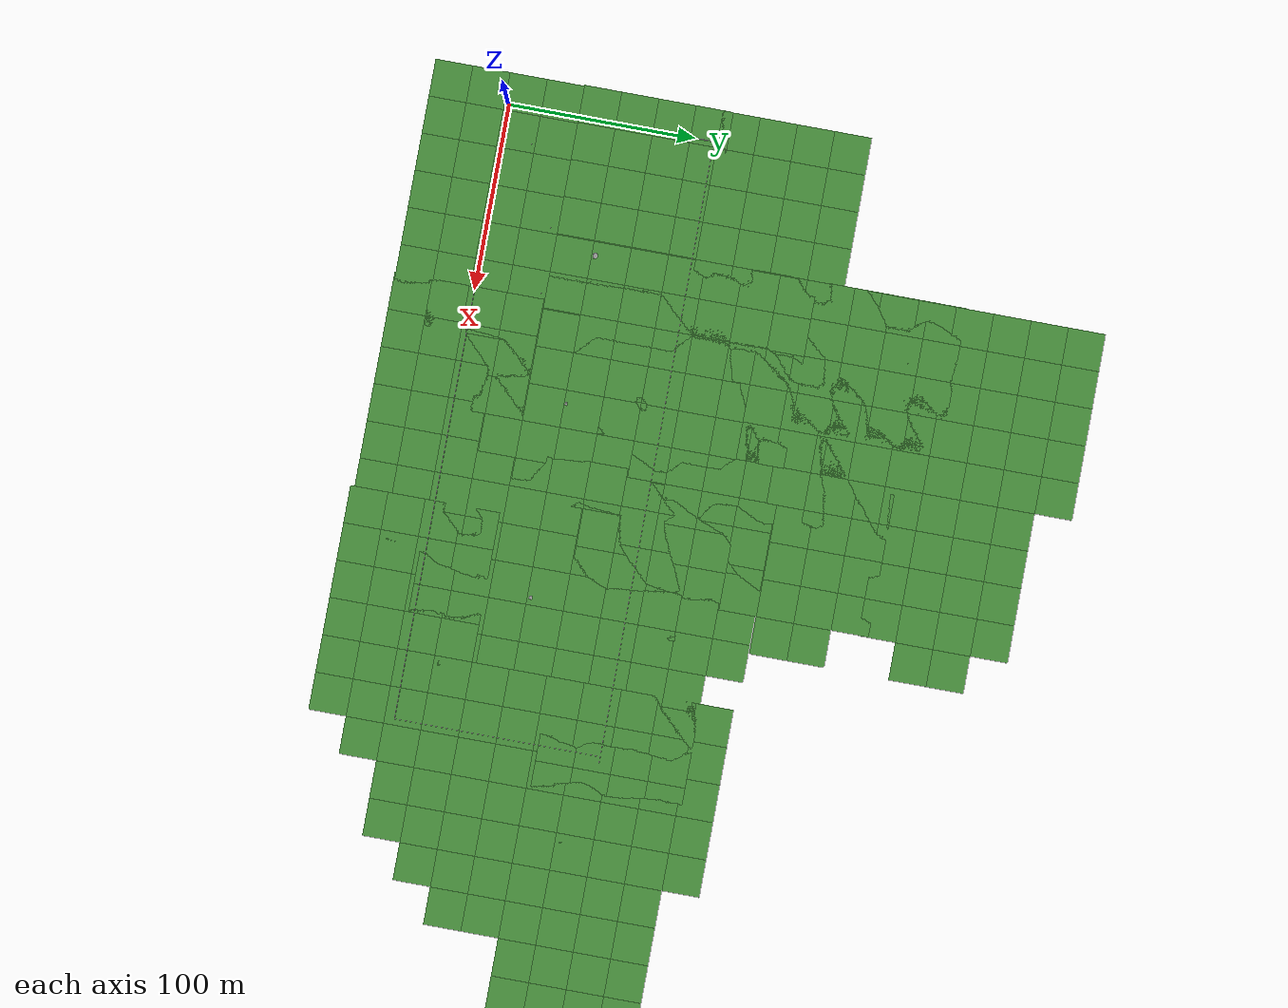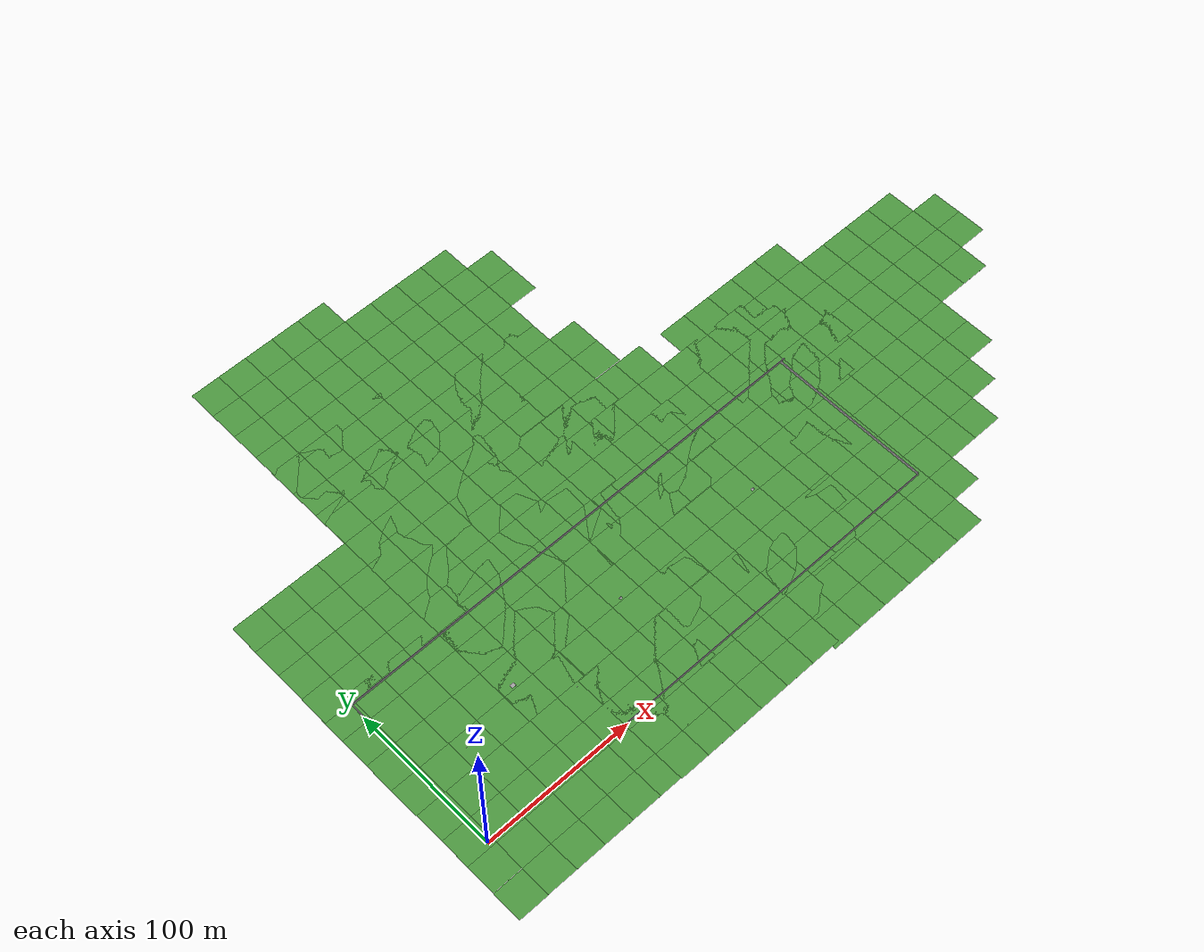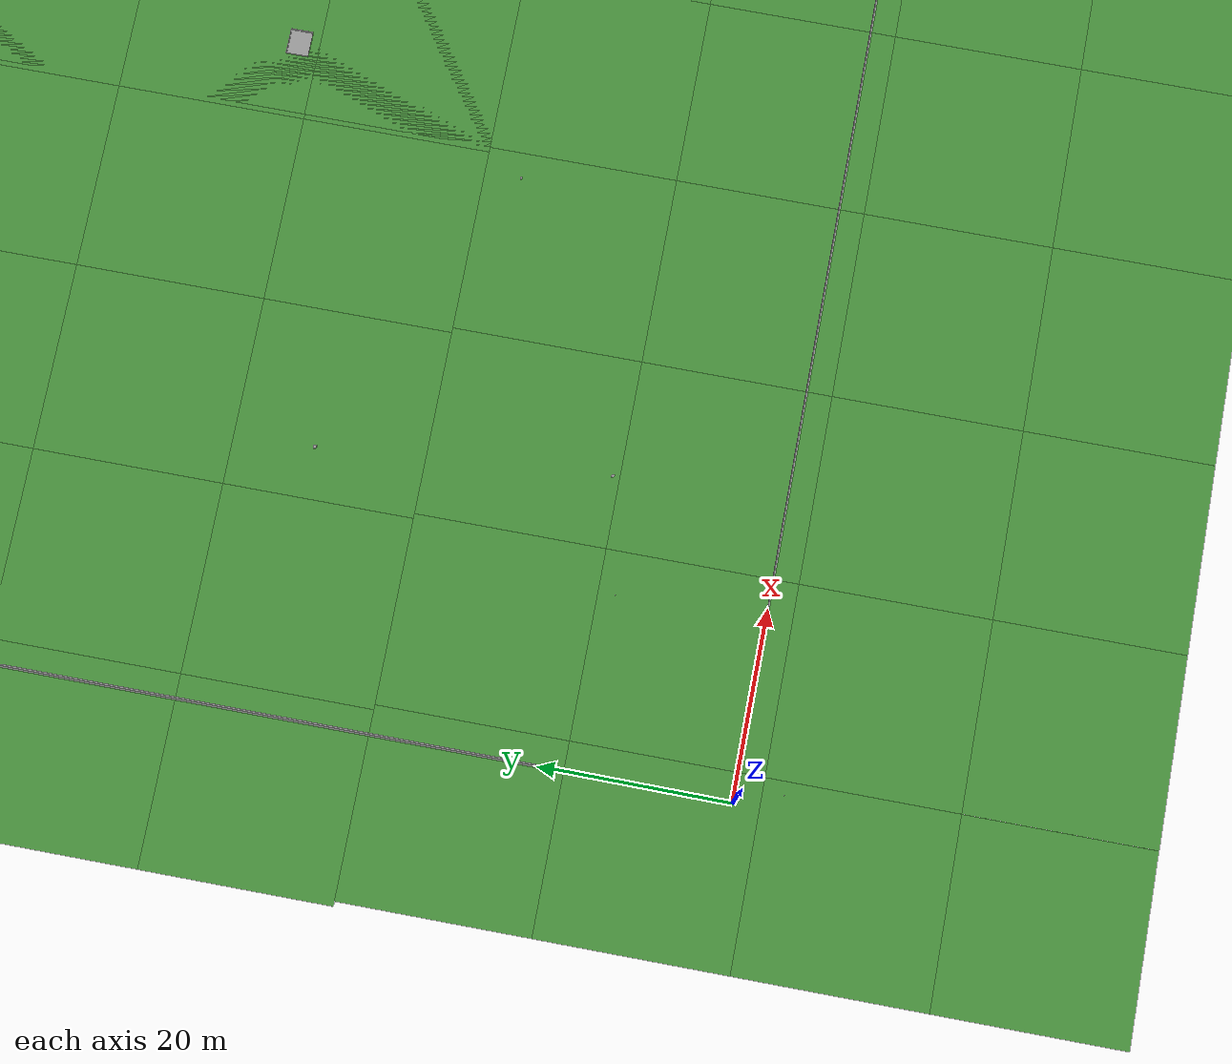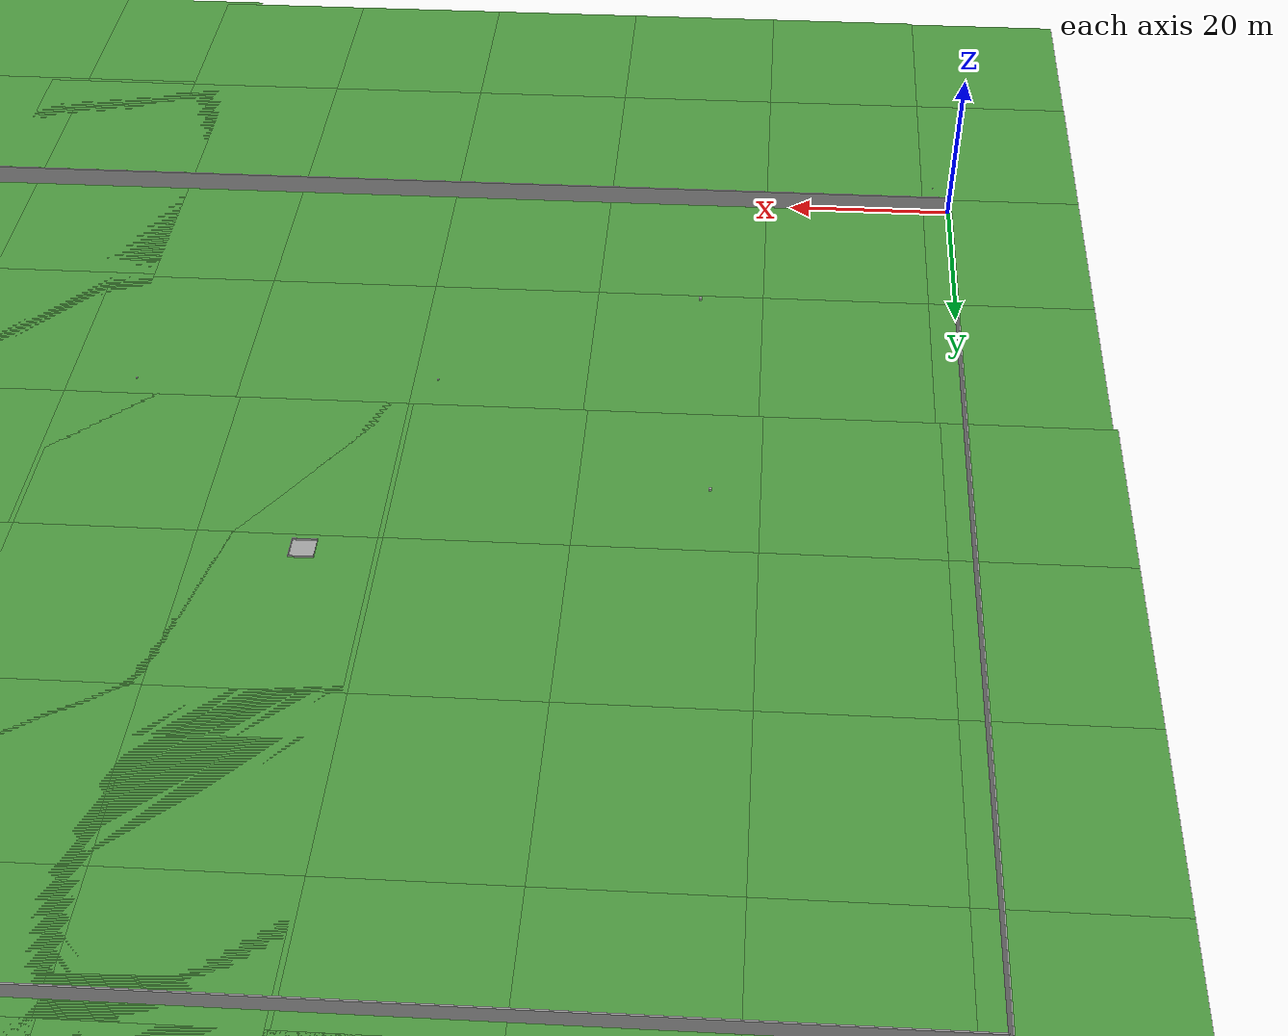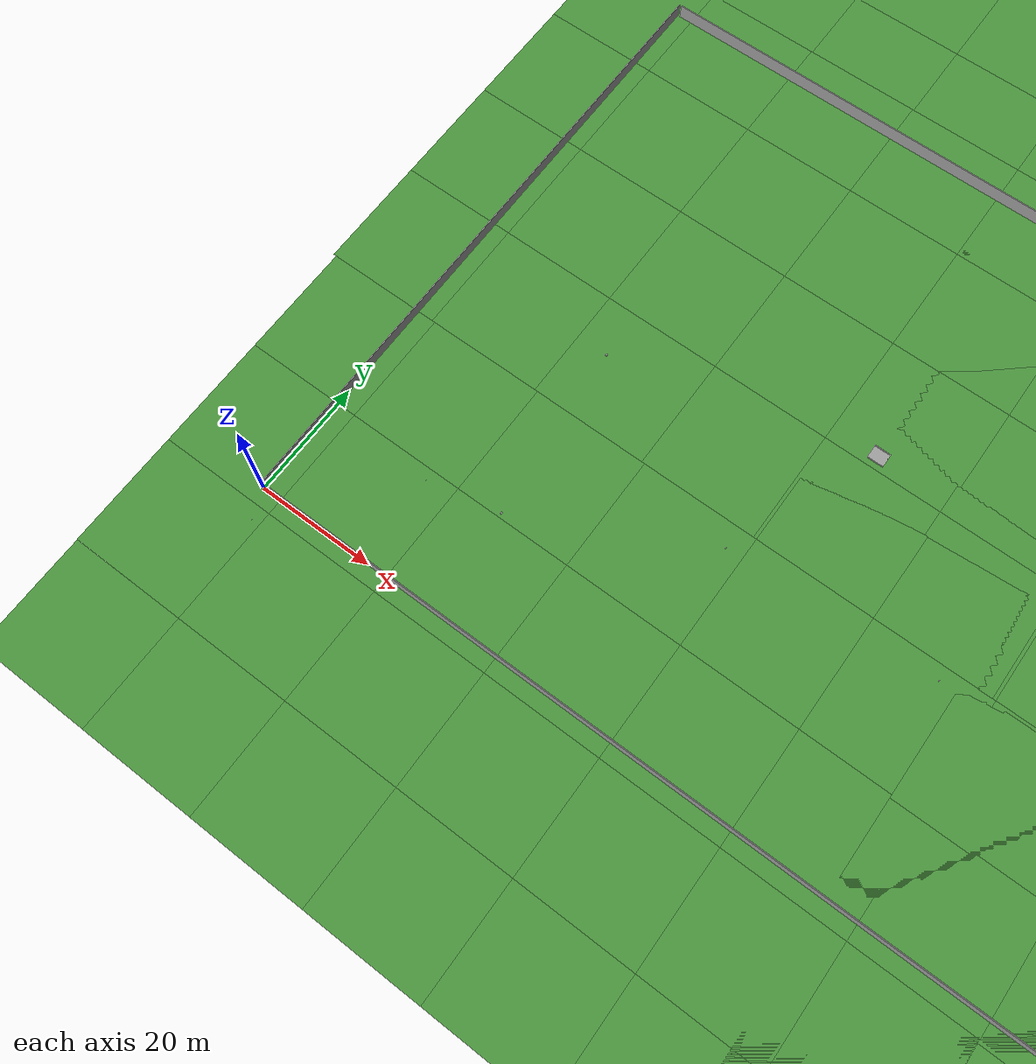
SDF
<sdf version="1.6">
 <world name="default">
  <light name="sun" type="directional">
   <pose>0 0 10 0 -0 0</pose>
   <diffuse>0.8 0.8 0.8 1</diffuse>
   <specular>0.1 0.1 0.1 1</specular>
   <attenuation>
    <range>1000</range>
    <constant>0.9</constant>
    <linear>0.01</linear>
    <quadratic>0.001</quadratic>
   </attenuation>
   <direction>-0.5 0.5 -1</direction>
  </light>
  <plugin name="ros_interface_plugin" filename="librotors_gazebo_ros_interface_plugin.so"/>
  <spherical_coordinates>
   <surface_model>EARTH_WGS84</surface_model>
   <latitude_deg>47.3667</latitude_deg>
   <longitude_deg>8.55</longitude_deg>
   <elevation>500</elevation>
   <heading_deg>0</heading_deg>
  </spherical_coordinates>
  <physics name="default_physics" default="0" type="ode">
   <ode>
    <solver>
     <type>quick</type>
     <iters>1000</iters>
     <sor>1.3</sor>
     <use_dynamic_moi_rescaling>0</use_dynamic_moi_rescaling>
    </solver>
    <constraints>
     <cfm>0</cfm>
     <erp>0.2</erp>
     <contact_max_correcting_vel>100</contact_max_correcting_vel>
     <contact_surface_layer>0.001</contact_surface_layer>
    </constraints>
   </ode>
   <max_step_size>0.01</max_step_size>
   <real_time_factor>1</real_time_factor>
   <real_time_update_rate>100</real_time_update_rate>
  </physics>
  <gravity>0 0 -9.8</gravity>
  <magnetic_field>6e-06 2.3e-05 -4.2e-05</magnetic_field>
  <atmosphere type="adiabatic"/>
  <scene><ambient>0.4 0.4 0.4 1</ambient><background>0.7 0.7 0.7 1</background><shadows>1</shadows></scene>
  <model name="Red_Mailbox">
   <link name="link">
    <inertial>
     <mass>40</mass>
     <inertia><ixx>0.5</ixx><ixy>0</ixy><ixz>0</ixz><iyy>0.5</iyy><iyz>0</iyz><izz>1</izz></inertia>
    </inertial>
    <visual name="ModelPreview_1::link::visual_1">
     <geometry><mesh><uri>model://Red_Mailbox/meshes/red.dae</uri><scale>1 1 1</scale></mesh></geometry>
     <material><shader type="pixel"/></material>
    </visual>
    <visual name="visual">
     <geometry><mesh><uri>model://Red_Mailbox/meshes/red.dae</uri><scale>1 1 1</scale></mesh></geometry>
     <material>
      <emissive>1 0 0 0</emissive>
      <shader type="vertex"><normal_map>__default__</normal_map></shader>
     </material>
    </visual>
    <collision name="collision">
     <geometry><box><size>0.75 0.65 0.3</size></box></geometry>
     <surface>
      <friction>
       <ode><mu>1</mu><mu2>1</mu2><fdir1>0 0 0</fdir1><slip1>0</slip1><slip2>0</slip2></ode>
       <torsional>
        <coefficient>1</coefficient>
        <patch_radius>0</patch_radius>
        <surface_radius>0</surface_radius>
        <use_patch_radius>1</use_patch_radius>
        <ode><slip>0</slip></ode>
       </torsional>
      </friction>
      <bounce><restitution_coefficient>0</restitution_coefficient><threshold>1e+06</threshold></bounce>
      <contact>
       <collide_without_contact>0</collide_without_contact>
       <collide_without_contact_bitmask>1</collide_without_contact_bitmask>
       <collide_bitmask>1</collide_bitmask>
       <ode>
        <soft_cfm>0</soft_cfm>
        <soft_erp>0.2</soft_erp>
        <kp>1e+13</kp>
        <kd>1</kd>
        <max_vel>0.1</max_vel>
        <min_depth>0.001</min_depth>
       </ode>
       <bullet>
        <split_impulse>1</split_impulse>
        <split_impulse_penetration_threshold>-0.01</split_impulse_penetration_threshold>
        <soft_cfm>0</soft_cfm>
        <soft_erp>0.2</soft_erp>
        <kp>1e+13</kp>
        <kd>1</kd>
       </bullet>
      </contact>
     </surface>
    </collision>
   </link>
   <static>0</static>
   <pose>150.514 58.5873 0.14902 0 -0 0</pose>
  </model>
  <model name="Blue_Mailbox">
   <link name="link">
    <inertial>
     <mass>40</mass>
     <inertia><ixx>0.5</ixx><ixy>0</ixy><ixz>0</ixz><iyy>0.5</iyy><iyz>0</iyz><izz>1</izz></inertia>
    </inertial>
    <visual name="ModelPreview_4::link::visual_1">
     <geometry><mesh><uri>model://Blue_Mailbox/meshes/blue.dae</uri><scale>1 1 1</scale></mesh></geometry>
     <material><shader type="pixel"/></material>
    </visual>
    <visual name="visual">
     <geometry><mesh><uri>model://Blue_Mailbox/meshes/blue.dae</uri><scale>1 1 1</scale></mesh></geometry>
     <material>
      <emissive>0 0 1 0</emissive>
      <shader type="vertex"><normal_map>__default__</normal_map></shader>
     </material>
    </visual>
    <collision name="collision">
     <geometry><box><size>1.2 1.2 0.3</size></box></geometry>
     <surface>
      <friction>
       <ode><mu>1</mu><mu2>1</mu2><fdir1>0 0 0</fdir1><slip1>0</slip1><slip2>0</slip2></ode>
       <torsional>
        <coefficient>1</coefficient>
        <patch_radius>0</patch_radius>
        <surface_radius>0</surface_radius>
        <use_patch_radius>1</use_patch_radius>
        <ode><slip>0</slip></ode>
       </torsional>
      </friction>
      <bounce><restitution_coefficient>0</restitution_coefficient><threshold>1e+06</threshold></bounce>
      <contact>
       <collide_without_contact>0</collide_without_contact>
       <collide_without_contact_bitmask>1</collide_without_contact_bitmask>
       <collide_bitmask>1</collide_bitmask>
       <ode>
        <soft_cfm>0</soft_cfm>
        <soft_erp>0.2</soft_erp>
        <kp>1e+13</kp>
        <kd>1</kd>
        <max_vel>0.1</max_vel>
        <min_depth>0.001</min_depth>
       </ode>
       <bullet>
        <split_impulse>1</split_impulse>
        <split_impulse_penetration_threshold>-0.01</split_impulse_penetration_threshold>
        <soft_cfm>0</soft_cfm>
        <soft_erp>0.2</soft_erp>
        <kp>1e+13</kp>
        <kd>1</kd>
       </bullet>
      </contact>
     </surface>
    </collision>
   </link>
   <static>0</static>
   <pose>254.352 58.6791 0.14902 0 -0 0</pose>
  </model>
  <model name="Yellow_Mailbox">
   <link name="link">
    <inertial>
     <mass>0.3</mass>
     <inertia><ixx>0.5</ixx><ixy>0</ixy><ixz>0</ixz><iyy>0.5</iyy><iyz>0</iyz><izz>1</izz></inertia>
    </inertial>
    <visual name="visual">
     <geometry><mesh><uri>model://Yellow_Mailbox/meshes/yellow.dae</uri><scale>1 1 1</scale></mesh></geometry>
     <material>
      <shader type="normal_map_tangent_space"><normal_map>__default__</normal_map></shader>
      <emissive>1 1 0 0</emissive>
     </material>
    </visual>
    <collision name="collision">
     <geometry><box><size>1.5 1.5 0.3</size></box></geometry>
     <surface>
      <friction>
       <ode><mu>1</mu><mu2>1</mu2><fdir1>0 0 0</fdir1><slip1>0</slip1><slip2>0</slip2></ode>
       <torsional>
        <coefficient>1</coefficient>
        <patch_radius>0</patch_radius>
        <surface_radius>0</surface_radius>
        <use_patch_radius>1</use_patch_radius>
        <ode><slip>0</slip></ode>
       </torsional>
      </friction>
      <bounce><restitution_coefficient>0</restitution_coefficient><threshold>1e+06</threshold></bounce>
      <contact>
       <collide_without_contact>0</collide_without_contact>
       <collide_without_contact_bitmask>1</collide_without_contact_bitmask>
       <collide_bitmask>1</collide_bitmask>
       <ode>
        <soft_cfm>0</soft_cfm>
        <soft_erp>0.2</soft_erp>
        <kp>1e+13</kp>
        <kd>1</kd>
        <max_vel>0.1</max_vel>
        <min_depth>0.001</min_depth>
       </ode>
       <bullet>
        <split_impulse>1</split_impulse>
        <split_impulse_penetration_threshold>-0.01</split_impulse_penetration_threshold>
        <soft_cfm>0</soft_cfm>
        <soft_erp>0.2</soft_erp>
        <kp>1e+13</kp>
        <kd>1</kd>
       </bullet>
      </contact>
     </surface>
    </collision>
   </link>
   <static>0</static>
   <pose>70.7731 59.4055 0.14902 0 -0 0</pose>
  </model>
  <model name="Blue_Package">
   <link name="link">
    <inertial>
     <mass>0.2</mass>
     <inertia><ixx>1</ixx><ixy>0</ixy><ixz>0</ixz><iyy>1</iyy><iyz>0</iyz><izz>1</izz></inertia>
    </inertial>
    <visual name="visual">
     <geometry><mesh><uri>model://Blue_Package/meshes/bluebox.dae</uri><scale>1 1 1</scale></mesh></geometry>
     <material>
      <emissive>0 0 1 0</emissive>
      <shader type="vertex"><normal_map>__default__</normal_map></shader>
     </material>
    </visual>
    <collision name="collision">
     <geometry><box><size>0.2 0.2 0.2</size></box></geometry>
     <surface>
      <friction>
       <ode><mu>1</mu><mu2>1</mu2><fdir1>0 0 0</fdir1><slip1>0</slip1><slip2>0</slip2></ode>
       <torsional>
        <coefficient>1</coefficient>
        <patch_radius>0</patch_radius>
        <surface_radius>0</surface_radius>
        <use_patch_radius>1</use_patch_radius>
        <ode><slip>0</slip></ode>
       </torsional>
      </friction>
      <bounce><restitution_coefficient>0</restitution_coefficient><threshold>1e+06</threshold></bounce>
      <contact>
       <collide_without_contact>0</collide_without_contact>
       <collide_without_contact_bitmask>1</collide_without_contact_bitmask>
       <collide_bitmask>1</collide_bitmask>
       <ode>
        <soft_cfm>0</soft_cfm>
        <soft_erp>0.2</soft_erp>
        <kp>1e+13</kp>
        <kd>1</kd>
        <max_vel>0.1</max_vel>
        <min_depth>0.001</min_depth>
       </ode>
       <bullet>
        <split_impulse>1</split_impulse>
        <split_impulse_penetration_threshold>-0.01</split_impulse_penetration_threshold>
        <soft_cfm>0</soft_cfm>
        <soft_erp>0.2</soft_erp>
        <kp>1e+13</kp>
        <kd>1</kd>
       </bullet>
      </contact>
     </surface>
    </collision>
   </link>
   <static>0</static>
   <pose>95.326 34.9379 0.09902 0 -0 0</pose>
  </model>
  <model name="Red_Package_0">
   <link name="link">
    <inertial>
     <mass>0.2</mass>
     <inertia><ixx>1</ixx><ixy>0</ixy><ixz>0</ixz><iyy>1</iyy><iyz>0</iyz><izz>1</izz></inertia>
    </inertial>
    <visual name="ModelPreview_10::link::visual_1">
     <geometry><mesh><uri>model://Red_Package/meshes/redbox.dae</uri><scale>1 1 1</scale></mesh></geometry>
     <material><shader type="vertex"><normal_map>__default__</normal_map></shader></material>
    </visual>
    <visual name="visual">
     <geometry><mesh><uri>model://Red_Package/meshes/redbox.dae</uri><scale>1 1 1</scale></mesh></geometry>
     <material>
      <shader type="vertex"><normal_map>__default__</normal_map></shader>
      <emissive>1 0 0 0</emissive>
     </material>
    </visual>
    <collision name="collision">
     <geometry><box><size>0.1 0.1 0.1</size></box></geometry>
     <surface>
      <friction>
       <ode><mu>1</mu><mu2>1</mu2><fdir1>0 0 0</fdir1><slip1>0</slip1><slip2>0</slip2></ode>
       <torsional>
        <coefficient>1</coefficient>
        <patch_radius>0</patch_radius>
        <surface_radius>0</surface_radius>
        <use_patch_radius>1</use_patch_radius>
        <ode><slip>0</slip></ode>
       </torsional>
      </friction>
      <bounce><restitution_coefficient>0</restitution_coefficient><threshold>1e+06</threshold></bounce>
      <contact>
       <collide_without_contact>0</collide_without_contact>
       <collide_without_contact_bitmask>1</collide_without_contact_bitmask>
       <collide_bitmask>1</collide_bitmask>
       <ode>
        <soft_cfm>0</soft_cfm>
        <soft_erp>0.2</soft_erp>
        <kp>1e+13</kp>
        <kd>1</kd>
        <max_vel>0.1</max_vel>
        <min_depth>0.001</min_depth>
       </ode>
       <bullet>
        <split_impulse>1</split_impulse>
        <split_impulse_penetration_threshold>-0.01</split_impulse_penetration_threshold>
        <soft_cfm>0</soft_cfm>
        <soft_erp>0.2</soft_erp>
        <kp>1e+13</kp>
        <kd>1</kd>
       </bullet>
      </contact>
     </surface>
    </collision>
   </link>
   <static>0</static>
   <pose>18.5809 15.5011 0.049053 0 1e-06 0</pose>
  </model>
  <model name="Yellow_Package">
   <link name="link">
    <inertial>
     <mass>0.4</mass>
     <inertia><ixx>1</ixx><ixy>0</ixy><ixz>0</ixz><iyy>1</iyy><iyz>0</iyz><izz>1</izz></inertia>
    </inertial>
    <visual name="ModelPreview_1::link::visual_1">
     <geometry><mesh><uri>model://Yellow_Package/meshes/yellowbox.dae</uri><scale>1 1 1</scale></mesh></geometry>
     <material>
      <emissive>1 1 0 0</emissive>
      <shader type="vertex"><normal_map>__default__</normal_map></shader>
     </material>
    </visual>
    <visual name="visual">
     <geometry><mesh><uri>model://Yellow_Package/meshes/yellowbox.dae</uri><scale>1 1 1</scale></mesh></geometry>
     <material>
      <emissive>1 1 0 0</emissive>
      <shader type="vertex"><normal_map>__default__</normal_map></shader>
     </material>
    </visual>
    <visual name="ModelPreview_1::link::visual_2">
     <geometry><mesh><uri>model://Yellow_Package/meshes/yellowbox.dae</uri><scale>1 1 1</scale></mesh></geometry>
     <material>
      <emissive>1 1 0 0</emissive>
      <shader type="vertex"><normal_map>__default__</normal_map></shader>
     </material>
    </visual>
    <collision name="collision">
     <geometry><box><size>0.3 0.3 0.3</size></box></geometry>
     <surface>
      <friction>
       <ode><mu>1</mu><mu2>1</mu2><fdir1>0 0 0</fdir1><slip1>0</slip1><slip2>0</slip2></ode>
       <torsional>
        <coefficient>1</coefficient>
        <patch_radius>0</patch_radius>
        <surface_radius>0</surface_radius>
        <use_patch_radius>1</use_patch_radius>
        <ode><slip>0</slip></ode>
       </torsional>
      </friction>
      <bounce><restitution_coefficient>0</restitution_coefficient><threshold>1e+06</threshold></bounce>
      <contact>
       <collide_without_contact>0</collide_without_contact>
       <collide_without_contact_bitmask>1</collide_without_contact_bitmask>
       <collide_bitmask>1</collide_bitmask>
       <ode>
        <soft_cfm>0</soft_cfm>
        <soft_erp>0.2</soft_erp>
        <kp>1e+13</kp>
        <kd>1</kd>
        <max_vel>0.1</max_vel>
        <min_depth>0.001</min_depth>
       </ode>
       <bullet>
        <split_impulse>1</split_impulse>
        <split_impulse_penetration_threshold>-0.01</split_impulse_penetration_threshold>
        <soft_cfm>0</soft_cfm>
        <soft_erp>0.2</soft_erp>
        <kp>1e+13</kp>
        <kd>1</kd>
       </bullet>
      </contact>
     </surface>
    </collision>
   </link>
   <static>0</static>
   <pose>30.7391 18.0334 0.14902 0 -0 0</pose>
  </model>
  <model name="Blue_Package_0">
   <link name="link">
    <inertial>
     <mass>0.2</mass>
     <inertia><ixx>1</ixx><ixy>0</ixy><ixz>0</ixz><iyy>1</iyy><iyz>0</iyz><izz>1</izz></inertia>
    </inertial>
    <visual name="visual">
     <geometry><mesh><uri>model://Blue_Package/meshes/bluebox.dae</uri><scale>1 1 1</scale></mesh></geometry>
     <material>
      <emissive>0 0 1 0</emissive>
      <shader type="vertex"><normal_map>__default__</normal_map></shader>
     </material>
    </visual>
    <collision name="collision">
     <geometry><box><size>0.2 0.2 0.2</size></box></geometry>
     <surface>
      <friction>
       <ode><mu>1</mu><mu2>1</mu2><fdir1>0 0 0</fdir1><slip1>0</slip1><slip2>0</slip2></ode>
       <torsional>
        <coefficient>1</coefficient>
        <patch_radius>0</patch_radius>
        <surface_radius>0</surface_radius>
        <use_patch_radius>1</use_patch_radius>
        <ode><slip>0</slip></ode>
       </torsional>
      </friction>
      <bounce><restitution_coefficient>0</restitution_coefficient><threshold>1e+06</threshold></bounce>
      <contact>
       <collide_without_contact>0</collide_without_contact>
       <collide_without_contact_bitmask>1</collide_without_contact_bitmask>
       <collide_bitmask>1</collide_bitmask>
       <ode>
        <soft_cfm>0</soft_cfm>
        <soft_erp>0.2</soft_erp>
        <kp>1e+13</kp>
        <kd>1</kd>
        <max_vel>0.1</max_vel>
        <min_depth>0.001</min_depth>
       </ode>
       <bullet>
        <split_impulse>1</split_impulse>
        <split_impulse_penetration_threshold>-0.01</split_impulse_penetration_threshold>
        <soft_cfm>0</soft_cfm>
        <soft_erp>0.2</soft_erp>
        <kp>1e+13</kp>
        <kd>1</kd>
       </bullet>
      </contact>
     </surface>
    </collision>
   </link>
   <static>0</static>
   <pose>60.3937 33.4348 0.09902 0 -0 0</pose>
  </model>
  <model name="Red_Package_1">
   <link name="link">
    <inertial>
     <mass>0.2</mass>
     <inertia><ixx>1</ixx><ixy>0</ixy><ixz>0</ixz><iyy>1</iyy><iyz>0</iyz><izz>1</izz></inertia>
    </inertial>
    <visual name="ModelPreview_10::link::visual_1">
     <geometry><mesh><uri>model://Red_Package/meshes/redbox.dae</uri><scale>1 1 1</scale></mesh></geometry>
     <material><shader type="vertex"><normal_map>__default__</normal_map></shader></material>
    </visual>
    <visual name="visual">
     <geometry><mesh><uri>model://Red_Package/meshes/redbox.dae</uri><scale>1 1 1</scale></mesh></geometry>
     <material>
      <shader type="vertex"><normal_map>__default__</normal_map></shader>
      <emissive>1 0 0 0</emissive>
     </material>
    </visual>
    <collision name="collision">
     <geometry><box><size>0.1 0.1 0.1</size></box></geometry>
     <surface>
      <friction>
       <ode><mu>1</mu><mu2>1</mu2><fdir1>0 0 0</fdir1><slip1>0</slip1><slip2>0</slip2></ode>
       <torsional>
        <coefficient>1</coefficient>
        <patch_radius>0</patch_radius>
        <surface_radius>0</surface_radius>
        <use_patch_radius>1</use_patch_radius>
        <ode><slip>0</slip></ode>
       </torsional>
      </friction>
      <bounce><restitution_coefficient>0</restitution_coefficient><threshold>1e+06</threshold></bounce>
      <contact>
       <collide_without_contact>0</collide_without_contact>
       <collide_without_contact_bitmask>1</collide_without_contact_bitmask>
       <collide_bitmask>1</collide_bitmask>
       <ode>
        <soft_cfm>0</soft_cfm>
        <soft_erp>0.2</soft_erp>
        <kp>1e+13</kp>
        <kd>1</kd>
        <max_vel>0.1</max_vel>
        <min_depth>0.001</min_depth>
       </ode>
       <bullet>
        <split_impulse>1</split_impulse>
        <split_impulse_penetration_threshold>-0.01</split_impulse_penetration_threshold>
        <soft_cfm>0</soft_cfm>
        <soft_erp>0.2</soft_erp>
        <kp>1e+13</kp>
        <kd>1</kd>
       </bullet>
      </contact>
     </surface>
    </collision>
   </link>
   <static>0</static>
   <pose>1.74151 -4.86803 0.049042 0 1e-06 0</pose>
  </model>
  <model name="Yellow_Package_0">
   <link name="link">
    <inertial>
     <mass>0.4</mass>
     <inertia><ixx>1</ixx><ixy>0</ixy><ixz>0</ixz><iyy>1</iyy><iyz>0</iyz><izz>1</izz></inertia>
    </inertial>
    <visual name="ModelPreview_1::link::visual_1">
     <geometry><mesh><uri>model://Yellow_Package/meshes/yellowbox.dae</uri><scale>1 1 1</scale></mesh></geometry>
     <material>
      <emissive>1 1 0 0</emissive>
      <shader type="vertex"><normal_map>__default__</normal_map></shader>
     </material>
    </visual>
    <visual name="visual">
     <geometry><mesh><uri>model://Yellow_Package/meshes/yellowbox.dae</uri><scale>1 1 1</scale></mesh></geometry>
     <material>
      <emissive>1 1 0 0</emissive>
      <shader type="vertex"><normal_map>__default__</normal_map></shader>
     </material>
    </visual>
    <visual name="ModelPreview_1::link::visual_2">
     <geometry><mesh><uri>model://Yellow_Package/meshes/yellowbox.dae</uri><scale>1 1 1</scale></mesh></geometry>
     <material>
      <emissive>1 1 0 0</emissive>
      <shader type="vertex"><normal_map>__default__</normal_map></shader>
     </material>
    </visual>
    <collision name="collision">
     <geometry><box><size>0.3 0.3 0.3</size></box></geometry>
     <surface>
      <friction>
       <ode><mu>1</mu><mu2>1</mu2><fdir1>0 0 0</fdir1><slip1>0</slip1><slip2>0</slip2></ode>
       <torsional>
        <coefficient>1</coefficient>
        <patch_radius>0</patch_radius>
        <surface_radius>0</surface_radius>
        <use_patch_radius>1</use_patch_radius>
        <ode><slip>0</slip></ode>
       </torsional>
      </friction>
      <bounce><restitution_coefficient>0</restitution_coefficient><threshold>1e+06</threshold></bounce>
      <contact>
       <collide_without_contact>0</collide_without_contact>
       <collide_without_contact_bitmask>1</collide_without_contact_bitmask>
       <collide_bitmask>1</collide_bitmask>
       <ode>
        <soft_cfm>0</soft_cfm>
        <soft_erp>0.2</soft_erp>
        <kp>1e+13</kp>
        <kd>1</kd>
        <max_vel>0.1</max_vel>
        <min_depth>0.001</min_depth>
       </ode>
       <bullet>
        <split_impulse>1</split_impulse>
        <split_impulse_penetration_threshold>-0.01</split_impulse_penetration_threshold>
        <soft_cfm>0</soft_cfm>
        <soft_erp>0.2</soft_erp>
        <kp>1e+13</kp>
        <kd>1</kd>
       </bullet>
      </contact>
     </surface>
    </collision>
   </link>
   <static>0</static>
   <pose>28.121 48.7359 0.14902 0 -0 0</pose>
  </model>
  <model name="grass_plane_5">
   <static>1</static>
   <link name="link">
    <collision name="collision">
     <geometry><plane><normal>0 0 1</normal><size>500 500</size></plane></geometry>
     <surface><friction><ode><mu>0.5</mu><mu2>0.5</mu2></ode></friction></surface>
    </collision>
    <visual name="visual_0">
     <pose>-40 -40 0 0 -0 0</pose>
     <cast_shadows>0</cast_shadows>
     <geometry><plane><normal>0 0 1</normal><size>20 20</size></plane></geometry>
     <material>
      <script>
       <uri>model://grass_plane/materials/scripts</uri>
       <uri>model://grass_plane/materials/textures</uri>
       <name>vrc/grass</name>
      </script>
     </material>
    </visual>
    <visual name="visual_1">
     <pose>-20 -40 0 0 -0 0</pose>
     <cast_shadows>0</cast_shadows>
     <geometry><plane><normal>0 0 1</normal><size>20 20</size></plane></geometry>
     <material>
      <script>
       <uri>model://grass_plane/materials/scripts</uri>
       <uri>model://grass_plane/materials/textures</uri>
       <name>vrc/grass</name>
      </script>
     </material>
    </visual>
    <visual name="visual_2">
     <pose>0 -40 0 0 -0 0</pose>
     <cast_shadows>0</cast_shadows>
     <geometry><plane><normal>0 0 1</normal><size>20 20</size></plane></geometry>
     <material>
      <script>
       <uri>model://grass_plane/materials/scripts</uri>
       <uri>model://grass_plane/materials/textures</uri>
       <name>vrc/grass</name>
      </script>
     </material>
    </visual>
    <visual name="visual_3">
     <pose>20 -40 0 0 -0 0</pose>
     <cast_shadows>0</cast_shadows>
     <geometry><plane><normal>0 0 1</normal><size>20 20</size></plane></geometry>
     <material>
      <script>
       <uri>model://grass_plane/materials/scripts</uri>
       <uri>model://grass_plane/materials/textures</uri>
       <name>vrc/grass</name>
      </script>
     </material>
    </visual>
    <visual name="visual_4">
     <pose>40 -40 0 0 -0 0</pose>
     <cast_shadows>0</cast_shadows>
     <geometry><plane><normal>0 0 1</normal><size>20 20</size></plane></geometry>
     <material>
      <script>
       <uri>model://grass_plane/materials/scripts</uri>
       <uri>model://grass_plane/materials/textures</uri>
       <name>vrc/grass</name>
      </script>
     </material>
    </visual>
    <visual name="visual_5">
     <pose>60 -40 0 0 -0 0</pose>
     <cast_shadows>0</cast_shadows>
     <geometry><plane><normal>0 0 1</normal><size>20 20</size></plane></geometry>
     <material>
      <script>
       <uri>model://grass_plane/materials/scripts</uri>
       <uri>model://grass_plane/materials/textures</uri>
       <name>vrc/grass</name>
      </script>
     </material>
    </visual>
    <visual name="visual_6">
     <pose>-40 -20 0 0 -0 0</pose>
     <cast_shadows>0</cast_shadows>
     <geometry><plane><normal>0 0 1</normal><size>20 20</size></plane></geometry>
     <material>
      <script>
       <uri>model://grass_plane/materials/scripts</uri>
       <uri>model://grass_plane/materials/textures</uri>
       <name>vrc/grass</name>
      </script>
     </material>
    </visual>
    <visual name="visual_7">
     <pose>-20 -20 0 0 -0 0</pose>
     <cast_shadows>0</cast_shadows>
     <geometry><plane><normal>0 0 1</normal><size>20 20</size></plane></geometry>
     <material>
      <script>
       <uri>model://grass_plane/materials/scripts</uri>
       <uri>model://grass_plane/materials/textures</uri>
       <name>vrc/grass</name>
      </script>
     </material>
    </visual>
    <visual name="visual_8">
     <pose>0 -20 0 0 -0 0</pose>
     <cast_shadows>0</cast_shadows>
     <geometry><plane><normal>0 0 1</normal><size>20 20</size></plane></geometry>
     <material>
      <script>
       <uri>model://grass_plane/materials/scripts</uri>
       <uri>model://grass_plane/materials/textures</uri>
       <name>vrc/grass</name>
      </script>
     </material>
    </visual>
    <visual name="visual_9">
     <pose>20 -20 0 0 -0 0</pose>
     <cast_shadows>0</cast_shadows>
     <geometry><plane><normal>0 0 1</normal><size>20 20</size></plane></geometry>
     <material>
      <script>
       <uri>model://grass_plane/materials/scripts</uri>
       <uri>model://grass_plane/materials/textures</uri>
       <name>vrc/grass</name>
      </script>
     </material>
    </visual>
    <visual name="visual_10">
     <pose>40 -20 0 0 -0 0</pose>
     <cast_shadows>0</cast_shadows>
     <geometry><plane><normal>0 0 1</normal><size>20 20</size></plane></geometry>
     <material>
      <script>
       <uri>model://grass_plane/materials/scripts</uri>
       <uri>model://grass_plane/materials/textures</uri>
       <name>vrc/grass</name>
      </script>
     </material>
    </visual>
    <visual name="visual_11">
     <pose>60 -20 0 0 -0 0</pose>
     <cast_shadows>0</cast_shadows>
     <geometry><plane><normal>0 0 1</normal><size>20 20</size></plane></geometry>
     <material>
      <script>
       <uri>model://grass_plane/materials/scripts</uri>
       <uri>model://grass_plane/materials/textures</uri>
       <name>vrc/grass</name>
      </script>
     </material>
    </visual>
    <visual name="visual_12">
     <pose>80 -20 0 0 -0 0</pose>
     <cast_shadows>0</cast_shadows>
     <geometry><plane><normal>0 0 1</normal><size>20 20</size></plane></geometry>
     <material>
      <script>
       <uri>model://grass_plane/materials/scripts</uri>
       <uri>model://grass_plane/materials/textures</uri>
       <name>vrc/grass</name>
      </script>
     </material>
    </visual>
    <visual name="visual_13">
     <pose>-40 0 0 0 -0 0</pose>
     <cast_shadows>0</cast_shadows>
     <geometry><plane><normal>0 0 1</normal><size>20 20</size></plane></geometry>
     <material>
      <script>
       <uri>model://grass_plane/materials/scripts</uri>
       <uri>model://grass_plane/materials/textures</uri>
       <name>vrc/grass</name>
      </script>
     </material>
    </visual>
    <visual name="visual_14">
     <pose>-20 0 0 0 -0 0</pose>
     <cast_shadows>0</cast_shadows>
     <geometry><plane><normal>0 0 1</normal><size>20 20</size></plane></geometry>
     <material>
      <script>
       <uri>model://grass_plane/materials/scripts</uri>
       <uri>model://grass_plane/materials/textures</uri>
       <name>vrc/grass</name>
      </script>
     </material>
    </visual>
    <visual name="visual_15">
     <cast_shadows>0</cast_shadows>
     <geometry><plane><normal>0 0 1</normal><size>20 20</size></plane></geometry>
     <material>
      <script>
       <uri>model://grass_plane/materials/scripts</uri>
       <uri>model://grass_plane/materials/textures</uri>
       <name>vrc/grass</name>
      </script>
     </material>
    </visual>
    <visual name="visual_16">
     <pose>20 0 0 0 -0 0</pose>
     <cast_shadows>0</cast_shadows>
     <geometry><plane><normal>0 0 1</normal><size>20 20</size></plane></geometry>
     <material>
      <script>
       <uri>model://grass_plane/materials/scripts</uri>
       <uri>model://grass_plane/materials/textures</uri>
       <name>vrc/grass</name>
      </script>
     </material>
    </visual>
    <visual name="visual_17">
     <pose>40 0 0 0 -0 0</pose>
     <cast_shadows>0</cast_shadows>
     <geometry><plane><normal>0 0 1</normal><size>20 20</size></plane></geometry>
     <material>
      <script>
       <uri>model://grass_plane/materials/scripts</uri>
       <uri>model://grass_plane/materials/textures</uri>
       <name>vrc/grass</name>
      </script>
     </material>
    </visual>
    <visual name="visual_18">
     <pose>60 0 0 0 -0 0</pose>
     <cast_shadows>0</cast_shadows>
     <geometry><plane><normal>0 0 1</normal><size>20 20</size></plane></geometry>
     <material>
      <script>
       <uri>model://grass_plane/materials/scripts</uri>
       <uri>model://grass_plane/materials/textures</uri>
       <name>vrc/grass</name>
      </script>
     </material>
    </visual>
    <visual name="visual_19">
     <pose>80 0 0 0 -0 0</pose>
     <cast_shadows>0</cast_shadows>
     <geometry><plane><normal>0 0 1</normal><size>20 20</size></plane></geometry>
     <material>
      <script>
       <uri>model://grass_plane/materials/scripts</uri>
       <uri>model://grass_plane/materials/textures</uri>
       <name>vrc/grass</name>
      </script>
     </material>
    </visual>
    <visual name="visual_20">
     <pose>100 0 0 0 -0 0</pose>
     <cast_shadows>0</cast_shadows>
     <geometry><plane><normal>0 0 1</normal><size>20 20</size></plane></geometry>
     <material>
      <script>
       <uri>model://grass_plane/materials/scripts</uri>
       <uri>model://grass_plane/materials/textures</uri>
       <name>vrc/grass</name>
      </script>
     </material>
    </visual>
    <visual name="visual_21">
     <pose>120 0 0 0 -0 0</pose>
     <cast_shadows>0</cast_shadows>
     <geometry><plane><normal>0 0 1</normal><size>20 20</size></plane></geometry>
     <material>
      <script>
       <uri>model://grass_plane/materials/scripts</uri>
       <uri>model://grass_plane/materials/textures</uri>
       <name>vrc/grass</name>
      </script>
     </material>
    </visual>
    <visual name="visual_22">
     <pose>-40 20 0 0 -0 0</pose>
     <cast_shadows>0</cast_shadows>
     <geometry><plane><normal>0 0 1</normal><size>20 20</size></plane></geometry>
     <material>
      <script>
       <uri>model://grass_plane/materials/scripts</uri>
       <uri>model://grass_plane/materials/textures</uri>
       <name>vrc/grass</name>
      </script>
     </material>
    </visual>
    <visual name="visual_23">
     <pose>-20 20 0 0 -0 0</pose>
     <cast_shadows>0</cast_shadows>
     <geometry><plane><normal>0 0 1</normal><size>20 20</size></plane></geometry>
     <material>
      <script>
       <uri>model://grass_plane/materials/scripts</uri>
       <uri>model://grass_plane/materials/textures</uri>
       <name>vrc/grass</name>
      </script>
     </material>
    </visual>
    <visual name="visual_24">
     <pose>0 20 0 0 -0 0</pose>
     <cast_shadows>0</cast_shadows>
     <geometry><plane><normal>0 0 1</normal><size>20 20</size></plane></geometry>
     <material>
      <script>
       <uri>model://grass_plane/materials/scripts</uri>
       <uri>model://grass_plane/materials/textures</uri>
       <name>vrc/grass</name>
      </script>
     </material>
    </visual>
    <visual name="visual_25">
     <pose>20 20 0 0 -0 0</pose>
     <cast_shadows>0</cast_shadows>
     <geometry><plane><normal>0 0 1</normal><size>20 20</size></plane></geometry>
     <material>
      <script>
       <uri>model://grass_plane/materials/scripts</uri>
       <uri>model://grass_plane/materials/textures</uri>
       <name>vrc/grass</name>
      </script>
     </material>
    </visual>
    <visual name="visual_26">
     <pose>40 20 0 0 -0 0</pose>
     <cast_shadows>0</cast_shadows>
     <geometry><plane><normal>0 0 1</normal><size>20 20</size></plane></geometry>
     <material>
      <script>
       <uri>model://grass_plane/materials/scripts</uri>
       <uri>model://grass_plane/materials/textures</uri>
       <name>vrc/grass</name>
      </script>
     </material>
    </visual>
    <visual name="visual_27">
     <pose>60 20 0 0 -0 0</pose>
     <cast_shadows>0</cast_shadows>
     <geometry><plane><normal>0 0 1</normal><size>20 20</size></plane></geometry>
     <material>
      <script>
       <uri>model://grass_plane/materials/scripts</uri>
       <uri>model://grass_plane/materials/textures</uri>
       <name>vrc/grass</name>
      </script>
     </material>
    </visual>
    <visual name="visual_28">
     <pose>80 20 0 0 -0 0</pose>
     <cast_shadows>0</cast_shadows>
     <geometry><plane><normal>0 0 1</normal><size>20 20</size></plane></geometry>
     <material>
      <script>
       <uri>model://grass_plane/materials/scripts</uri>
       <uri>model://grass_plane/materials/textures</uri>
       <name>vrc/grass</name>
      </script>
     </material>
    </visual>
    <visual name="visual_29">
     <pose>100 20 0 0 -0 0</pose>
     <cast_shadows>0</cast_shadows>
     <geometry><plane><normal>0 0 1</normal><size>20 20</size></plane></geometry>
     <material>
      <script>
       <uri>model://grass_plane/materials/scripts</uri>
       <uri>model://grass_plane/materials/textures</uri>
       <name>vrc/grass</name>
      </script>
     </material>
    </visual>
    <visual name="visual_30">
     <pose>120 20 0 0 -0 0</pose>
     <cast_shadows>0</cast_shadows>
     <geometry><plane><normal>0 0 1</normal><size>20 20</size></plane></geometry>
     <material>
      <script>
       <uri>model://grass_plane/materials/scripts</uri>
       <uri>model://grass_plane/materials/textures</uri>
       <name>vrc/grass</name>
      </script>
     </material>
    </visual>
    <visual name="visual_31">
     <pose>140 20 0 0 -0 0</pose>
     <cast_shadows>0</cast_shadows>
     <geometry><plane><normal>0 0 1</normal><size>20 20</size></plane></geometry>
     <material>
      <script>
       <uri>model://grass_plane/materials/scripts</uri>
       <uri>model://grass_plane/materials/textures</uri>
       <name>vrc/grass</name>
      </script>
     </material>
    </visual>
    <visual name="visual_32">
     <pose>40 40 0 0 -0 0</pose>
     <cast_shadows>0</cast_shadows>
     <geometry><plane><normal>0 0 1</normal><size>20 20</size></plane></geometry>
     <material>
      <script>
       <uri>model://grass_plane/materials/scripts</uri>
       <uri>model://grass_plane/materials/textures</uri>
       <name>vrc/grass</name>
      </script>
     </material>
    </visual>
    <visual name="visual_33">
     <pose>60 40 0 0 -0 0</pose>
     <cast_shadows>0</cast_shadows>
     <geometry><plane><normal>0 0 1</normal><size>20 20</size></plane></geometry>
     <material>
      <script>
       <uri>model://grass_plane/materials/scripts</uri>
       <uri>model://grass_plane/materials/textures</uri>
       <name>vrc/grass</name>
      </script>
     </material>
    </visual>
    <visual name="visual_34">
     <pose>80 40 0 0 -0 0</pose>
     <cast_shadows>0</cast_shadows>
     <geometry><plane><normal>0 0 1</normal><size>20 20</size></plane></geometry>
     <material>
      <script>
       <uri>model://grass_plane/materials/scripts</uri>
       <uri>model://grass_plane/materials/textures</uri>
       <name>vrc/grass</name>
      </script>
     </material>
    </visual>
    <visual name="visual_35">
     <pose>100 40 0 0 -0 0</pose>
     <cast_shadows>0</cast_shadows>
     <geometry><plane><normal>0 0 1</normal><size>20 20</size></plane></geometry>
     <material>
      <script>
       <uri>model://grass_plane/materials/scripts</uri>
       <uri>model://grass_plane/materials/textures</uri>
       <name>vrc/grass</name>
      </script>
     </material>
    </visual>
    <visual name="visual_36">
     <pose>120 40 0 0 -0 0</pose>
     <cast_shadows>0</cast_shadows>
     <geometry><plane><normal>0 0 1</normal><size>20 20</size></plane></geometry>
     <material>
      <script>
       <uri>model://grass_plane/materials/scripts</uri>
       <uri>model://grass_plane/materials/textures</uri>
       <name>vrc/grass</name>
      </script>
     </material>
    </visual>
    <visual name="visual_37">
     <pose>140 40 0 0 -0 0</pose>
     <cast_shadows>0</cast_shadows>
     <geometry><plane><normal>0 0 1</normal><size>20 20</size></plane></geometry>
     <material>
      <script>
       <uri>model://grass_plane/materials/scripts</uri>
       <uri>model://grass_plane/materials/textures</uri>
       <name>vrc/grass</name>
      </script>
     </material>
    </visual>
    <visual name="visual_38">
     <pose>160 40 0 0 -0 0</pose>
     <cast_shadows>0</cast_shadows>
     <geometry><plane><normal>0 0 1</normal><size>20 20</size></plane></geometry>
     <material>
      <script>
       <uri>model://grass_plane/materials/scripts</uri>
       <uri>model://grass_plane/materials/textures</uri>
       <name>vrc/grass</name>
      </script>
     </material>
    </visual>
    <visual name="visual_39">
     <pose>40 60 0 0 -0 0</pose>
     <cast_shadows>0</cast_shadows>
     <geometry><plane><normal>0 0 1</normal><size>20 20</size></plane></geometry>
     <material>
      <script>
       <uri>model://grass_plane/materials/scripts</uri>
       <uri>model://grass_plane/materials/textures</uri>
       <name>vrc/grass</name>
      </script>
     </material>
    </visual>
    <visual name="visual_40">
     <pose>60 60 0 0 -0 0</pose>
     <cast_shadows>0</cast_shadows>
     <geometry><plane><normal>0 0 1</normal><size>20 20</size></plane></geometry>
     <material>
      <script>
       <uri>model://grass_plane/materials/scripts</uri>
       <uri>model://grass_plane/materials/textures</uri>
       <name>vrc/grass</name>
      </script>
     </material>
    </visual>
    <visual name="visual_41">
     <pose>80 60 0 0 -0 0</pose>
     <cast_shadows>0</cast_shadows>
     <geometry><plane><normal>0 0 1</normal><size>20 20</size></plane></geometry>
     <material>
      <script>
       <uri>model://grass_plane/materials/scripts</uri>
       <uri>model://grass_plane/materials/textures</uri>
       <name>vrc/grass</name>
      </script>
     </material>
    </visual>
    <visual name="visual_42">
     <pose>100 60 0 0 -0 0</pose>
     <cast_shadows>0</cast_shadows>
     <geometry><plane><normal>0 0 1</normal><size>20 20</size></plane></geometry>
     <material>
      <script>
       <uri>model://grass_plane/materials/scripts</uri>
       <uri>model://grass_plane/materials/textures</uri>
       <name>vrc/grass</name>
      </script>
     </material>
    </visual>
    <visual name="visual_43">
     <pose>120 60 0 0 -0 0</pose>
     <cast_shadows>0</cast_shadows>
     <geometry><plane><normal>0 0 1</normal><size>20 20</size></plane></geometry>
     <material>
      <script>
       <uri>model://grass_plane/materials/scripts</uri>
       <uri>model://grass_plane/materials/textures</uri>
       <name>vrc/grass</name>
      </script>
     </material>
    </visual>
    <visual name="visual_44">
     <pose>140 60 0 0 -0 0</pose>
     <cast_shadows>0</cast_shadows>
     <geometry><plane><normal>0 0 1</normal><size>20 20</size></plane></geometry>
     <material>
      <script>
       <uri>model://grass_plane/materials/scripts</uri>
       <uri>model://grass_plane/materials/textures</uri>
       <name>vrc/grass</name>
      </script>
     </material>
    </visual>
    <visual name="visual_45">
     <pose>160 60 0 0 -0 0</pose>
     <cast_shadows>0</cast_shadows>
     <geometry><plane><normal>0 0 1</normal><size>20 20</size></plane></geometry>
     <material>
      <script>
       <uri>model://grass_plane/materials/scripts</uri>
       <uri>model://grass_plane/materials/textures</uri>
       <name>vrc/grass</name>
      </script>
     </material>
    </visual>
    <visual name="visual_46">
     <pose>40 80 0 0 -0 0</pose>
     <cast_shadows>0</cast_shadows>
     <geometry><plane><normal>0 0 1</normal><size>20 20</size></plane></geometry>
     <material>
      <script>
       <uri>model://grass_plane/materials/scripts</uri>
       <uri>model://grass_plane/materials/textures</uri>
       <name>vrc/grass</name>
      </script>
     </material>
    </visual>
    <visual name="visual_47">
     <pose>60 80 0 0 -0 0</pose>
     <cast_shadows>0</cast_shadows>
     <geometry><plane><normal>0 0 1</normal><size>20 20</size></plane></geometry>
     <material>
      <script>
       <uri>model://grass_plane/materials/scripts</uri>
       <uri>model://grass_plane/materials/textures</uri>
       <name>vrc/grass</name>
      </script>
     </material>
    </visual>
    <visual name="visual_48">
     <pose>80 80 0 0 -0 0</pose>
     <cast_shadows>0</cast_shadows>
     <geometry><plane><normal>0 0 1</normal><size>20 20</size></plane></geometry>
     <material>
      <script>
       <uri>model://grass_plane/materials/scripts</uri>
       <uri>model://grass_plane/materials/textures</uri>
       <name>vrc/grass</name>
      </script>
     </material>
    </visual>
    <visual name="visual_49">
     <pose>100 80 0 0 -0 0</pose>
     <cast_shadows>0</cast_shadows>
     <geometry><plane><normal>0 0 1</normal><size>20 20</size></plane></geometry>
     <material>
      <script>
       <uri>model://grass_plane/materials/scripts</uri>
       <uri>model://grass_plane/materials/textures</uri>
       <name>vrc/grass</name>
      </script>
     </material>
    </visual>
    <visual name="visual_50">
     <pose>120 80 0 0 -0 0</pose>
     <cast_shadows>0</cast_shadows>
     <geometry><plane><normal>0 0 1</normal><size>20 20</size></plane></geometry>
     <material>
      <script>
       <uri>model://grass_plane/materials/scripts</uri>
       <uri>model://grass_plane/materials/textures</uri>
       <name>vrc/grass</name>
      </script>
     </material>
    </visual>
    <visual name="visual_51">
     <pose>140 80 0 0 -0 0</pose>
     <cast_shadows>0</cast_shadows>
     <geometry><plane><normal>0 0 1</normal><size>20 20</size></plane></geometry>
     <material>
      <script>
       <uri>model://grass_plane/materials/scripts</uri>
       <uri>model://grass_plane/materials/textures</uri>
       <name>vrc/grass</name>
      </script>
     </material>
    </visual>
    <visual name="visual_52">
     <pose>160 80 0 0 -0 0</pose>
     <cast_shadows>0</cast_shadows>
     <geometry><plane><normal>0 0 1</normal><size>20 20</size></plane></geometry>
     <material>
      <script>
       <uri>model://grass_plane/materials/scripts</uri>
       <uri>model://grass_plane/materials/textures</uri>
       <name>vrc/grass</name>
      </script>
     </material>
    </visual>
    <visual name="visual_53">
     <pose>180 80 0 0 -0 0</pose>
     <cast_shadows>0</cast_shadows>
     <geometry><plane><normal>0 0 1</normal><size>20 20</size></plane></geometry>
     <material>
      <script>
       <uri>model://grass_plane/materials/scripts</uri>
       <uri>model://grass_plane/materials/textures</uri>
       <name>vrc/grass</name>
      </script>
     </material>
    </visual>
    <visual name="visual_54">
     <pose>200 80 0 0 -0 0</pose>
     <cast_shadows>0</cast_shadows>
     <geometry><plane><normal>0 0 1</normal><size>20 20</size></plane></geometry>
     <material>
      <script>
       <uri>model://grass_plane/materials/scripts</uri>
       <uri>model://grass_plane/materials/textures</uri>
       <name>vrc/grass</name>
      </script>
     </material>
    </visual>
    <visual name="visual_55">
     <pose>40 100 0 0 -0 0</pose>
     <cast_shadows>0</cast_shadows>
     <geometry><plane><normal>0 0 1</normal><size>20 20</size></plane></geometry>
     <material>
      <script>
       <uri>model://grass_plane/materials/scripts</uri>
       <uri>model://grass_plane/materials/textures</uri>
       <name>vrc/grass</name>
      </script>
     </material>
    </visual>
    <visual name="visual_56">
     <pose>60 100 0 0 -0 0</pose>
     <cast_shadows>0</cast_shadows>
     <geometry><plane><normal>0 0 1</normal><size>20 20</size></plane></geometry>
     <material>
      <script>
       <uri>model://grass_plane/materials/scripts</uri>
       <uri>model://grass_plane/materials/textures</uri>
       <name>vrc/grass</name>
      </script>
     </material>
    </visual>
    <visual name="visual_57">
     <pose>80 100 0 0 -0 0</pose>
     <cast_shadows>0</cast_shadows>
     <geometry><plane><normal>0 0 1</normal><size>20 20</size></plane></geometry>
     <material>
      <script>
       <uri>model://grass_plane/materials/scripts</uri>
       <uri>model://grass_plane/materials/textures</uri>
       <name>vrc/grass</name>
      </script>
     </material>
    </visual>
    <visual name="visual_58">
     <pose>100 100 0 0 -0 0</pose>
     <cast_shadows>0</cast_shadows>
     <geometry><plane><normal>0 0 1</normal><size>20 20</size></plane></geometry>
     <material>
      <script>
       <uri>model://grass_plane/materials/scripts</uri>
       <uri>model://grass_plane/materials/textures</uri>
       <name>vrc/grass</name>
      </script>
     </material>
    </visual>
    <visual name="visual_59">
     <pose>120 100 0 0 -0 0</pose>
     <cast_shadows>0</cast_shadows>
     <geometry><plane><normal>0 0 1</normal><size>20 20</size></plane></geometry>
     <material>
      <script>
       <uri>model://grass_plane/materials/scripts</uri>
       <uri>model://grass_plane/materials/textures</uri>
       <name>vrc/grass</name>
      </script>
     </material>
    </visual>
    <visual name="visual_60">
     <pose>140 100 0 0 -0 0</pose>
     <cast_shadows>0</cast_shadows>
     <geometry><plane><normal>0 0 1</normal><size>20 20</size></plane></geometry>
     <material>
      <script>
       <uri>model://grass_plane/materials/scripts</uri>
       <uri>model://grass_plane/materials/textures</uri>
       <name>vrc/grass</name>
      </script>
     </material>
    </visual>
    <visual name="visual_61">
     <pose>160 100 0 0 -0 0</pose>
     <cast_shadows>0</cast_shadows>
     <geometry><plane><normal>0 0 1</normal><size>20 20</size></plane></geometry>
     <material>
      <script>
       <uri>model://grass_plane/materials/scripts</uri>
       <uri>model://grass_plane/materials/textures</uri>
       <name>vrc/grass</name>
      </script>
     </material>
    </visual>
    <visual name="visual_62">
     <pose>180 100 0 0 -0 0</pose>
     <cast_shadows>0</cast_shadows>
     <geometry><plane><normal>0 0 1</normal><size>20 20</size></plane></geometry>
     <material>
      <script>
       <uri>model://grass_plane/materials/scripts</uri>
       <uri>model://grass_plane/materials/textures</uri>
       <name>vrc/grass</name>
      </script>
     </material>
    </visual>
    <visual name="visual_63">
     <pose>200 100 0 0 -0 0</pose>
     <cast_shadows>0</cast_shadows>
     <geometry><plane><normal>0 0 1</normal><size>20 20</size></plane></geometry>
     <material>
      <script>
       <uri>model://grass_plane/materials/scripts</uri>
       <uri>model://grass_plane/materials/textures</uri>
       <name>vrc/grass</name>
      </script>
     </material>
    </visual>
    <visual name="visual_63a">
     <pose>220 100 0 0 -0 0</pose>
     <cast_shadows>0</cast_shadows>
     <geometry><plane><normal>0 0 1</normal><size>20 20</size></plane></geometry>
     <material>
      <script>
       <uri>model://grass_plane/materials/scripts</uri>
       <uri>model://grass_plane/materials/textures</uri>
       <name>vrc/grass</name>
      </script>
     </material>
    </visual>
    <visual name="visual_64">
     <pose>40 120 0 0 -0 0</pose>
     <cast_shadows>0</cast_shadows>
     <geometry><plane><normal>0 0 1</normal><size>20 20</size></plane></geometry>
     <material>
      <script>
       <uri>model://grass_plane/materials/scripts</uri>
       <uri>model://grass_plane/materials/textures</uri>
       <name>vrc/grass</name>
      </script>
     </material>
    </visual>
    <visual name="visual_65">
     <pose>60 120 0 0 -0 0</pose>
     <cast_shadows>0</cast_shadows>
     <geometry><plane><normal>0 0 1</normal><size>20 20</size></plane></geometry>
     <material>
      <script>
       <uri>model://grass_plane/materials/scripts</uri>
       <uri>model://grass_plane/materials/textures</uri>
       <name>vrc/grass</name>
      </script>
     </material>
    </visual>
    <visual name="visual_66">
     <pose>80 120 0 0 -0 0</pose>
     <cast_shadows>0</cast_shadows>
     <geometry><plane><normal>0 0 1</normal><size>20 20</size></plane></geometry>
     <material>
      <script>
       <uri>model://grass_plane/materials/scripts</uri>
       <uri>model://grass_plane/materials/textures</uri>
       <name>vrc/grass</name>
      </script>
     </material>
    </visual>
    <visual name="visual_67">
     <pose>100 120 0 0 -0 0</pose>
     <cast_shadows>0</cast_shadows>
     <geometry><plane><normal>0 0 1</normal><size>20 20</size></plane></geometry>
     <material>
      <script>
       <uri>model://grass_plane/materials/scripts</uri>
       <uri>model://grass_plane/materials/textures</uri>
       <name>vrc/grass</name>
      </script>
     </material>
    </visual>
    <visual name="visual_68">
     <pose>120 120 0 0 -0 0</pose>
     <cast_shadows>0</cast_shadows>
     <geometry><plane><normal>0 0 1</normal><size>20 20</size></plane></geometry>
     <material>
      <script>
       <uri>model://grass_plane/materials/scripts</uri>
       <uri>model://grass_plane/materials/textures</uri>
       <name>vrc/grass</name>
      </script>
     </material>
    </visual>
    <visual name="visual_69">
     <pose>140 120 0 0 -0 0</pose>
     <cast_shadows>0</cast_shadows>
     <geometry><plane><normal>0 0 1</normal><size>20 20</size></plane></geometry>
     <material>
      <script>
       <uri>model://grass_plane/materials/scripts</uri>
       <uri>model://grass_plane/materials/textures</uri>
       <name>vrc/grass</name>
      </script>
     </material>
    </visual>
    <visual name="visual_70">
     <pose>160 120 0 0 -0 0</pose>
     <cast_shadows>0</cast_shadows>
     <geometry><plane><normal>0 0 1</normal><size>20 20</size></plane></geometry>
     <material>
      <script>
       <uri>model://grass_plane/materials/scripts</uri>
       <uri>model://grass_plane/materials/textures</uri>
       <name>vrc/grass</name>
      </script>
     </material>
    </visual>
    <visual name="visual_71">
     <pose>180 120 0 0 -0 0</pose>
     <cast_shadows>0</cast_shadows>
     <geometry><plane><normal>0 0 1</normal><size>20 20</size></plane></geometry>
     <material>
      <script>
       <uri>model://grass_plane/materials/scripts</uri>
       <uri>model://grass_plane/materials/textures</uri>
       <name>vrc/grass</name>
      </script>
     </material>
    </visual>
    <visual name="visual_72">
     <pose>200 120 0 0 -0 0</pose>
     <cast_shadows>0</cast_shadows>
     <geometry><plane><normal>0 0 1</normal><size>20 20</size></plane></geometry>
     <material>
      <script>
       <uri>model://grass_plane/materials/scripts</uri>
       <uri>model://grass_plane/materials/textures</uri>
       <name>vrc/grass</name>
      </script>
     </material>
    </visual>
    <visual name="visual_72a">
     <pose>220 120 0 0 -0 0</pose>
     <cast_shadows>0</cast_shadows>
     <geometry><plane><normal>0 0 1</normal><size>20 20</size></plane></geometry>
     <material>
      <script>
       <uri>model://grass_plane/materials/scripts</uri>
       <uri>model://grass_plane/materials/textures</uri>
       <name>vrc/grass</name>
      </script>
     </material>
    </visual>
    <visual name="visual_73">
     <pose>40 140 0 0 -0 0</pose>
     <cast_shadows>0</cast_shadows>
     <geometry><plane><normal>0 0 1</normal><size>20 20</size></plane></geometry>
     <material>
      <script>
       <uri>model://grass_plane/materials/scripts</uri>
       <uri>model://grass_plane/materials/textures</uri>
       <name>vrc/grass</name>
      </script>
     </material>
    </visual>
    <visual name="visual_74">
     <pose>60 140 0 0 -0 0</pose>
     <cast_shadows>0</cast_shadows>
     <geometry><plane><normal>0 0 1</normal><size>20 20</size></plane></geometry>
     <material>
      <script>
       <uri>model://grass_plane/materials/scripts</uri>
       <uri>model://grass_plane/materials/textures</uri>
       <name>vrc/grass</name>
      </script>
     </material>
    </visual>
    <visual name="visual_75">
     <pose>80 140 0 0 -0 0</pose>
     <cast_shadows>0</cast_shadows>
     <geometry><plane><normal>0 0 1</normal><size>20 20</size></plane></geometry>
     <material>
      <script>
       <uri>model://grass_plane/materials/scripts</uri>
       <uri>model://grass_plane/materials/textures</uri>
       <name>vrc/grass</name>
      </script>
     </material>
    </visual>
    <visual name="visual_76">
     <pose>100 140 0 0 -0 0</pose>
     <cast_shadows>0</cast_shadows>
     <geometry><plane><normal>0 0 1</normal><size>20 20</size></plane></geometry>
     <material>
      <script>
       <uri>model://grass_plane/materials/scripts</uri>
       <uri>model://grass_plane/materials/textures</uri>
       <name>vrc/grass</name>
      </script>
     </material>
    </visual>
    <visual name="visual_77">
     <pose>120 140 0 0 -0 0</pose>
     <cast_shadows>0</cast_shadows>
     <geometry><plane><normal>0 0 1</normal><size>20 20</size></plane></geometry>
     <material>
      <script>
       <uri>model://grass_plane/materials/scripts</uri>
       <uri>model://grass_plane/materials/textures</uri>
       <name>vrc/grass</name>
      </script>
     </material>
    </visual>
    <visual name="visual_78">
     <pose>140 140 0 0 -0 0</pose>
     <cast_shadows>0</cast_shadows>
     <geometry><plane><normal>0 0 1</normal><size>20 20</size></plane></geometry>
     <material>
      <script>
       <uri>model://grass_plane/materials/scripts</uri>
       <uri>model://grass_plane/materials/textures</uri>
       <name>vrc/grass</name>
      </script>
     </material>
    </visual>
    <visual name="visual_79">
     <pose>160 140 0 0 -0 0</pose>
     <cast_shadows>0</cast_shadows>
     <geometry><plane><normal>0 0 1</normal><size>20 20</size></plane></geometry>
     <material>
      <script>
       <uri>model://grass_plane/materials/scripts</uri>
       <uri>model://grass_plane/materials/textures</uri>
       <name>vrc/grass</name>
      </script>
     </material>
    </visual>
    <visual name="visual_80">
     <pose>180 140 0 0 -0 0</pose>
     <cast_shadows>0</cast_shadows>
     <geometry><plane><normal>0 0 1</normal><size>20 20</size></plane></geometry>
     <material>
      <script>
       <uri>model://grass_plane/materials/scripts</uri>
       <uri>model://grass_plane/materials/textures</uri>
       <name>vrc/grass</name>
      </script>
     </material>
    </visual>
    <visual name="visual_81">
     <pose>200 140 0 0 -0 0</pose>
     <cast_shadows>0</cast_shadows>
     <geometry><plane><normal>0 0 1</normal><size>20 20</size></plane></geometry>
     <material>
      <script>
       <uri>model://grass_plane/materials/scripts</uri>
       <uri>model://grass_plane/materials/textures</uri>
       <name>vrc/grass</name>
      </script>
     </material>
    </visual>
    <visual name="visual_82">
     <pose>40 160 0 0 -0 0</pose>
     <cast_shadows>0</cast_shadows>
     <geometry><plane><normal>0 0 1</normal><size>20 20</size></plane></geometry>
     <material>
      <script>
       <uri>model://grass_plane/materials/scripts</uri>
       <uri>model://grass_plane/materials/textures</uri>
       <name>vrc/grass</name>
      </script>
     </material>
    </visual>
    <visual name="visual_83">
     <pose>60 160 0 0 -0 0</pose>
     <cast_shadows>0</cast_shadows>
     <geometry><plane><normal>0 0 1</normal><size>20 20</size></plane></geometry>
     <material>
      <script>
       <uri>model://grass_plane/materials/scripts</uri>
       <uri>model://grass_plane/materials/textures</uri>
       <name>vrc/grass</name>
      </script>
     </material>
    </visual>
    <visual name="visual_84">
     <pose>80 160 0 0 -0 0</pose>
     <cast_shadows>0</cast_shadows>
     <geometry><plane><normal>0 0 1</normal><size>20 20</size></plane></geometry>
     <material>
      <script>
       <uri>model://grass_plane/materials/scripts</uri>
       <uri>model://grass_plane/materials/textures</uri>
       <name>vrc/grass</name>
      </script>
     </material>
    </visual>
    <visual name="visual_85">
     <pose>100 160 0 0 -0 0</pose>
     <cast_shadows>0</cast_shadows>
     <geometry><plane><normal>0 0 1</normal><size>20 20</size></plane></geometry>
     <material>
      <script>
       <uri>model://grass_plane/materials/scripts</uri>
       <uri>model://grass_plane/materials/textures</uri>
       <name>vrc/grass</name>
      </script>
     </material>
    </visual>
    <visual name="visual_86">
     <pose>120 160 0 0 -0 0</pose>
     <cast_shadows>0</cast_shadows>
     <geometry><plane><normal>0 0 1</normal><size>20 20</size></plane></geometry>
     <material>
      <script>
       <uri>model://grass_plane/materials/scripts</uri>
       <uri>model://grass_plane/materials/textures</uri>
       <name>vrc/grass</name>
      </script>
     </material>
    </visual>
   </link>
   <pose>33.1924 7.33168 0 0 -0 0</pose>
  </model>
  <model name="grass_plane_9">
   <static>1</static>
   <link name="link">
    <collision name="collision">
     <geometry><plane><normal>0 0 1</normal><size>500 500</size></plane></geometry>
     <surface><friction><ode><mu>0.5</mu><mu2>0.5</mu2></ode></friction></surface>
    </collision>
    <visual name="visual_0">
     <pose>-40 -40 0 0 -0 0</pose>
     <cast_shadows>0</cast_shadows>
     <geometry><plane><normal>0 0 1</normal><size>20 20</size></plane></geometry>
     <material>
      <script>
       <uri>model://grass_plane/materials/scripts</uri>
       <uri>model://grass_plane/materials/textures</uri>
       <name>vrc/grass</name>
      </script>
     </material>
    </visual>
    <visual name="visual_1">
     <pose>-20 -40 0 0 -0 0</pose>
     <cast_shadows>0</cast_shadows>
     <geometry><plane><normal>0 0 1</normal><size>20 20</size></plane></geometry>
     <material>
      <script>
       <uri>model://grass_plane/materials/scripts</uri>
       <uri>model://grass_plane/materials/textures</uri>
       <name>vrc/grass</name>
      </script>
     </material>
    </visual>
    <visual name="visual_2">
     <pose>0 -40 0 0 -0 0</pose>
     <cast_shadows>0</cast_shadows>
     <geometry><plane><normal>0 0 1</normal><size>20 20</size></plane></geometry>
     <material>
      <script>
       <uri>model://grass_plane/materials/scripts</uri>
       <uri>model://grass_plane/materials/textures</uri>
       <name>vrc/grass</name>
      </script>
     </material>
    </visual>
    <visual name="visual_3">
     <pose>20 -40 0 0 -0 0</pose>
     <cast_shadows>0</cast_shadows>
     <geometry><plane><normal>0 0 1</normal><size>20 20</size></plane></geometry>
     <material>
      <script>
       <uri>model://grass_plane/materials/scripts</uri>
       <uri>model://grass_plane/materials/textures</uri>
       <name>vrc/grass</name>
      </script>
     </material>
    </visual>
    <visual name="visual_4">
     <pose>40 -40 0 0 -0 0</pose>
     <cast_shadows>0</cast_shadows>
     <geometry><plane><normal>0 0 1</normal><size>20 20</size></plane></geometry>
     <material>
      <script>
       <uri>model://grass_plane/materials/scripts</uri>
       <uri>model://grass_plane/materials/textures</uri>
       <name>vrc/grass</name>
      </script>
     </material>
    </visual>
    <visual name="visual_5">
     <pose>60 -40 0 0 -0 0</pose>
     <cast_shadows>0</cast_shadows>
     <geometry><plane><normal>0 0 1</normal><size>20 20</size></plane></geometry>
     <material>
      <script>
       <uri>model://grass_plane/materials/scripts</uri>
       <uri>model://grass_plane/materials/textures</uri>
       <name>vrc/grass</name>
      </script>
     </material>
    </visual>
    <visual name="visual_6">
     <pose>-40 -20 0 0 -0 0</pose>
     <cast_shadows>0</cast_shadows>
     <geometry><plane><normal>0 0 1</normal><size>20 20</size></plane></geometry>
     <material>
      <script>
       <uri>model://grass_plane/materials/scripts</uri>
       <uri>model://grass_plane/materials/textures</uri>
       <name>vrc/grass</name>
      </script>
     </material>
    </visual>
    <visual name="visual_7">
     <pose>-20 -20 0 0 -0 0</pose>
     <cast_shadows>0</cast_shadows>
     <geometry><plane><normal>0 0 1</normal><size>20 20</size></plane></geometry>
     <material>
      <script>
       <uri>model://grass_plane/materials/scripts</uri>
       <uri>model://grass_plane/materials/textures</uri>
       <name>vrc/grass</name>
      </script>
     </material>
    </visual>
    <visual name="visual_8">
     <pose>0 -20 0 0 -0 0</pose>
     <cast_shadows>0</cast_shadows>
     <geometry><plane><normal>0 0 1</normal><size>20 20</size></plane></geometry>
     <material>
      <script>
       <uri>model://grass_plane/materials/scripts</uri>
       <uri>model://grass_plane/materials/textures</uri>
       <name>vrc/grass</name>
      </script>
     </material>
    </visual>
    <visual name="visual_9">
     <pose>20 -20 0 0 -0 0</pose>
     <cast_shadows>0</cast_shadows>
     <geometry><plane><normal>0 0 1</normal><size>20 20</size></plane></geometry>
     <material>
      <script>
       <uri>model://grass_plane/materials/scripts</uri>
       <uri>model://grass_plane/materials/textures</uri>
       <name>vrc/grass</name>
      </script>
     </material>
    </visual>
    <visual name="visual_10">
     <pose>40 -20 0 0 -0 0</pose>
     <cast_shadows>0</cast_shadows>
     <geometry><plane><normal>0 0 1</normal><size>20 20</size></plane></geometry>
     <material>
      <script>
       <uri>model://grass_plane/materials/scripts</uri>
       <uri>model://grass_plane/materials/textures</uri>
       <name>vrc/grass</name>
      </script>
     </material>
    </visual>
    <visual name="visual_11">
     <pose>60 -20 0 0 -0 0</pose>
     <cast_shadows>0</cast_shadows>
     <geometry><plane><normal>0 0 1</normal><size>20 20</size></plane></geometry>
     <material>
      <script>
       <uri>model://grass_plane/materials/scripts</uri>
       <uri>model://grass_plane/materials/textures</uri>
       <name>vrc/grass</name>
      </script>
     </material>
    </visual>
    <visual name="visual_12">
     <pose>80 -20 0 0 -0 0</pose>
     <cast_shadows>0</cast_shadows>
     <geometry><plane><normal>0 0 1</normal><size>20 20</size></plane></geometry>
     <material>
      <script>
       <uri>model://grass_plane/materials/scripts</uri>
       <uri>model://grass_plane/materials/textures</uri>
       <name>vrc/grass</name>
      </script>
     </material>
    </visual>
    <visual name="visual_13">
     <pose>-40 0 0 0 -0 0</pose>
     <cast_shadows>0</cast_shadows>
     <geometry><plane><normal>0 0 1</normal><size>20 20</size></plane></geometry>
     <material>
      <script>
       <uri>model://grass_plane/materials/scripts</uri>
       <uri>model://grass_plane/materials/textures</uri>
       <name>vrc/grass</name>
      </script>
     </material>
    </visual>
    <visual name="visual_14">
     <pose>-20 0 0 0 -0 0</pose>
     <cast_shadows>0</cast_shadows>
     <geometry><plane><normal>0 0 1</normal><size>20 20</size></plane></geometry>
     <material>
      <script>
       <uri>model://grass_plane/materials/scripts</uri>
       <uri>model://grass_plane/materials/textures</uri>
       <name>vrc/grass</name>
      </script>
     </material>
    </visual>
    <visual name="visual_15">
     <cast_shadows>0</cast_shadows>
     <geometry><plane><normal>0 0 1</normal><size>20 20</size></plane></geometry>
     <material>
      <script>
       <uri>model://grass_plane/materials/scripts</uri>
       <uri>model://grass_plane/materials/textures</uri>
       <name>vrc/grass</name>
      </script>
     </material>
    </visual>
    <visual name="visual_16">
     <pose>20 0 0 0 -0 0</pose>
     <cast_shadows>0</cast_shadows>
     <geometry><plane><normal>0 0 1</normal><size>20 20</size></plane></geometry>
     <material>
      <script>
       <uri>model://grass_plane/materials/scripts</uri>
       <uri>model://grass_plane/materials/textures</uri>
       <name>vrc/grass</name>
      </script>
     </material>
    </visual>
    <visual name="visual_17">
     <pose>40 0 0 0 -0 0</pose>
     <cast_shadows>0</cast_shadows>
     <geometry><plane><normal>0 0 1</normal><size>20 20</size></plane></geometry>
     <material>
      <script>
       <uri>model://grass_plane/materials/scripts</uri>
       <uri>model://grass_plane/materials/textures</uri>
       <name>vrc/grass</name>
      </script>
     </material>
    </visual>
    <visual name="visual_18">
     <pose>60 0 0 0 -0 0</pose>
     <cast_shadows>0</cast_shadows>
     <geometry><plane><normal>0 0 1</normal><size>20 20</size></plane></geometry>
     <material>
      <script>
       <uri>model://grass_plane/materials/scripts</uri>
       <uri>model://grass_plane/materials/textures</uri>
       <name>vrc/grass</name>
      </script>
     </material>
    </visual>
    <visual name="visual_19">
     <pose>80 0 0 0 -0 0</pose>
     <cast_shadows>0</cast_shadows>
     <geometry><plane><normal>0 0 1</normal><size>20 20</size></plane></geometry>
     <material>
      <script>
       <uri>model://grass_plane/materials/scripts</uri>
       <uri>model://grass_plane/materials/textures</uri>
       <name>vrc/grass</name>
      </script>
     </material>
    </visual>
    <visual name="visual_20">
     <pose>100 0 0 0 -0 0</pose>
     <cast_shadows>0</cast_shadows>
     <geometry><plane><normal>0 0 1</normal><size>20 20</size></plane></geometry>
     <material>
      <script>
       <uri>model://grass_plane/materials/scripts</uri>
       <uri>model://grass_plane/materials/textures</uri>
       <name>vrc/grass</name>
      </script>
     </material>
    </visual>
    <visual name="visual_21">
     <pose>120 0 0 0 -0 0</pose>
     <cast_shadows>0</cast_shadows>
     <geometry><plane><normal>0 0 1</normal><size>20 20</size></plane></geometry>
     <material>
      <script>
       <uri>model://grass_plane/materials/scripts</uri>
       <uri>model://grass_plane/materials/textures</uri>
       <name>vrc/grass</name>
      </script>
     </material>
    </visual>
    <visual name="visual_22">
     <pose>-40 20 0 0 -0 0</pose>
     <cast_shadows>0</cast_shadows>
     <geometry><plane><normal>0 0 1</normal><size>20 20</size></plane></geometry>
     <material>
      <script>
       <uri>model://grass_plane/materials/scripts</uri>
       <uri>model://grass_plane/materials/textures</uri>
       <name>vrc/grass</name>
      </script>
     </material>
    </visual>
    <visual name="visual_23">
     <pose>-20 20 0 0 -0 0</pose>
     <cast_shadows>0</cast_shadows>
     <geometry><plane><normal>0 0 1</normal><size>20 20</size></plane></geometry>
     <material>
      <script>
       <uri>model://grass_plane/materials/scripts</uri>
       <uri>model://grass_plane/materials/textures</uri>
       <name>vrc/grass</name>
      </script>
     </material>
    </visual>
    <visual name="visual_24">
     <pose>0 20 0 0 -0 0</pose>
     <cast_shadows>0</cast_shadows>
     <geometry><plane><normal>0 0 1</normal><size>20 20</size></plane></geometry>
     <material>
      <script>
       <uri>model://grass_plane/materials/scripts</uri>
       <uri>model://grass_plane/materials/textures</uri>
       <name>vrc/grass</name>
      </script>
     </material>
    </visual>
    <visual name="visual_25">
     <pose>20 20 0 0 -0 0</pose>
     <cast_shadows>0</cast_shadows>
     <geometry><plane><normal>0 0 1</normal><size>20 20</size></plane></geometry>
     <material>
      <script>
       <uri>model://grass_plane/materials/scripts</uri>
       <uri>model://grass_plane/materials/textures</uri>
       <name>vrc/grass</name>
      </script>
     </material>
    </visual>
    <visual name="visual_26">
     <pose>40 20 0 0 -0 0</pose>
     <cast_shadows>0</cast_shadows>
     <geometry><plane><normal>0 0 1</normal><size>20 20</size></plane></geometry>
     <material>
      <script>
       <uri>model://grass_plane/materials/scripts</uri>
       <uri>model://grass_plane/materials/textures</uri>
       <name>vrc/grass</name>
      </script>
     </material>
    </visual>
    <visual name="visual_27">
     <pose>60 20 0 0 -0 0</pose>
     <cast_shadows>0</cast_shadows>
     <geometry><plane><normal>0 0 1</normal><size>20 20</size></plane></geometry>
     <material>
      <script>
       <uri>model://grass_plane/materials/scripts</uri>
       <uri>model://grass_plane/materials/textures</uri>
       <name>vrc/grass</name>
      </script>
     </material>
    </visual>
    <visual name="visual_28">
     <pose>80 20 0 0 -0 0</pose>
     <cast_shadows>0</cast_shadows>
     <geometry><plane><normal>0 0 1</normal><size>20 20</size></plane></geometry>
     <material>
      <script>
       <uri>model://grass_plane/materials/scripts</uri>
       <uri>model://grass_plane/materials/textures</uri>
       <name>vrc/grass</name>
      </script>
     </material>
    </visual>
    <visual name="visual_29">
     <pose>100 20 0 0 -0 0</pose>
     <cast_shadows>0</cast_shadows>
     <geometry><plane><normal>0 0 1</normal><size>20 20</size></plane></geometry>
     <material>
      <script>
       <uri>model://grass_plane/materials/scripts</uri>
       <uri>model://grass_plane/materials/textures</uri>
       <name>vrc/grass</name>
      </script>
     </material>
    </visual>
    <visual name="visual_30">
     <pose>120 20 0 0 -0 0</pose>
     <cast_shadows>0</cast_shadows>
     <geometry><plane><normal>0 0 1</normal><size>20 20</size></plane></geometry>
     <material>
      <script>
       <uri>model://grass_plane/materials/scripts</uri>
       <uri>model://grass_plane/materials/textures</uri>
       <name>vrc/grass</name>
      </script>
     </material>
    </visual>
    <visual name="visual_31">
     <pose>140 20 0 0 -0 0</pose>
     <cast_shadows>0</cast_shadows>
     <geometry><plane><normal>0 0 1</normal><size>20 20</size></plane></geometry>
     <material>
      <script>
       <uri>model://grass_plane/materials/scripts</uri>
       <uri>model://grass_plane/materials/textures</uri>
       <name>vrc/grass</name>
      </script>
     </material>
    </visual>
    <visual name="visual_32">
     <pose>40 40 0 0 -0 0</pose>
     <cast_shadows>0</cast_shadows>
     <geometry><plane><normal>0 0 1</normal><size>20 20</size></plane></geometry>
     <material>
      <script>
       <uri>model://grass_plane/materials/scripts</uri>
       <uri>model://grass_plane/materials/textures</uri>
       <name>vrc/grass</name>
      </script>
     </material>
    </visual>
    <visual name="visual_33">
     <pose>60 40 0 0 -0 0</pose>
     <cast_shadows>0</cast_shadows>
     <geometry><plane><normal>0 0 1</normal><size>20 20</size></plane></geometry>
     <material>
      <script>
       <uri>model://grass_plane/materials/scripts</uri>
       <uri>model://grass_plane/materials/textures</uri>
       <name>vrc/grass</name>
      </script>
     </material>
    </visual>
    <visual name="visual_34">
     <pose>80 40 0 0 -0 0</pose>
     <cast_shadows>0</cast_shadows>
     <geometry><plane><normal>0 0 1</normal><size>20 20</size></plane></geometry>
     <material>
      <script>
       <uri>model://grass_plane/materials/scripts</uri>
       <uri>model://grass_plane/materials/textures</uri>
       <name>vrc/grass</name>
      </script>
     </material>
    </visual>
    <visual name="visual_35">
     <pose>100 40 0 0 -0 0</pose>
     <cast_shadows>0</cast_shadows>
     <geometry><plane><normal>0 0 1</normal><size>20 20</size></plane></geometry>
     <material>
      <script>
       <uri>model://grass_plane/materials/scripts</uri>
       <uri>model://grass_plane/materials/textures</uri>
       <name>vrc/grass</name>
      </script>
     </material>
    </visual>
    <visual name="visual_36">
     <pose>120 40 0 0 -0 0</pose>
     <cast_shadows>0</cast_shadows>
     <geometry><plane><normal>0 0 1</normal><size>20 20</size></plane></geometry>
     <material>
      <script>
       <uri>model://grass_plane/materials/scripts</uri>
       <uri>model://grass_plane/materials/textures</uri>
       <name>vrc/grass</name>
      </script>
     </material>
    </visual>
    <visual name="visual_37">
     <pose>140 40 0 0 -0 0</pose>
     <cast_shadows>0</cast_shadows>
     <geometry><plane><normal>0 0 1</normal><size>20 20</size></plane></geometry>
     <material>
      <script>
       <uri>model://grass_plane/materials/scripts</uri>
       <uri>model://grass_plane/materials/textures</uri>
       <name>vrc/grass</name>
      </script>
     </material>
    </visual>
    <visual name="visual_38">
     <pose>160 40 0 0 -0 0</pose>
     <cast_shadows>0</cast_shadows>
     <geometry><plane><normal>0 0 1</normal><size>20 20</size></plane></geometry>
     <material>
      <script>
       <uri>model://grass_plane/materials/scripts</uri>
       <uri>model://grass_plane/materials/textures</uri>
       <name>vrc/grass</name>
      </script>
     </material>
    </visual>
    <visual name="visual_39">
     <pose>40 60 0 0 -0 0</pose>
     <cast_shadows>0</cast_shadows>
     <geometry><plane><normal>0 0 1</normal><size>20 20</size></plane></geometry>
     <material>
      <script>
       <uri>model://grass_plane/materials/scripts</uri>
       <uri>model://grass_plane/materials/textures</uri>
       <name>vrc/grass</name>
      </script>
     </material>
    </visual>
    <visual name="visual_40">
     <pose>60 60 0 0 -0 0</pose>
     <cast_shadows>0</cast_shadows>
     <geometry><plane><normal>0 0 1</normal><size>20 20</size></plane></geometry>
     <material>
      <script>
       <uri>model://grass_plane/materials/scripts</uri>
       <uri>model://grass_plane/materials/textures</uri>
       <name>vrc/grass</name>
      </script>
     </material>
    </visual>
    <visual name="visual_41">
     <pose>80 60 0 0 -0 0</pose>
     <cast_shadows>0</cast_shadows>
     <geometry><plane><normal>0 0 1</normal><size>20 20</size></plane></geometry>
     <material>
      <script>
       <uri>model://grass_plane/materials/scripts</uri>
       <uri>model://grass_plane/materials/textures</uri>
       <name>vrc/grass</name>
      </script>
     </material>
    </visual>
    <visual name="visual_42">
     <pose>100 60 0 0 -0 0</pose>
     <cast_shadows>0</cast_shadows>
     <geometry><plane><normal>0 0 1</normal><size>20 20</size></plane></geometry>
     <material>
      <script>
       <uri>model://grass_plane/materials/scripts</uri>
       <uri>model://grass_plane/materials/textures</uri>
       <name>vrc/grass</name>
      </script>
     </material>
    </visual>
    <visual name="visual_43">
     <pose>120 60 0 0 -0 0</pose>
     <cast_shadows>0</cast_shadows>
     <geometry><plane><normal>0 0 1</normal><size>20 20</size></plane></geometry>
     <material>
      <script>
       <uri>model://grass_plane/materials/scripts</uri>
       <uri>model://grass_plane/materials/textures</uri>
       <name>vrc/grass</name>
      </script>
     </material>
    </visual>
    <visual name="visual_44">
     <pose>140 60 0 0 -0 0</pose>
     <cast_shadows>0</cast_shadows>
     <geometry><plane><normal>0 0 1</normal><size>20 20</size></plane></geometry>
     <material>
      <script>
       <uri>model://grass_plane/materials/scripts</uri>
       <uri>model://grass_plane/materials/textures</uri>
       <name>vrc/grass</name>
      </script>
     </material>
    </visual>
    <visual name="visual_45">
     <pose>160 60 0 0 -0 0</pose>
     <cast_shadows>0</cast_shadows>
     <geometry><plane><normal>0 0 1</normal><size>20 20</size></plane></geometry>
     <material>
      <script>
       <uri>model://grass_plane/materials/scripts</uri>
       <uri>model://grass_plane/materials/textures</uri>
       <name>vrc/grass</name>
      </script>
     </material>
    </visual>
    <visual name="visual_46">
     <pose>40 80 0 0 -0 0</pose>
     <cast_shadows>0</cast_shadows>
     <geometry><plane><normal>0 0 1</normal><size>20 20</size></plane></geometry>
     <material>
      <script>
       <uri>model://grass_plane/materials/scripts</uri>
       <uri>model://grass_plane/materials/textures</uri>
       <name>vrc/grass</name>
      </script>
     </material>
    </visual>
    <visual name="visual_47">
     <pose>60 80 0 0 -0 0</pose>
     <cast_shadows>0</cast_shadows>
     <geometry><plane><normal>0 0 1</normal><size>20 20</size></plane></geometry>
     <material>
      <script>
       <uri>model://grass_plane/materials/scripts</uri>
       <uri>model://grass_plane/materials/textures</uri>
       <name>vrc/grass</name>
      </script>
     </material>
    </visual>
    <visual name="visual_48">
     <pose>80 80 0 0 -0 0</pose>
     <cast_shadows>0</cast_shadows>
     <geometry><plane><normal>0 0 1</normal><size>20 20</size></plane></geometry>
     <material>
      <script>
       <uri>model://grass_plane/materials/scripts</uri>
       <uri>model://grass_plane/materials/textures</uri>
       <name>vrc/grass</name>
      </script>
     </material>
    </visual>
    <visual name="visual_49">
     <pose>100 80 0 0 -0 0</pose>
     <cast_shadows>0</cast_shadows>
     <geometry><plane><normal>0 0 1</normal><size>20 20</size></plane></geometry>
     <material>
      <script>
       <uri>model://grass_plane/materials/scripts</uri>
       <uri>model://grass_plane/materials/textures</uri>
       <name>vrc/grass</name>
      </script>
     </material>
    </visual>
    <visual name="visual_50">
     <pose>120 80 0 0 -0 0</pose>
     <cast_shadows>0</cast_shadows>
     <geometry><plane><normal>0 0 1</normal><size>20 20</size></plane></geometry>
     <material>
      <script>
       <uri>model://grass_plane/materials/scripts</uri>
       <uri>model://grass_plane/materials/textures</uri>
       <name>vrc/grass</name>
      </script>
     </material>
    </visual>
    <visual name="visual_51">
     <pose>140 80 0 0 -0 0</pose>
     <cast_shadows>0</cast_shadows>
     <geometry><plane><normal>0 0 1</normal><size>20 20</size></plane></geometry>
     <material>
      <script>
       <uri>model://grass_plane/materials/scripts</uri>
       <uri>model://grass_plane/materials/textures</uri>
       <name>vrc/grass</name>
      </script>
     </material>
    </visual>
    <visual name="visual_52">
     <pose>160 80 0 0 -0 0</pose>
     <cast_shadows>0</cast_shadows>
     <geometry><plane><normal>0 0 1</normal><size>20 20</size></plane></geometry>
     <material>
      <script>
       <uri>model://grass_plane/materials/scripts</uri>
       <uri>model://grass_plane/materials/textures</uri>
       <name>vrc/grass</name>
      </script>
     </material>
    </visual>
    <visual name="visual_53">
     <pose>180 80 0 0 -0 0</pose>
     <cast_shadows>0</cast_shadows>
     <geometry><plane><normal>0 0 1</normal><size>20 20</size></plane></geometry>
     <material>
      <script>
       <uri>model://grass_plane/materials/scripts</uri>
       <uri>model://grass_plane/materials/textures</uri>
       <name>vrc/grass</name>
      </script>
     </material>
    </visual>
    <visual name="visual_54">
     <pose>200 80 0 0 -0 0</pose>
     <cast_shadows>0</cast_shadows>
     <geometry><plane><normal>0 0 1</normal><size>20 20</size></plane></geometry>
     <material>
      <script>
       <uri>model://grass_plane/materials/scripts</uri>
       <uri>model://grass_plane/materials/textures</uri>
       <name>vrc/grass</name>
      </script>
     </material>
    </visual>
    <visual name="visual_55">
     <pose>40 100 0 0 -0 0</pose>
     <cast_shadows>0</cast_shadows>
     <geometry><plane><normal>0 0 1</normal><size>20 20</size></plane></geometry>
     <material>
      <script>
       <uri>model://grass_plane/materials/scripts</uri>
       <uri>model://grass_plane/materials/textures</uri>
       <name>vrc/grass</name>
      </script>
     </material>
    </visual>
    <visual name="visual_56">
     <pose>60 100 0 0 -0 0</pose>
     <cast_shadows>0</cast_shadows>
     <geometry><plane><normal>0 0 1</normal><size>20 20</size></plane></geometry>
     <material>
      <script>
       <uri>model://grass_plane/materials/scripts</uri>
       <uri>model://grass_plane/materials/textures</uri>
       <name>vrc/grass</name>
      </script>
     </material>
    </visual>
    <visual name="visual_57">
     <pose>80 100 0 0 -0 0</pose>
     <cast_shadows>0</cast_shadows>
     <geometry><plane><normal>0 0 1</normal><size>20 20</size></plane></geometry>
     <material>
      <script>
       <uri>model://grass_plane/materials/scripts</uri>
       <uri>model://grass_plane/materials/textures</uri>
       <name>vrc/grass</name>
      </script>
     </material>
    </visual>
    <visual name="visual_58">
     <pose>100 100 0 0 -0 0</pose>
     <cast_shadows>0</cast_shadows>
     <geometry><plane><normal>0 0 1</normal><size>20 20</size></plane></geometry>
     <material>
      <script>
       <uri>model://grass_plane/materials/scripts</uri>
       <uri>model://grass_plane/materials/textures</uri>
       <name>vrc/grass</name>
      </script>
     </material>
    </visual>
    <visual name="visual_59">
     <pose>120 100 0 0 -0 0</pose>
     <cast_shadows>0</cast_shadows>
     <geometry><plane><normal>0 0 1</normal><size>20 20</size></plane></geometry>
     <material>
      <script>
       <uri>model://grass_plane/materials/scripts</uri>
       <uri>model://grass_plane/materials/textures</uri>
       <name>vrc/grass</name>
      </script>
     </material>
    </visual>
    <visual name="visual_60">
     <pose>140 100 0 0 -0 0</pose>
     <cast_shadows>0</cast_shadows>
     <geometry><plane><normal>0 0 1</normal><size>20 20</size></plane></geometry>
     <material>
      <script>
       <uri>model://grass_plane/materials/scripts</uri>
       <uri>model://grass_plane/materials/textures</uri>
       <name>vrc/grass</name>
      </script>
     </material>
    </visual>
    <visual name="visual_61">
     <pose>160 100 0 0 -0 0</pose>
     <cast_shadows>0</cast_shadows>
     <geometry><plane><normal>0 0 1</normal><size>20 20</size></plane></geometry>
     <material>
      <script>
       <uri>model://grass_plane/materials/scripts</uri>
       <uri>model://grass_plane/materials/textures</uri>
       <name>vrc/grass</name>
      </script>
     </material>
    </visual>
    <visual name="visual_62">
     <pose>180 100 0 0 -0 0</pose>
     <cast_shadows>0</cast_shadows>
     <geometry><plane><normal>0 0 1</normal><size>20 20</size></plane></geometry>
     <material>
      <script>
       <uri>model://grass_plane/materials/scripts</uri>
       <uri>model://grass_plane/materials/textures</uri>
       <name>vrc/grass</name>
      </script>
     </material>
    </visual>
    <visual name="visual_63">
     <pose>200 100 0 0 -0 0</pose>
     <cast_shadows>0</cast_shadows>
     <geometry><plane><normal>0 0 1</normal><size>20 20</size></plane></geometry>
     <material>
      <script>
       <uri>model://grass_plane/materials/scripts</uri>
       <uri>model://grass_plane/materials/textures</uri>
       <name>vrc/grass</name>
      </script>
     </material>
    </visual>
    <visual name="visual_63a">
     <pose>220 100 0 0 -0 0</pose>
     <cast_shadows>0</cast_shadows>
     <geometry><plane><normal>0 0 1</normal><size>20 20</size></plane></geometry>
     <material>
      <script>
       <uri>model://grass_plane/materials/scripts</uri>
       <uri>model://grass_plane/materials/textures</uri>
       <name>vrc/grass</name>
      </script>
     </material>
    </visual>
    <visual name="visual_64">
     <pose>40 120 0 0 -0 0</pose>
     <cast_shadows>0</cast_shadows>
     <geometry><plane><normal>0 0 1</normal><size>20 20</size></plane></geometry>
     <material>
      <script>
       <uri>model://grass_plane/materials/scripts</uri>
       <uri>model://grass_plane/materials/textures</uri>
       <name>vrc/grass</name>
      </script>
     </material>
    </visual>
    <visual name="visual_65">
     <pose>60 120 0 0 -0 0</pose>
     <cast_shadows>0</cast_shadows>
     <geometry><plane><normal>0 0 1</normal><size>20 20</size></plane></geometry>
     <material>
      <script>
       <uri>model://grass_plane/materials/scripts</uri>
       <uri>model://grass_plane/materials/textures</uri>
       <name>vrc/grass</name>
      </script>
     </material>
    </visual>
    <visual name="visual_66">
     <pose>80 120 0 0 -0 0</pose>
     <cast_shadows>0</cast_shadows>
     <geometry><plane><normal>0 0 1</normal><size>20 20</size></plane></geometry>
     <material>
      <script>
       <uri>model://grass_plane/materials/scripts</uri>
       <uri>model://grass_plane/materials/textures</uri>
       <name>vrc/grass</name>
      </script>
     </material>
    </visual>
    <visual name="visual_67">
     <pose>100 120 0 0 -0 0</pose>
     <cast_shadows>0</cast_shadows>
     <geometry><plane><normal>0 0 1</normal><size>20 20</size></plane></geometry>
     <material>
      <script>
       <uri>model://grass_plane/materials/scripts</uri>
       <uri>model://grass_plane/materials/textures</uri>
       <name>vrc/grass</name>
      </script>
     </material>
    </visual>
    <visual name="visual_68">
     <pose>120 120 0 0 -0 0</pose>
     <cast_shadows>0</cast_shadows>
     <geometry><plane><normal>0 0 1</normal><size>20 20</size></plane></geometry>
     <material>
      <script>
       <uri>model://grass_plane/materials/scripts</uri>
       <uri>model://grass_plane/materials/textures</uri>
       <name>vrc/grass</name>
      </script>
     </material>
    </visual>
    <visual name="visual_69">
     <pose>140 120 0 0 -0 0</pose>
     <cast_shadows>0</cast_shadows>
     <geometry><plane><normal>0 0 1</normal><size>20 20</size></plane></geometry>
     <material>
      <script>
       <uri>model://grass_plane/materials/scripts</uri>
       <uri>model://grass_plane/materials/textures</uri>
       <name>vrc/grass</name>
      </script>
     </material>
    </visual>
    <visual name="visual_70">
     <pose>160 120 0 0 -0 0</pose>
     <cast_shadows>0</cast_shadows>
     <geometry><plane><normal>0 0 1</normal><size>20 20</size></plane></geometry>
     <material>
      <script>
       <uri>model://grass_plane/materials/scripts</uri>
       <uri>model://grass_plane/materials/textures</uri>
       <name>vrc/grass</name>
      </script>
     </material>
    </visual>
    <visual name="visual_71">
     <pose>180 120 0 0 -0 0</pose>
     <cast_shadows>0</cast_shadows>
     <geometry><plane><normal>0 0 1</normal><size>20 20</size></plane></geometry>
     <material>
      <script>
       <uri>model://grass_plane/materials/scripts</uri>
       <uri>model://grass_plane/materials/textures</uri>
       <name>vrc/grass</name>
      </script>
     </material>
    </visual>
    <visual name="visual_72">
     <pose>200 120 0 0 -0 0</pose>
     <cast_shadows>0</cast_shadows>
     <geometry><plane><normal>0 0 1</normal><size>20 20</size></plane></geometry>
     <material>
      <script>
       <uri>model://grass_plane/materials/scripts</uri>
       <uri>model://grass_plane/materials/textures</uri>
       <name>vrc/grass</name>
      </script>
     </material>
    </visual>
    <visual name="visual_72a">
     <pose>220 120 0 0 -0 0</pose>
     <cast_shadows>0</cast_shadows>
     <geometry><plane><normal>0 0 1</normal><size>20 20</size></plane></geometry>
     <material>
      <script>
       <uri>model://grass_plane/materials/scripts</uri>
       <uri>model://grass_plane/materials/textures</uri>
       <name>vrc/grass</name>
      </script>
     </material>
    </visual>
    <visual name="visual_73">
     <pose>40 140 0 0 -0 0</pose>
     <cast_shadows>0</cast_shadows>
     <geometry><plane><normal>0 0 1</normal><size>20 20</size></plane></geometry>
     <material>
      <script>
       <uri>model://grass_plane/materials/scripts</uri>
       <uri>model://grass_plane/materials/textures</uri>
       <name>vrc/grass</name>
      </script>
     </material>
    </visual>
    <visual name="visual_74">
     <pose>60 140 0 0 -0 0</pose>
     <cast_shadows>0</cast_shadows>
     <geometry><plane><normal>0 0 1</normal><size>20 20</size></plane></geometry>
     <material>
      <script>
       <uri>model://grass_plane/materials/scripts</uri>
       <uri>model://grass_plane/materials/textures</uri>
       <name>vrc/grass</name>
      </script>
     </material>
    </visual>
    <visual name="visual_75">
     <pose>80 140 0 0 -0 0</pose>
     <cast_shadows>0</cast_shadows>
     <geometry><plane><normal>0 0 1</normal><size>20 20</size></plane></geometry>
     <material>
      <script>
       <uri>model://grass_plane/materials/scripts</uri>
       <uri>model://grass_plane/materials/textures</uri>
       <name>vrc/grass</name>
      </script>
     </material>
    </visual>
    <visual name="visual_76">
     <pose>100 140 0 0 -0 0</pose>
     <cast_shadows>0</cast_shadows>
     <geometry><plane><normal>0 0 1</normal><size>20 20</size></plane></geometry>
     <material>
      <script>
       <uri>model://grass_plane/materials/scripts</uri>
       <uri>model://grass_plane/materials/textures</uri>
       <name>vrc/grass</name>
      </script>
     </material>
    </visual>
    <visual name="visual_77">
     <pose>120 140 0 0 -0 0</pose>
     <cast_shadows>0</cast_shadows>
     <geometry><plane><normal>0 0 1</normal><size>20 20</size></plane></geometry>
     <material>
      <script>
       <uri>model://grass_plane/materials/scripts</uri>
       <uri>model://grass_plane/materials/textures</uri>
       <name>vrc/grass</name>
      </script>
     </material>
    </visual>
    <visual name="visual_78">
     <pose>140 140 0 0 -0 0</pose>
     <cast_shadows>0</cast_shadows>
     <geometry><plane><normal>0 0 1</normal><size>20 20</size></plane></geometry>
     <material>
      <script>
       <uri>model://grass_plane/materials/scripts</uri>
       <uri>model://grass_plane/materials/textures</uri>
       <name>vrc/grass</name>
      </script>
     </material>
    </visual>
    <visual name="visual_79">
     <pose>160 140 0 0 -0 0</pose>
     <cast_shadows>0</cast_shadows>
     <geometry><plane><normal>0 0 1</normal><size>20 20</size></plane></geometry>
     <material>
      <script>
       <uri>model://grass_plane/materials/scripts</uri>
       <uri>model://grass_plane/materials/textures</uri>
       <name>vrc/grass</name>
      </script>
     </material>
    </visual>
    <visual name="visual_80">
     <pose>180 140 0 0 -0 0</pose>
     <cast_shadows>0</cast_shadows>
     <geometry><plane><normal>0 0 1</normal><size>20 20</size></plane></geometry>
     <material>
      <script>
       <uri>model://grass_plane/materials/scripts</uri>
       <uri>model://grass_plane/materials/textures</uri>
       <name>vrc/grass</name>
      </script>
     </material>
    </visual>
    <visual name="visual_81">
     <pose>200 140 0 0 -0 0</pose>
     <cast_shadows>0</cast_shadows>
     <geometry><plane><normal>0 0 1</normal><size>20 20</size></plane></geometry>
     <material>
      <script>
       <uri>model://grass_plane/materials/scripts</uri>
       <uri>model://grass_plane/materials/textures</uri>
       <name>vrc/grass</name>
      </script>
     </material>
    </visual>
    <visual name="visual_82">
     <pose>40 160 0 0 -0 0</pose>
     <cast_shadows>0</cast_shadows>
     <geometry><plane><normal>0 0 1</normal><size>20 20</size></plane></geometry>
     <material>
      <script>
       <uri>model://grass_plane/materials/scripts</uri>
       <uri>model://grass_plane/materials/textures</uri>
       <name>vrc/grass</name>
      </script>
     </material>
    </visual>
    <visual name="visual_83">
     <pose>60 160 0 0 -0 0</pose>
     <cast_shadows>0</cast_shadows>
     <geometry><plane><normal>0 0 1</normal><size>20 20</size></plane></geometry>
     <material>
      <script>
       <uri>model://grass_plane/materials/scripts</uri>
       <uri>model://grass_plane/materials/textures</uri>
       <name>vrc/grass</name>
      </script>
     </material>
    </visual>
    <visual name="visual_84">
     <pose>80 160 0 0 -0 0</pose>
     <cast_shadows>0</cast_shadows>
     <geometry><plane><normal>0 0 1</normal><size>20 20</size></plane></geometry>
     <material>
      <script>
       <uri>model://grass_plane/materials/scripts</uri>
       <uri>model://grass_plane/materials/textures</uri>
       <name>vrc/grass</name>
      </script>
     </material>
    </visual>
    <visual name="visual_85">
     <pose>100 160 0 0 -0 0</pose>
     <cast_shadows>0</cast_shadows>
     <geometry><plane><normal>0 0 1</normal><size>20 20</size></plane></geometry>
     <material>
      <script>
       <uri>model://grass_plane/materials/scripts</uri>
       <uri>model://grass_plane/materials/textures</uri>
       <name>vrc/grass</name>
      </script>
     </material>
    </visual>
    <visual name="visual_86">
     <pose>120 160 0 0 -0 0</pose>
     <cast_shadows>0</cast_shadows>
     <geometry><plane><normal>0 0 1</normal><size>20 20</size></plane></geometry>
     <material>
      <script>
       <uri>model://grass_plane/materials/scripts</uri>
       <uri>model://grass_plane/materials/textures</uri>
       <name>vrc/grass</name>
      </script>
     </material>
    </visual>
   </link>
   <pose>148.164 6.80567 0 0 -0 0</pose>
  </model>
  <model name="grass_plane_10">
   <static>1</static>
   <link name="link">
    <collision name="collision">
     <geometry><plane><normal>0 0 1</normal><size>500 500</size></plane></geometry>
     <surface><friction><ode><mu>0.5</mu><mu2>0.5</mu2></ode></friction></surface>
    </collision>
    <visual name="visual_0">
     <pose>-40 -40 0 0 -0 0</pose>
     <cast_shadows>0</cast_shadows>
     <geometry><plane><normal>0 0 1</normal><size>20 20</size></plane></geometry>
     <material>
      <script>
       <uri>model://grass_plane/materials/scripts</uri>
       <uri>model://grass_plane/materials/textures</uri>
       <name>vrc/grass</name>
      </script>
     </material>
    </visual>
    <visual name="visual_1">
     <pose>-20 -40 0 0 -0 0</pose>
     <cast_shadows>0</cast_shadows>
     <geometry><plane><normal>0 0 1</normal><size>20 20</size></plane></geometry>
     <material>
      <script>
       <uri>model://grass_plane/materials/scripts</uri>
       <uri>model://grass_plane/materials/textures</uri>
       <name>vrc/grass</name>
      </script>
     </material>
    </visual>
    <visual name="visual_2">
     <pose>0 -40 0 0 -0 0</pose>
     <cast_shadows>0</cast_shadows>
     <geometry><plane><normal>0 0 1</normal><size>20 20</size></plane></geometry>
     <material>
      <script>
       <uri>model://grass_plane/materials/scripts</uri>
       <uri>model://grass_plane/materials/textures</uri>
       <name>vrc/grass</name>
      </script>
     </material>
    </visual>
    <visual name="visual_3">
     <pose>20 -40 0 0 -0 0</pose>
     <cast_shadows>0</cast_shadows>
     <geometry><plane><normal>0 0 1</normal><size>20 20</size></plane></geometry>
     <material>
      <script>
       <uri>model://grass_plane/materials/scripts</uri>
       <uri>model://grass_plane/materials/textures</uri>
       <name>vrc/grass</name>
      </script>
     </material>
    </visual>
    <visual name="visual_4">
     <pose>40 -40 0 0 -0 0</pose>
     <cast_shadows>0</cast_shadows>
     <geometry><plane><normal>0 0 1</normal><size>20 20</size></plane></geometry>
     <material>
      <script>
       <uri>model://grass_plane/materials/scripts</uri>
       <uri>model://grass_plane/materials/textures</uri>
       <name>vrc/grass</name>
      </script>
     </material>
    </visual>
    <visual name="visual_5">
     <pose>60 -40 0 0 -0 0</pose>
     <cast_shadows>0</cast_shadows>
     <geometry><plane><normal>0 0 1</normal><size>20 20</size></plane></geometry>
     <material>
      <script>
       <uri>model://grass_plane/materials/scripts</uri>
       <uri>model://grass_plane/materials/textures</uri>
       <name>vrc/grass</name>
      </script>
     </material>
    </visual>
    <visual name="visual_6">
     <pose>-40 -20 0 0 -0 0</pose>
     <cast_shadows>0</cast_shadows>
     <geometry><plane><normal>0 0 1</normal><size>20 20</size></plane></geometry>
     <material>
      <script>
       <uri>model://grass_plane/materials/scripts</uri>
       <uri>model://grass_plane/materials/textures</uri>
       <name>vrc/grass</name>
      </script>
     </material>
    </visual>
    <visual name="visual_7">
     <pose>-20 -20 0 0 -0 0</pose>
     <cast_shadows>0</cast_shadows>
     <geometry><plane><normal>0 0 1</normal><size>20 20</size></plane></geometry>
     <material>
      <script>
       <uri>model://grass_plane/materials/scripts</uri>
       <uri>model://grass_plane/materials/textures</uri>
       <name>vrc/grass</name>
      </script>
     </material>
    </visual>
    <visual name="visual_8">
     <pose>0 -20 0 0 -0 0</pose>
     <cast_shadows>0</cast_shadows>
     <geometry><plane><normal>0 0 1</normal><size>20 20</size></plane></geometry>
     <material>
      <script>
       <uri>model://grass_plane/materials/scripts</uri>
       <uri>model://grass_plane/materials/textures</uri>
       <name>vrc/grass</name>
      </script>
     </material>
    </visual>
    <visual name="visual_9">
     <pose>20 -20 0 0 -0 0</pose>
     <cast_shadows>0</cast_shadows>
     <geometry><plane><normal>0 0 1</normal><size>20 20</size></plane></geometry>
     <material>
      <script>
       <uri>model://grass_plane/materials/scripts</uri>
       <uri>model://grass_plane/materials/textures</uri>
       <name>vrc/grass</name>
      </script>
     </material>
    </visual>
    <visual name="visual_10">
     <pose>40 -20 0 0 -0 0</pose>
     <cast_shadows>0</cast_shadows>
     <geometry><plane><normal>0 0 1</normal><size>20 20</size></plane></geometry>
     <material>
      <script>
       <uri>model://grass_plane/materials/scripts</uri>
       <uri>model://grass_plane/materials/textures</uri>
       <name>vrc/grass</name>
      </script>
     </material>
    </visual>
    <visual name="visual_11">
     <pose>60 -20 0 0 -0 0</pose>
     <cast_shadows>0</cast_shadows>
     <geometry><plane><normal>0 0 1</normal><size>20 20</size></plane></geometry>
     <material>
      <script>
       <uri>model://grass_plane/materials/scripts</uri>
       <uri>model://grass_plane/materials/textures</uri>
       <name>vrc/grass</name>
      </script>
     </material>
    </visual>
    <visual name="visual_12">
     <pose>80 -20 0 0 -0 0</pose>
     <cast_shadows>0</cast_shadows>
     <geometry><plane><normal>0 0 1</normal><size>20 20</size></plane></geometry>
     <material>
      <script>
       <uri>model://grass_plane/materials/scripts</uri>
       <uri>model://grass_plane/materials/textures</uri>
       <name>vrc/grass</name>
      </script>
     </material>
    </visual>
    <visual name="visual_13">
     <pose>-40 0 0 0 -0 0</pose>
     <cast_shadows>0</cast_shadows>
     <geometry><plane><normal>0 0 1</normal><size>20 20</size></plane></geometry>
     <material>
      <script>
       <uri>model://grass_plane/materials/scripts</uri>
       <uri>model://grass_plane/materials/textures</uri>
       <name>vrc/grass</name>
      </script>
     </material>
    </visual>
    <visual name="visual_14">
     <pose>-20 0 0 0 -0 0</pose>
     <cast_shadows>0</cast_shadows>
     <geometry><plane><normal>0 0 1</normal><size>20 20</size></plane></geometry>
     <material>
      <script>
       <uri>model://grass_plane/materials/scripts</uri>
       <uri>model://grass_plane/materials/textures</uri>
       <name>vrc/grass</name>
      </script>
     </material>
    </visual>
    <visual name="visual_15">
     <cast_shadows>0</cast_shadows>
     <geometry><plane><normal>0 0 1</normal><size>20 20</size></plane></geometry>
     <material>
      <script>
       <uri>model://grass_plane/materials/scripts</uri>
       <uri>model://grass_plane/materials/textures</uri>
       <name>vrc/grass</name>
      </script>
     </material>
    </visual>
    <visual name="visual_16">
     <pose>20 0 0 0 -0 0</pose>
     <cast_shadows>0</cast_shadows>
     <geometry><plane><normal>0 0 1</normal><size>20 20</size></plane></geometry>
     <material>
      <script>
       <uri>model://grass_plane/materials/scripts</uri>
       <uri>model://grass_plane/materials/textures</uri>
       <name>vrc/grass</name>
      </script>
     </material>
    </visual>
    <visual name="visual_17">
     <pose>40 0 0 0 -0 0</pose>
     <cast_shadows>0</cast_shadows>
     <geometry><plane><normal>0 0 1</normal><size>20 20</size></plane></geometry>
     <material>
      <script>
       <uri>model://grass_plane/materials/scripts</uri>
       <uri>model://grass_plane/materials/textures</uri>
       <name>vrc/grass</name>
      </script>
     </material>
    </visual>
    <visual name="visual_18">
     <pose>60 0 0 0 -0 0</pose>
     <cast_shadows>0</cast_shadows>
     <geometry><plane><normal>0 0 1</normal><size>20 20</size></plane></geometry>
     <material>
      <script>
       <uri>model://grass_plane/materials/scripts</uri>
       <uri>model://grass_plane/materials/textures</uri>
       <name>vrc/grass</name>
      </script>
     </material>
    </visual>
    <visual name="visual_19">
     <pose>80 0 0 0 -0 0</pose>
     <cast_shadows>0</cast_shadows>
     <geometry><plane><normal>0 0 1</normal><size>20 20</size></plane></geometry>
     <material>
      <script>
       <uri>model://grass_plane/materials/scripts</uri>
       <uri>model://grass_plane/materials/textures</uri>
       <name>vrc/grass</name>
      </script>
     </material>
    </visual>
    <visual name="visual_20">
     <pose>100 0 0 0 -0 0</pose>
     <cast_shadows>0</cast_shadows>
     <geometry><plane><normal>0 0 1</normal><size>20 20</size></plane></geometry>
     <material>
      <script>
       <uri>model://grass_plane/materials/scripts</uri>
       <uri>model://grass_plane/materials/textures</uri>
       <name>vrc/grass</name>
      </script>
     </material>
    </visual>
    <visual name="visual_21">
     <pose>120 0 0 0 -0 0</pose>
     <cast_shadows>0</cast_shadows>
     <geometry><plane><normal>0 0 1</normal><size>20 20</size></plane></geometry>
     <material>
      <script>
       <uri>model://grass_plane/materials/scripts</uri>
       <uri>model://grass_plane/materials/textures</uri>
       <name>vrc/grass</name>
      </script>
     </material>
    </visual>
    <visual name="visual_22">
     <pose>-40 20 0 0 -0 0</pose>
     <cast_shadows>0</cast_shadows>
     <geometry><plane><normal>0 0 1</normal><size>20 20</size></plane></geometry>
     <material>
      <script>
       <uri>model://grass_plane/materials/scripts</uri>
       <uri>model://grass_plane/materials/textures</uri>
       <name>vrc/grass</name>
      </script>
     </material>
    </visual>
    <visual name="visual_23">
     <pose>-20 20 0 0 -0 0</pose>
     <cast_shadows>0</cast_shadows>
     <geometry><plane><normal>0 0 1</normal><size>20 20</size></plane></geometry>
     <material>
      <script>
       <uri>model://grass_plane/materials/scripts</uri>
       <uri>model://grass_plane/materials/textures</uri>
       <name>vrc/grass</name>
      </script>
     </material>
    </visual>
    <visual name="visual_24">
     <pose>0 20 0 0 -0 0</pose>
     <cast_shadows>0</cast_shadows>
     <geometry><plane><normal>0 0 1</normal><size>20 20</size></plane></geometry>
     <material>
      <script>
       <uri>model://grass_plane/materials/scripts</uri>
       <uri>model://grass_plane/materials/textures</uri>
       <name>vrc/grass</name>
      </script>
     </material>
    </visual>
    <visual name="visual_25">
     <pose>20 20 0 0 -0 0</pose>
     <cast_shadows>0</cast_shadows>
     <geometry><plane><normal>0 0 1</normal><size>20 20</size></plane></geometry>
     <material>
      <script>
       <uri>model://grass_plane/materials/scripts</uri>
       <uri>model://grass_plane/materials/textures</uri>
       <name>vrc/grass</name>
      </script>
     </material>
    </visual>
    <visual name="visual_26">
     <pose>40 20 0 0 -0 0</pose>
     <cast_shadows>0</cast_shadows>
     <geometry><plane><normal>0 0 1</normal><size>20 20</size></plane></geometry>
     <material>
      <script>
       <uri>model://grass_plane/materials/scripts</uri>
       <uri>model://grass_plane/materials/textures</uri>
       <name>vrc/grass</name>
      </script>
     </material>
    </visual>
    <visual name="visual_27">
     <pose>60 20 0 0 -0 0</pose>
     <cast_shadows>0</cast_shadows>
     <geometry><plane><normal>0 0 1</normal><size>20 20</size></plane></geometry>
     <material>
      <script>
       <uri>model://grass_plane/materials/scripts</uri>
       <uri>model://grass_plane/materials/textures</uri>
       <name>vrc/grass</name>
      </script>
     </material>
    </visual>
    <visual name="visual_28">
     <pose>80 20 0 0 -0 0</pose>
     <cast_shadows>0</cast_shadows>
     <geometry><plane><normal>0 0 1</normal><size>20 20</size></plane></geometry>
     <material>
      <script>
       <uri>model://grass_plane/materials/scripts</uri>
       <uri>model://grass_plane/materials/textures</uri>
       <name>vrc/grass</name>
      </script>
     </material>
    </visual>
    <visual name="visual_29">
     <pose>100 20 0 0 -0 0</pose>
     <cast_shadows>0</cast_shadows>
     <geometry><plane><normal>0 0 1</normal><size>20 20</size></plane></geometry>
     <material>
      <script>
       <uri>model://grass_plane/materials/scripts</uri>
       <uri>model://grass_plane/materials/textures</uri>
       <name>vrc/grass</name>
      </script>
     </material>
    </visual>
    <visual name="visual_30">
     <pose>120 20 0 0 -0 0</pose>
     <cast_shadows>0</cast_shadows>
     <geometry><plane><normal>0 0 1</normal><size>20 20</size></plane></geometry>
     <material>
      <script>
       <uri>model://grass_plane/materials/scripts</uri>
       <uri>model://grass_plane/materials/textures</uri>
       <name>vrc/grass</name>
      </script>
     </material>
    </visual>
    <visual name="visual_31">
     <pose>140 20 0 0 -0 0</pose>
     <cast_shadows>0</cast_shadows>
     <geometry><plane><normal>0 0 1</normal><size>20 20</size></plane></geometry>
     <material>
      <script>
       <uri>model://grass_plane/materials/scripts</uri>
       <uri>model://grass_plane/materials/textures</uri>
       <name>vrc/grass</name>
      </script>
     </material>
    </visual>
    <visual name="visual_32">
     <pose>40 40 0 0 -0 0</pose>
     <cast_shadows>0</cast_shadows>
     <geometry><plane><normal>0 0 1</normal><size>20 20</size></plane></geometry>
     <material>
      <script>
       <uri>model://grass_plane/materials/scripts</uri>
       <uri>model://grass_plane/materials/textures</uri>
       <name>vrc/grass</name>
      </script>
     </material>
    </visual>
    <visual name="visual_33">
     <pose>60 40 0 0 -0 0</pose>
     <cast_shadows>0</cast_shadows>
     <geometry><plane><normal>0 0 1</normal><size>20 20</size></plane></geometry>
     <material>
      <script>
       <uri>model://grass_plane/materials/scripts</uri>
       <uri>model://grass_plane/materials/textures</uri>
       <name>vrc/grass</name>
      </script>
     </material>
    </visual>
    <visual name="visual_34">
     <pose>80 40 0 0 -0 0</pose>
     <cast_shadows>0</cast_shadows>
     <geometry><plane><normal>0 0 1</normal><size>20 20</size></plane></geometry>
     <material>
      <script>
       <uri>model://grass_plane/materials/scripts</uri>
       <uri>model://grass_plane/materials/textures</uri>
       <name>vrc/grass</name>
      </script>
     </material>
    </visual>
    <visual name="visual_35">
     <pose>100 40 0 0 -0 0</pose>
     <cast_shadows>0</cast_shadows>
     <geometry><plane><normal>0 0 1</normal><size>20 20</size></plane></geometry>
     <material>
      <script>
       <uri>model://grass_plane/materials/scripts</uri>
       <uri>model://grass_plane/materials/textures</uri>
       <name>vrc/grass</name>
      </script>
     </material>
    </visual>
    <visual name="visual_36">
     <pose>120 40 0 0 -0 0</pose>
     <cast_shadows>0</cast_shadows>
     <geometry><plane><normal>0 0 1</normal><size>20 20</size></plane></geometry>
     <material>
      <script>
       <uri>model://grass_plane/materials/scripts</uri>
       <uri>model://grass_plane/materials/textures</uri>
       <name>vrc/grass</name>
      </script>
     </material>
    </visual>
    <visual name="visual_37">
     <pose>140 40 0 0 -0 0</pose>
     <cast_shadows>0</cast_shadows>
     <geometry><plane><normal>0 0 1</normal><size>20 20</size></plane></geometry>
     <material>
      <script>
       <uri>model://grass_plane/materials/scripts</uri>
       <uri>model://grass_plane/materials/textures</uri>
       <name>vrc/grass</name>
      </script>
     </material>
    </visual>
    <visual name="visual_38">
     <pose>160 40 0 0 -0 0</pose>
     <cast_shadows>0</cast_shadows>
     <geometry><plane><normal>0 0 1</normal><size>20 20</size></plane></geometry>
     <material>
      <script>
       <uri>model://grass_plane/materials/scripts</uri>
       <uri>model://grass_plane/materials/textures</uri>
       <name>vrc/grass</name>
      </script>
     </material>
    </visual>
    <visual name="visual_39">
     <pose>40 60 0 0 -0 0</pose>
     <cast_shadows>0</cast_shadows>
     <geometry><plane><normal>0 0 1</normal><size>20 20</size></plane></geometry>
     <material>
      <script>
       <uri>model://grass_plane/materials/scripts</uri>
       <uri>model://grass_plane/materials/textures</uri>
       <name>vrc/grass</name>
      </script>
     </material>
    </visual>
    <visual name="visual_40">
     <pose>60 60 0 0 -0 0</pose>
     <cast_shadows>0</cast_shadows>
     <geometry><plane><normal>0 0 1</normal><size>20 20</size></plane></geometry>
     <material>
      <script>
       <uri>model://grass_plane/materials/scripts</uri>
       <uri>model://grass_plane/materials/textures</uri>
       <name>vrc/grass</name>
      </script>
     </material>
    </visual>
    <visual name="visual_41">
     <pose>80 60 0 0 -0 0</pose>
     <cast_shadows>0</cast_shadows>
     <geometry><plane><normal>0 0 1</normal><size>20 20</size></plane></geometry>
     <material>
      <script>
       <uri>model://grass_plane/materials/scripts</uri>
       <uri>model://grass_plane/materials/textures</uri>
       <name>vrc/grass</name>
      </script>
     </material>
    </visual>
    <visual name="visual_42">
     <pose>100 60 0 0 -0 0</pose>
     <cast_shadows>0</cast_shadows>
     <geometry><plane><normal>0 0 1</normal><size>20 20</size></plane></geometry>
     <material>
      <script>
       <uri>model://grass_plane/materials/scripts</uri>
       <uri>model://grass_plane/materials/textures</uri>
       <name>vrc/grass</name>
      </script>
     </material>
    </visual>
    <visual name="visual_43">
     <pose>120 60 0 0 -0 0</pose>
     <cast_shadows>0</cast_shadows>
     <geometry><plane><normal>0 0 1</normal><size>20 20</size></plane></geometry>
     <material>
      <script>
       <uri>model://grass_plane/materials/scripts</uri>
       <uri>model://grass_plane/materials/textures</uri>
       <name>vrc/grass</name>
      </script>
     </material>
    </visual>
    <visual name="visual_44">
     <pose>140 60 0 0 -0 0</pose>
     <cast_shadows>0</cast_shadows>
     <geometry><plane><normal>0 0 1</normal><size>20 20</size></plane></geometry>
     <material>
      <script>
       <uri>model://grass_plane/materials/scripts</uri>
       <uri>model://grass_plane/materials/textures</uri>
       <name>vrc/grass</name>
      </script>
     </material>
    </visual>
    <visual name="visual_45">
     <pose>160 60 0 0 -0 0</pose>
     <cast_shadows>0</cast_shadows>
     <geometry><plane><normal>0 0 1</normal><size>20 20</size></plane></geometry>
     <material>
      <script>
       <uri>model://grass_plane/materials/scripts</uri>
       <uri>model://grass_plane/materials/textures</uri>
       <name>vrc/grass</name>
      </script>
     </material>
    </visual>
    <visual name="visual_46">
     <pose>40 80 0 0 -0 0</pose>
     <cast_shadows>0</cast_shadows>
     <geometry><plane><normal>0 0 1</normal><size>20 20</size></plane></geometry>
     <material>
      <script>
       <uri>model://grass_plane/materials/scripts</uri>
       <uri>model://grass_plane/materials/textures</uri>
       <name>vrc/grass</name>
      </script>
     </material>
    </visual>
    <visual name="visual_47">
     <pose>60 80 0 0 -0 0</pose>
     <cast_shadows>0</cast_shadows>
     <geometry><plane><normal>0 0 1</normal><size>20 20</size></plane></geometry>
     <material>
      <script>
       <uri>model://grass_plane/materials/scripts</uri>
       <uri>model://grass_plane/materials/textures</uri>
       <name>vrc/grass</name>
      </script>
     </material>
    </visual>
    <visual name="visual_48">
     <pose>80 80 0 0 -0 0</pose>
     <cast_shadows>0</cast_shadows>
     <geometry><plane><normal>0 0 1</normal><size>20 20</size></plane></geometry>
     <material>
      <script>
       <uri>model://grass_plane/materials/scripts</uri>
       <uri>model://grass_plane/materials/textures</uri>
       <name>vrc/grass</name>
      </script>
     </material>
    </visual>
    <visual name="visual_49">
     <pose>100 80 0 0 -0 0</pose>
     <cast_shadows>0</cast_shadows>
     <geometry><plane><normal>0 0 1</normal><size>20 20</size></plane></geometry>
     <material>
      <script>
       <uri>model://grass_plane/materials/scripts</uri>
       <uri>model://grass_plane/materials/textures</uri>
       <name>vrc/grass</name>
      </script>
     </material>
    </visual>
    <visual name="visual_50">
     <pose>120 80 0 0 -0 0</pose>
     <cast_shadows>0</cast_shadows>
     <geometry><plane><normal>0 0 1</normal><size>20 20</size></plane></geometry>
     <material>
      <script>
       <uri>model://grass_plane/materials/scripts</uri>
       <uri>model://grass_plane/materials/textures</uri>
       <name>vrc/grass</name>
      </script>
     </material>
    </visual>
    <visual name="visual_51">
     <pose>140 80 0 0 -0 0</pose>
     <cast_shadows>0</cast_shadows>
     <geometry><plane><normal>0 0 1</normal><size>20 20</size></plane></geometry>
     <material>
      <script>
       <uri>model://grass_plane/materials/scripts</uri>
       <uri>model://grass_plane/materials/textures</uri>
       <name>vrc/grass</name>
      </script>
     </material>
    </visual>
    <visual name="visual_52">
     <pose>160 80 0 0 -0 0</pose>
     <cast_shadows>0</cast_shadows>
     <geometry><plane><normal>0 0 1</normal><size>20 20</size></plane></geometry>
     <material>
      <script>
       <uri>model://grass_plane/materials/scripts</uri>
       <uri>model://grass_plane/materials/textures</uri>
       <name>vrc/grass</name>
      </script>
     </material>
    </visual>
    <visual name="visual_53">
     <pose>180 80 0 0 -0 0</pose>
     <cast_shadows>0</cast_shadows>
     <geometry><plane><normal>0 0 1</normal><size>20 20</size></plane></geometry>
     <material>
      <script>
       <uri>model://grass_plane/materials/scripts</uri>
       <uri>model://grass_plane/materials/textures</uri>
       <name>vrc/grass</name>
      </script>
     </material>
    </visual>
    <visual name="visual_54">
     <pose>200 80 0 0 -0 0</pose>
     <cast_shadows>0</cast_shadows>
     <geometry><plane><normal>0 0 1</normal><size>20 20</size></plane></geometry>
     <material>
      <script>
       <uri>model://grass_plane/materials/scripts</uri>
       <uri>model://grass_plane/materials/textures</uri>
       <name>vrc/grass</name>
      </script>
     </material>
    </visual>
    <visual name="visual_55">
     <pose>40 100 0 0 -0 0</pose>
     <cast_shadows>0</cast_shadows>
     <geometry><plane><normal>0 0 1</normal><size>20 20</size></plane></geometry>
     <material>
      <script>
       <uri>model://grass_plane/materials/scripts</uri>
       <uri>model://grass_plane/materials/textures</uri>
       <name>vrc/grass</name>
      </script>
     </material>
    </visual>
    <visual name="visual_56">
     <pose>60 100 0 0 -0 0</pose>
     <cast_shadows>0</cast_shadows>
     <geometry><plane><normal>0 0 1</normal><size>20 20</size></plane></geometry>
     <material>
      <script>
       <uri>model://grass_plane/materials/scripts</uri>
       <uri>model://grass_plane/materials/textures</uri>
       <name>vrc/grass</name>
      </script>
     </material>
    </visual>
    <visual name="visual_57">
     <pose>80 100 0 0 -0 0</pose>
     <cast_shadows>0</cast_shadows>
     <geometry><plane><normal>0 0 1</normal><size>20 20</size></plane></geometry>
     <material>
      <script>
       <uri>model://grass_plane/materials/scripts</uri>
       <uri>model://grass_plane/materials/textures</uri>
       <name>vrc/grass</name>
      </script>
     </material>
    </visual>
    <visual name="visual_58">
     <pose>100 100 0 0 -0 0</pose>
     <cast_shadows>0</cast_shadows>
     <geometry><plane><normal>0 0 1</normal><size>20 20</size></plane></geometry>
     <material>
      <script>
       <uri>model://grass_plane/materials/scripts</uri>
       <uri>model://grass_plane/materials/textures</uri>
       <name>vrc/grass</name>
      </script>
     </material>
    </visual>
    <visual name="visual_59">
     <pose>120 100 0 0 -0 0</pose>
     <cast_shadows>0</cast_shadows>
     <geometry><plane><normal>0 0 1</normal><size>20 20</size></plane></geometry>
     <material>
      <script>
       <uri>model://grass_plane/materials/scripts</uri>
       <uri>model://grass_plane/materials/textures</uri>
       <name>vrc/grass</name>
      </script>
     </material>
    </visual>
    <visual name="visual_60">
     <pose>140 100 0 0 -0 0</pose>
     <cast_shadows>0</cast_shadows>
     <geometry><plane><normal>0 0 1</normal><size>20 20</size></plane></geometry>
     <material>
      <script>
       <uri>model://grass_plane/materials/scripts</uri>
       <uri>model://grass_plane/materials/textures</uri>
       <name>vrc/grass</name>
      </script>
     </material>
    </visual>
    <visual name="visual_61">
     <pose>160 100 0 0 -0 0</pose>
     <cast_shadows>0</cast_shadows>
     <geometry><plane><normal>0 0 1</normal><size>20 20</size></plane></geometry>
     <material>
      <script>
       <uri>model://grass_plane/materials/scripts</uri>
       <uri>model://grass_plane/materials/textures</uri>
       <name>vrc/grass</name>
      </script>
     </material>
    </visual>
    <visual name="visual_62">
     <pose>180 100 0 0 -0 0</pose>
     <cast_shadows>0</cast_shadows>
     <geometry><plane><normal>0 0 1</normal><size>20 20</size></plane></geometry>
     <material>
      <script>
       <uri>model://grass_plane/materials/scripts</uri>
       <uri>model://grass_plane/materials/textures</uri>
       <name>vrc/grass</name>
      </script>
     </material>
    </visual>
    <visual name="visual_63">
     <pose>200 100 0 0 -0 0</pose>
     <cast_shadows>0</cast_shadows>
     <geometry><plane><normal>0 0 1</normal><size>20 20</size></plane></geometry>
     <material>
      <script>
       <uri>model://grass_plane/materials/scripts</uri>
       <uri>model://grass_plane/materials/textures</uri>
       <name>vrc/grass</name>
      </script>
     </material>
    </visual>
    <visual name="visual_63a">
     <pose>220 100 0 0 -0 0</pose>
     <cast_shadows>0</cast_shadows>
     <geometry><plane><normal>0 0 1</normal><size>20 20</size></plane></geometry>
     <material>
      <script>
       <uri>model://grass_plane/materials/scripts</uri>
       <uri>model://grass_plane/materials/textures</uri>
       <name>vrc/grass</name>
      </script>
     </material>
    </visual>
    <visual name="visual_64">
     <pose>40 120 0 0 -0 0</pose>
     <cast_shadows>0</cast_shadows>
     <geometry><plane><normal>0 0 1</normal><size>20 20</size></plane></geometry>
     <material>
      <script>
       <uri>model://grass_plane/materials/scripts</uri>
       <uri>model://grass_plane/materials/textures</uri>
       <name>vrc/grass</name>
      </script>
     </material>
    </visual>
    <visual name="visual_65">
     <pose>60 120 0 0 -0 0</pose>
     <cast_shadows>0</cast_shadows>
     <geometry><plane><normal>0 0 1</normal><size>20 20</size></plane></geometry>
     <material>
      <script>
       <uri>model://grass_plane/materials/scripts</uri>
       <uri>model://grass_plane/materials/textures</uri>
       <name>vrc/grass</name>
      </script>
     </material>
    </visual>
    <visual name="visual_66">
     <pose>80 120 0 0 -0 0</pose>
     <cast_shadows>0</cast_shadows>
     <geometry><plane><normal>0 0 1</normal><size>20 20</size></plane></geometry>
     <material>
      <script>
       <uri>model://grass_plane/materials/scripts</uri>
       <uri>model://grass_plane/materials/textures</uri>
       <name>vrc/grass</name>
      </script>
     </material>
    </visual>
    <visual name="visual_67">
     <pose>100 120 0 0 -0 0</pose>
     <cast_shadows>0</cast_shadows>
     <geometry><plane><normal>0 0 1</normal><size>20 20</size></plane></geometry>
     <material>
      <script>
       <uri>model://grass_plane/materials/scripts</uri>
       <uri>model://grass_plane/materials/textures</uri>
       <name>vrc/grass</name>
      </script>
     </material>
    </visual>
    <visual name="visual_68">
     <pose>120 120 0 0 -0 0</pose>
     <cast_shadows>0</cast_shadows>
     <geometry><plane><normal>0 0 1</normal><size>20 20</size></plane></geometry>
     <material>
      <script>
       <uri>model://grass_plane/materials/scripts</uri>
       <uri>model://grass_plane/materials/textures</uri>
       <name>vrc/grass</name>
      </script>
     </material>
    </visual>
    <visual name="visual_69">
     <pose>140 120 0 0 -0 0</pose>
     <cast_shadows>0</cast_shadows>
     <geometry><plane><normal>0 0 1</normal><size>20 20</size></plane></geometry>
     <material>
      <script>
       <uri>model://grass_plane/materials/scripts</uri>
       <uri>model://grass_plane/materials/textures</uri>
       <name>vrc/grass</name>
      </script>
     </material>
    </visual>
    <visual name="visual_70">
     <pose>160 120 0 0 -0 0</pose>
     <cast_shadows>0</cast_shadows>
     <geometry><plane><normal>0 0 1</normal><size>20 20</size></plane></geometry>
     <material>
      <script>
       <uri>model://grass_plane/materials/scripts</uri>
       <uri>model://grass_plane/materials/textures</uri>
       <name>vrc/grass</name>
      </script>
     </material>
    </visual>
    <visual name="visual_71">
     <pose>180 120 0 0 -0 0</pose>
     <cast_shadows>0</cast_shadows>
     <geometry><plane><normal>0 0 1</normal><size>20 20</size></plane></geometry>
     <material>
      <script>
       <uri>model://grass_plane/materials/scripts</uri>
       <uri>model://grass_plane/materials/textures</uri>
       <name>vrc/grass</name>
      </script>
     </material>
    </visual>
    <visual name="visual_72">
     <pose>200 120 0 0 -0 0</pose>
     <cast_shadows>0</cast_shadows>
     <geometry><plane><normal>0 0 1</normal><size>20 20</size></plane></geometry>
     <material>
      <script>
       <uri>model://grass_plane/materials/scripts</uri>
       <uri>model://grass_plane/materials/textures</uri>
       <name>vrc/grass</name>
      </script>
     </material>
    </visual>
    <visual name="visual_72a">
     <pose>220 120 0 0 -0 0</pose>
     <cast_shadows>0</cast_shadows>
     <geometry><plane><normal>0 0 1</normal><size>20 20</size></plane></geometry>
     <material>
      <script>
       <uri>model://grass_plane/materials/scripts</uri>
       <uri>model://grass_plane/materials/textures</uri>
       <name>vrc/grass</name>
      </script>
     </material>
    </visual>
    <visual name="visual_73">
     <pose>40 140 0 0 -0 0</pose>
     <cast_shadows>0</cast_shadows>
     <geometry><plane><normal>0 0 1</normal><size>20 20</size></plane></geometry>
     <material>
      <script>
       <uri>model://grass_plane/materials/scripts</uri>
       <uri>model://grass_plane/materials/textures</uri>
       <name>vrc/grass</name>
      </script>
     </material>
    </visual>
    <visual name="visual_74">
     <pose>60 140 0 0 -0 0</pose>
     <cast_shadows>0</cast_shadows>
     <geometry><plane><normal>0 0 1</normal><size>20 20</size></plane></geometry>
     <material>
      <script>
       <uri>model://grass_plane/materials/scripts</uri>
       <uri>model://grass_plane/materials/textures</uri>
       <name>vrc/grass</name>
      </script>
     </material>
    </visual>
    <visual name="visual_75">
     <pose>80 140 0 0 -0 0</pose>
     <cast_shadows>0</cast_shadows>
     <geometry><plane><normal>0 0 1</normal><size>20 20</size></plane></geometry>
     <material>
      <script>
       <uri>model://grass_plane/materials/scripts</uri>
       <uri>model://grass_plane/materials/textures</uri>
       <name>vrc/grass</name>
      </script>
     </material>
    </visual>
    <visual name="visual_76">
     <pose>100 140 0 0 -0 0</pose>
     <cast_shadows>0</cast_shadows>
     <geometry><plane><normal>0 0 1</normal><size>20 20</size></plane></geometry>
     <material>
      <script>
       <uri>model://grass_plane/materials/scripts</uri>
       <uri>model://grass_plane/materials/textures</uri>
       <name>vrc/grass</name>
      </script>
     </material>
    </visual>
    <visual name="visual_77">
     <pose>120 140 0 0 -0 0</pose>
     <cast_shadows>0</cast_shadows>
     <geometry><plane><normal>0 0 1</normal><size>20 20</size></plane></geometry>
     <material>
      <script>
       <uri>model://grass_plane/materials/scripts</uri>
       <uri>model://grass_plane/materials/textures</uri>
       <name>vrc/grass</name>
      </script>
     </material>
    </visual>
    <visual name="visual_78">
     <pose>140 140 0 0 -0 0</pose>
     <cast_shadows>0</cast_shadows>
     <geometry><plane><normal>0 0 1</normal><size>20 20</size></plane></geometry>
     <material>
      <script>
       <uri>model://grass_plane/materials/scripts</uri>
       <uri>model://grass_plane/materials/textures</uri>
       <name>vrc/grass</name>
      </script>
     </material>
    </visual>
    <visual name="visual_79">
     <pose>160 140 0 0 -0 0</pose>
     <cast_shadows>0</cast_shadows>
     <geometry><plane><normal>0 0 1</normal><size>20 20</size></plane></geometry>
     <material>
      <script>
       <uri>model://grass_plane/materials/scripts</uri>
       <uri>model://grass_plane/materials/textures</uri>
       <name>vrc/grass</name>
      </script>
     </material>
    </visual>
    <visual name="visual_80">
     <pose>180 140 0 0 -0 0</pose>
     <cast_shadows>0</cast_shadows>
     <geometry><plane><normal>0 0 1</normal><size>20 20</size></plane></geometry>
     <material>
      <script>
       <uri>model://grass_plane/materials/scripts</uri>
       <uri>model://grass_plane/materials/textures</uri>
       <name>vrc/grass</name>
      </script>
     </material>
    </visual>
    <visual name="visual_81">
     <pose>200 140 0 0 -0 0</pose>
     <cast_shadows>0</cast_shadows>
     <geometry><plane><normal>0 0 1</normal><size>20 20</size></plane></geometry>
     <material>
      <script>
       <uri>model://grass_plane/materials/scripts</uri>
       <uri>model://grass_plane/materials/textures</uri>
       <name>vrc/grass</name>
      </script>
     </material>
    </visual>
    <visual name="visual_82">
     <pose>40 160 0 0 -0 0</pose>
     <cast_shadows>0</cast_shadows>
     <geometry><plane><normal>0 0 1</normal><size>20 20</size></plane></geometry>
     <material>
      <script>
       <uri>model://grass_plane/materials/scripts</uri>
       <uri>model://grass_plane/materials/textures</uri>
       <name>vrc/grass</name>
      </script>
     </material>
    </visual>
    <visual name="visual_83">
     <pose>60 160 0 0 -0 0</pose>
     <cast_shadows>0</cast_shadows>
     <geometry><plane><normal>0 0 1</normal><size>20 20</size></plane></geometry>
     <material>
      <script>
       <uri>model://grass_plane/materials/scripts</uri>
       <uri>model://grass_plane/materials/textures</uri>
       <name>vrc/grass</name>
      </script>
     </material>
    </visual>
    <visual name="visual_84">
     <pose>80 160 0 0 -0 0</pose>
     <cast_shadows>0</cast_shadows>
     <geometry><plane><normal>0 0 1</normal><size>20 20</size></plane></geometry>
     <material>
      <script>
       <uri>model://grass_plane/materials/scripts</uri>
       <uri>model://grass_plane/materials/textures</uri>
       <name>vrc/grass</name>
      </script>
     </material>
    </visual>
    <visual name="visual_85">
     <pose>100 160 0 0 -0 0</pose>
     <cast_shadows>0</cast_shadows>
     <geometry><plane><normal>0 0 1</normal><size>20 20</size></plane></geometry>
     <material>
      <script>
       <uri>model://grass_plane/materials/scripts</uri>
       <uri>model://grass_plane/materials/textures</uri>
       <name>vrc/grass</name>
      </script>
     </material>
    </visual>
    <visual name="visual_86">
     <pose>120 160 0 0 -0 0</pose>
     <cast_shadows>0</cast_shadows>
     <geometry><plane><normal>0 0 1</normal><size>20 20</size></plane></geometry>
     <material>
      <script>
       <uri>model://grass_plane/materials/scripts</uri>
       <uri>model://grass_plane/materials/textures</uri>
       <name>vrc/grass</name>
      </script>
     </material>
    </visual>
   </link>
   <pose>32.6667 87.2936 0 0 -0 0</pose>
  </model>
  <model name="grass_plane_11">
   <static>1</static>
   <link name="link">
    <collision name="collision">
     <geometry><plane><normal>0 0 1</normal><size>500 500</size></plane></geometry>
     <surface><friction><ode><mu>0.5</mu><mu2>0.5</mu2></ode></friction></surface>
    </collision>
    <visual name="visual_0">
     <pose>-40 -40 0 0 -0 0</pose>
     <cast_shadows>0</cast_shadows>
     <geometry><plane><normal>0 0 1</normal><size>20 20</size></plane></geometry>
     <material>
      <script>
       <uri>model://grass_plane/materials/scripts</uri>
       <uri>model://grass_plane/materials/textures</uri>
       <name>vrc/grass</name>
      </script>
     </material>
    </visual>
    <visual name="visual_1">
     <pose>-20 -40 0 0 -0 0</pose>
     <cast_shadows>0</cast_shadows>
     <geometry><plane><normal>0 0 1</normal><size>20 20</size></plane></geometry>
     <material>
      <script>
       <uri>model://grass_plane/materials/scripts</uri>
       <uri>model://grass_plane/materials/textures</uri>
       <name>vrc/grass</name>
      </script>
     </material>
    </visual>
    <visual name="visual_2">
     <pose>0 -40 0 0 -0 0</pose>
     <cast_shadows>0</cast_shadows>
     <geometry><plane><normal>0 0 1</normal><size>20 20</size></plane></geometry>
     <material>
      <script>
       <uri>model://grass_plane/materials/scripts</uri>
       <uri>model://grass_plane/materials/textures</uri>
       <name>vrc/grass</name>
      </script>
     </material>
    </visual>
    <visual name="visual_3">
     <pose>20 -40 0 0 -0 0</pose>
     <cast_shadows>0</cast_shadows>
     <geometry><plane><normal>0 0 1</normal><size>20 20</size></plane></geometry>
     <material>
      <script>
       <uri>model://grass_plane/materials/scripts</uri>
       <uri>model://grass_plane/materials/textures</uri>
       <name>vrc/grass</name>
      </script>
     </material>
    </visual>
    <visual name="visual_4">
     <pose>40 -40 0 0 -0 0</pose>
     <cast_shadows>0</cast_shadows>
     <geometry><plane><normal>0 0 1</normal><size>20 20</size></plane></geometry>
     <material>
      <script>
       <uri>model://grass_plane/materials/scripts</uri>
       <uri>model://grass_plane/materials/textures</uri>
       <name>vrc/grass</name>
      </script>
     </material>
    </visual>
    <visual name="visual_5">
     <pose>60 -40 0 0 -0 0</pose>
     <cast_shadows>0</cast_shadows>
     <geometry><plane><normal>0 0 1</normal><size>20 20</size></plane></geometry>
     <material>
      <script>
       <uri>model://grass_plane/materials/scripts</uri>
       <uri>model://grass_plane/materials/textures</uri>
       <name>vrc/grass</name>
      </script>
     </material>
    </visual>
    <visual name="visual_6">
     <pose>-40 -20 0 0 -0 0</pose>
     <cast_shadows>0</cast_shadows>
     <geometry><plane><normal>0 0 1</normal><size>20 20</size></plane></geometry>
     <material>
      <script>
       <uri>model://grass_plane/materials/scripts</uri>
       <uri>model://grass_plane/materials/textures</uri>
       <name>vrc/grass</name>
      </script>
     </material>
    </visual>
    <visual name="visual_7">
     <pose>-20 -20 0 0 -0 0</pose>
     <cast_shadows>0</cast_shadows>
     <geometry><plane><normal>0 0 1</normal><size>20 20</size></plane></geometry>
     <material>
      <script>
       <uri>model://grass_plane/materials/scripts</uri>
       <uri>model://grass_plane/materials/textures</uri>
       <name>vrc/grass</name>
      </script>
     </material>
    </visual>
    <visual name="visual_8">
     <pose>0 -20 0 0 -0 0</pose>
     <cast_shadows>0</cast_shadows>
     <geometry><plane><normal>0 0 1</normal><size>20 20</size></plane></geometry>
     <material>
      <script>
       <uri>model://grass_plane/materials/scripts</uri>
       <uri>model://grass_plane/materials/textures</uri>
       <name>vrc/grass</name>
      </script>
     </material>
    </visual>
    <visual name="visual_9">
     <pose>20 -20 0 0 -0 0</pose>
     <cast_shadows>0</cast_shadows>
     <geometry><plane><normal>0 0 1</normal><size>20 20</size></plane></geometry>
     <material>
      <script>
       <uri>model://grass_plane/materials/scripts</uri>
       <uri>model://grass_plane/materials/textures</uri>
       <name>vrc/grass</name>
      </script>
     </material>
    </visual>
    <visual name="visual_10">
     <pose>40 -20 0 0 -0 0</pose>
     <cast_shadows>0</cast_shadows>
     <geometry><plane><normal>0 0 1</normal><size>20 20</size></plane></geometry>
     <material>
      <script>
       <uri>model://grass_plane/materials/scripts</uri>
       <uri>model://grass_plane/materials/textures</uri>
       <name>vrc/grass</name>
      </script>
     </material>
    </visual>
    <visual name="visual_11">
     <pose>60 -20 0 0 -0 0</pose>
     <cast_shadows>0</cast_shadows>
     <geometry><plane><normal>0 0 1</normal><size>20 20</size></plane></geometry>
     <material>
      <script>
       <uri>model://grass_plane/materials/scripts</uri>
       <uri>model://grass_plane/materials/textures</uri>
       <name>vrc/grass</name>
      </script>
     </material>
    </visual>
    <visual name="visual_12">
     <pose>80 -20 0 0 -0 0</pose>
     <cast_shadows>0</cast_shadows>
     <geometry><plane><normal>0 0 1</normal><size>20 20</size></plane></geometry>
     <material>
      <script>
       <uri>model://grass_plane/materials/scripts</uri>
       <uri>model://grass_plane/materials/textures</uri>
       <name>vrc/grass</name>
      </script>
     </material>
    </visual>
    <visual name="visual_13">
     <pose>-40 0 0 0 -0 0</pose>
     <cast_shadows>0</cast_shadows>
     <geometry><plane><normal>0 0 1</normal><size>20 20</size></plane></geometry>
     <material>
      <script>
       <uri>model://grass_plane/materials/scripts</uri>
       <uri>model://grass_plane/materials/textures</uri>
       <name>vrc/grass</name>
      </script>
     </material>
    </visual>
    <visual name="visual_14">
     <pose>-20 0 0 0 -0 0</pose>
     <cast_shadows>0</cast_shadows>
     <geometry><plane><normal>0 0 1</normal><size>20 20</size></plane></geometry>
     <material>
      <script>
       <uri>model://grass_plane/materials/scripts</uri>
       <uri>model://grass_plane/materials/textures</uri>
       <name>vrc/grass</name>
      </script>
     </material>
    </visual>
    <visual name="visual_15">
     <cast_shadows>0</cast_shadows>
     <geometry><plane><normal>0 0 1</normal><size>20 20</size></plane></geometry>
     <material>
      <script>
       <uri>model://grass_plane/materials/scripts</uri>
       <uri>model://grass_plane/materials/textures</uri>
       <name>vrc/grass</name>
      </script>
     </material>
    </visual>
    <visual name="visual_16">
     <pose>20 0 0 0 -0 0</pose>
     <cast_shadows>0</cast_shadows>
     <geometry><plane><normal>0 0 1</normal><size>20 20</size></plane></geometry>
     <material>
      <script>
       <uri>model://grass_plane/materials/scripts</uri>
       <uri>model://grass_plane/materials/textures</uri>
       <name>vrc/grass</name>
      </script>
     </material>
    </visual>
    <visual name="visual_17">
     <pose>40 0 0 0 -0 0</pose>
     <cast_shadows>0</cast_shadows>
     <geometry><plane><normal>0 0 1</normal><size>20 20</size></plane></geometry>
     <material>
      <script>
       <uri>model://grass_plane/materials/scripts</uri>
       <uri>model://grass_plane/materials/textures</uri>
       <name>vrc/grass</name>
      </script>
     </material>
    </visual>
    <visual name="visual_18">
     <pose>60 0 0 0 -0 0</pose>
     <cast_shadows>0</cast_shadows>
     <geometry><plane><normal>0 0 1</normal><size>20 20</size></plane></geometry>
     <material>
      <script>
       <uri>model://grass_plane/materials/scripts</uri>
       <uri>model://grass_plane/materials/textures</uri>
       <name>vrc/grass</name>
      </script>
     </material>
    </visual>
    <visual name="visual_19">
     <pose>80 0 0 0 -0 0</pose>
     <cast_shadows>0</cast_shadows>
     <geometry><plane><normal>0 0 1</normal><size>20 20</size></plane></geometry>
     <material>
      <script>
       <uri>model://grass_plane/materials/scripts</uri>
       <uri>model://grass_plane/materials/textures</uri>
       <name>vrc/grass</name>
      </script>
     </material>
    </visual>
    <visual name="visual_20">
     <pose>100 0 0 0 -0 0</pose>
     <cast_shadows>0</cast_shadows>
     <geometry><plane><normal>0 0 1</normal><size>20 20</size></plane></geometry>
     <material>
      <script>
       <uri>model://grass_plane/materials/scripts</uri>
       <uri>model://grass_plane/materials/textures</uri>
       <name>vrc/grass</name>
      </script>
     </material>
    </visual>
    <visual name="visual_21">
     <pose>120 0 0 0 -0 0</pose>
     <cast_shadows>0</cast_shadows>
     <geometry><plane><normal>0 0 1</normal><size>20 20</size></plane></geometry>
     <material>
      <script>
       <uri>model://grass_plane/materials/scripts</uri>
       <uri>model://grass_plane/materials/textures</uri>
       <name>vrc/grass</name>
      </script>
     </material>
    </visual>
    <visual name="visual_22">
     <pose>-40 20 0 0 -0 0</pose>
     <cast_shadows>0</cast_shadows>
     <geometry><plane><normal>0 0 1</normal><size>20 20</size></plane></geometry>
     <material>
      <script>
       <uri>model://grass_plane/materials/scripts</uri>
       <uri>model://grass_plane/materials/textures</uri>
       <name>vrc/grass</name>
      </script>
     </material>
    </visual>
    <visual name="visual_23">
     <pose>-20 20 0 0 -0 0</pose>
     <cast_shadows>0</cast_shadows>
     <geometry><plane><normal>0 0 1</normal><size>20 20</size></plane></geometry>
     <material>
      <script>
       <uri>model://grass_plane/materials/scripts</uri>
       <uri>model://grass_plane/materials/textures</uri>
       <name>vrc/grass</name>
      </script>
     </material>
    </visual>
    <visual name="visual_24">
     <pose>0 20 0 0 -0 0</pose>
     <cast_shadows>0</cast_shadows>
     <geometry><plane><normal>0 0 1</normal><size>20 20</size></plane></geometry>
     <material>
      <script>
       <uri>model://grass_plane/materials/scripts</uri>
       <uri>model://grass_plane/materials/textures</uri>
       <name>vrc/grass</name>
      </script>
     </material>
    </visual>
    <visual name="visual_25">
     <pose>20 20 0 0 -0 0</pose>
     <cast_shadows>0</cast_shadows>
     <geometry><plane><normal>0 0 1</normal><size>20 20</size></plane></geometry>
     <material>
      <script>
       <uri>model://grass_plane/materials/scripts</uri>
       <uri>model://grass_plane/materials/textures</uri>
       <name>vrc/grass</name>
      </script>
     </material>
    </visual>
    <visual name="visual_26">
     <pose>40 20 0 0 -0 0</pose>
     <cast_shadows>0</cast_shadows>
     <geometry><plane><normal>0 0 1</normal><size>20 20</size></plane></geometry>
     <material>
      <script>
       <uri>model://grass_plane/materials/scripts</uri>
       <uri>model://grass_plane/materials/textures</uri>
       <name>vrc/grass</name>
      </script>
     </material>
    </visual>
    <visual name="visual_27">
     <pose>60 20 0 0 -0 0</pose>
     <cast_shadows>0</cast_shadows>
     <geometry><plane><normal>0 0 1</normal><size>20 20</size></plane></geometry>
     <material>
      <script>
       <uri>model://grass_plane/materials/scripts</uri>
       <uri>model://grass_plane/materials/textures</uri>
       <name>vrc/grass</name>
      </script>
     </material>
    </visual>
    <visual name="visual_28">
     <pose>80 20 0 0 -0 0</pose>
     <cast_shadows>0</cast_shadows>
     <geometry><plane><normal>0 0 1</normal><size>20 20</size></plane></geometry>
     <material>
      <script>
       <uri>model://grass_plane/materials/scripts</uri>
       <uri>model://grass_plane/materials/textures</uri>
       <name>vrc/grass</name>
      </script>
     </material>
    </visual>
    <visual name="visual_29">
     <pose>100 20 0 0 -0 0</pose>
     <cast_shadows>0</cast_shadows>
     <geometry><plane><normal>0 0 1</normal><size>20 20</size></plane></geometry>
     <material>
      <script>
       <uri>model://grass_plane/materials/scripts</uri>
       <uri>model://grass_plane/materials/textures</uri>
       <name>vrc/grass</name>
      </script>
     </material>
    </visual>
    <visual name="visual_30">
     <pose>120 20 0 0 -0 0</pose>
     <cast_shadows>0</cast_shadows>
     <geometry><plane><normal>0 0 1</normal><size>20 20</size></plane></geometry>
     <material>
      <script>
       <uri>model://grass_plane/materials/scripts</uri>
       <uri>model://grass_plane/materials/textures</uri>
       <name>vrc/grass</name>
      </script>
     </material>
    </visual>
    <visual name="visual_31">
     <pose>140 20 0 0 -0 0</pose>
     <cast_shadows>0</cast_shadows>
     <geometry><plane><normal>0 0 1</normal><size>20 20</size></plane></geometry>
     <material>
      <script>
       <uri>model://grass_plane/materials/scripts</uri>
       <uri>model://grass_plane/materials/textures</uri>
       <name>vrc/grass</name>
      </script>
     </material>
    </visual>
    <visual name="visual_32">
     <pose>40 40 0 0 -0 0</pose>
     <cast_shadows>0</cast_shadows>
     <geometry><plane><normal>0 0 1</normal><size>20 20</size></plane></geometry>
     <material>
      <script>
       <uri>model://grass_plane/materials/scripts</uri>
       <uri>model://grass_plane/materials/textures</uri>
       <name>vrc/grass</name>
      </script>
     </material>
    </visual>
    <visual name="visual_33">
     <pose>60 40 0 0 -0 0</pose>
     <cast_shadows>0</cast_shadows>
     <geometry><plane><normal>0 0 1</normal><size>20 20</size></plane></geometry>
     <material>
      <script>
       <uri>model://grass_plane/materials/scripts</uri>
       <uri>model://grass_plane/materials/textures</uri>
       <name>vrc/grass</name>
      </script>
     </material>
    </visual>
    <visual name="visual_34">
     <pose>80 40 0 0 -0 0</pose>
     <cast_shadows>0</cast_shadows>
     <geometry><plane><normal>0 0 1</normal><size>20 20</size></plane></geometry>
     <material>
      <script>
       <uri>model://grass_plane/materials/scripts</uri>
       <uri>model://grass_plane/materials/textures</uri>
       <name>vrc/grass</name>
      </script>
     </material>
    </visual>
    <visual name="visual_35">
     <pose>100 40 0 0 -0 0</pose>
     <cast_shadows>0</cast_shadows>
     <geometry><plane><normal>0 0 1</normal><size>20 20</size></plane></geometry>
     <material>
      <script>
       <uri>model://grass_plane/materials/scripts</uri>
       <uri>model://grass_plane/materials/textures</uri>
       <name>vrc/grass</name>
      </script>
     </material>
    </visual>
    <visual name="visual_36">
     <pose>120 40 0 0 -0 0</pose>
     <cast_shadows>0</cast_shadows>
     <geometry><plane><normal>0 0 1</normal><size>20 20</size></plane></geometry>
     <material>
      <script>
       <uri>model://grass_plane/materials/scripts</uri>
       <uri>model://grass_plane/materials/textures</uri>
       <name>vrc/grass</name>
      </script>
     </material>
    </visual>
    <visual name="visual_37">
     <pose>140 40 0 0 -0 0</pose>
     <cast_shadows>0</cast_shadows>
     <geometry><plane><normal>0 0 1</normal><size>20 20</size></plane></geometry>
     <material>
      <script>
       <uri>model://grass_plane/materials/scripts</uri>
       <uri>model://grass_plane/materials/textures</uri>
       <name>vrc/grass</name>
      </script>
     </material>
    </visual>
    <visual name="visual_38">
     <pose>160 40 0 0 -0 0</pose>
     <cast_shadows>0</cast_shadows>
     <geometry><plane><normal>0 0 1</normal><size>20 20</size></plane></geometry>
     <material>
      <script>
       <uri>model://grass_plane/materials/scripts</uri>
       <uri>model://grass_plane/materials/textures</uri>
       <name>vrc/grass</name>
      </script>
     </material>
    </visual>
    <visual name="visual_39">
     <pose>40 60 0 0 -0 0</pose>
     <cast_shadows>0</cast_shadows>
     <geometry><plane><normal>0 0 1</normal><size>20 20</size></plane></geometry>
     <material>
      <script>
       <uri>model://grass_plane/materials/scripts</uri>
       <uri>model://grass_plane/materials/textures</uri>
       <name>vrc/grass</name>
      </script>
     </material>
    </visual>
    <visual name="visual_40">
     <pose>60 60 0 0 -0 0</pose>
     <cast_shadows>0</cast_shadows>
     <geometry><plane><normal>0 0 1</normal><size>20 20</size></plane></geometry>
     <material>
      <script>
       <uri>model://grass_plane/materials/scripts</uri>
       <uri>model://grass_plane/materials/textures</uri>
       <name>vrc/grass</name>
      </script>
     </material>
    </visual>
    <visual name="visual_41">
     <pose>80 60 0 0 -0 0</pose>
     <cast_shadows>0</cast_shadows>
     <geometry><plane><normal>0 0 1</normal><size>20 20</size></plane></geometry>
     <material>
      <script>
       <uri>model://grass_plane/materials/scripts</uri>
       <uri>model://grass_plane/materials/textures</uri>
       <name>vrc/grass</name>
      </script>
     </material>
    </visual>
    <visual name="visual_42">
     <pose>100 60 0 0 -0 0</pose>
     <cast_shadows>0</cast_shadows>
     <geometry><plane><normal>0 0 1</normal><size>20 20</size></plane></geometry>
     <material>
      <script>
       <uri>model://grass_plane/materials/scripts</uri>
       <uri>model://grass_plane/materials/textures</uri>
       <name>vrc/grass</name>
      </script>
     </material>
    </visual>
    <visual name="visual_43">
     <pose>120 60 0 0 -0 0</pose>
     <cast_shadows>0</cast_shadows>
     <geometry><plane><normal>0 0 1</normal><size>20 20</size></plane></geometry>
     <material>
      <script>
       <uri>model://grass_plane/materials/scripts</uri>
       <uri>model://grass_plane/materials/textures</uri>
       <name>vrc/grass</name>
      </script>
     </material>
    </visual>
    <visual name="visual_44">
     <pose>140 60 0 0 -0 0</pose>
     <cast_shadows>0</cast_shadows>
     <geometry><plane><normal>0 0 1</normal><size>20 20</size></plane></geometry>
     <material>
      <script>
       <uri>model://grass_plane/materials/scripts</uri>
       <uri>model://grass_plane/materials/textures</uri>
       <name>vrc/grass</name>
      </script>
     </material>
    </visual>
    <visual name="visual_45">
     <pose>160 60 0 0 -0 0</pose>
     <cast_shadows>0</cast_shadows>
     <geometry><plane><normal>0 0 1</normal><size>20 20</size></plane></geometry>
     <material>
      <script>
       <uri>model://grass_plane/materials/scripts</uri>
       <uri>model://grass_plane/materials/textures</uri>
       <name>vrc/grass</name>
      </script>
     </material>
    </visual>
    <visual name="visual_46">
     <pose>40 80 0 0 -0 0</pose>
     <cast_shadows>0</cast_shadows>
     <geometry><plane><normal>0 0 1</normal><size>20 20</size></plane></geometry>
     <material>
      <script>
       <uri>model://grass_plane/materials/scripts</uri>
       <uri>model://grass_plane/materials/textures</uri>
       <name>vrc/grass</name>
      </script>
     </material>
    </visual>
    <visual name="visual_47">
     <pose>60 80 0 0 -0 0</pose>
     <cast_shadows>0</cast_shadows>
     <geometry><plane><normal>0 0 1</normal><size>20 20</size></plane></geometry>
     <material>
      <script>
       <uri>model://grass_plane/materials/scripts</uri>
       <uri>model://grass_plane/materials/textures</uri>
       <name>vrc/grass</name>
      </script>
     </material>
    </visual>
    <visual name="visual_48">
     <pose>80 80 0 0 -0 0</pose>
     <cast_shadows>0</cast_shadows>
     <geometry><plane><normal>0 0 1</normal><size>20 20</size></plane></geometry>
     <material>
      <script>
       <uri>model://grass_plane/materials/scripts</uri>
       <uri>model://grass_plane/materials/textures</uri>
       <name>vrc/grass</name>
      </script>
     </material>
    </visual>
    <visual name="visual_49">
     <pose>100 80 0 0 -0 0</pose>
     <cast_shadows>0</cast_shadows>
     <geometry><plane><normal>0 0 1</normal><size>20 20</size></plane></geometry>
     <material>
      <script>
       <uri>model://grass_plane/materials/scripts</uri>
       <uri>model://grass_plane/materials/textures</uri>
       <name>vrc/grass</name>
      </script>
     </material>
    </visual>
    <visual name="visual_50">
     <pose>120 80 0 0 -0 0</pose>
     <cast_shadows>0</cast_shadows>
     <geometry><plane><normal>0 0 1</normal><size>20 20</size></plane></geometry>
     <material>
      <script>
       <uri>model://grass_plane/materials/scripts</uri>
       <uri>model://grass_plane/materials/textures</uri>
       <name>vrc/grass</name>
      </script>
     </material>
    </visual>
    <visual name="visual_51">
     <pose>140 80 0 0 -0 0</pose>
     <cast_shadows>0</cast_shadows>
     <geometry><plane><normal>0 0 1</normal><size>20 20</size></plane></geometry>
     <material>
      <script>
       <uri>model://grass_plane/materials/scripts</uri>
       <uri>model://grass_plane/materials/textures</uri>
       <name>vrc/grass</name>
      </script>
     </material>
    </visual>
    <visual name="visual_52">
     <pose>160 80 0 0 -0 0</pose>
     <cast_shadows>0</cast_shadows>
     <geometry><plane><normal>0 0 1</normal><size>20 20</size></plane></geometry>
     <material>
      <script>
       <uri>model://grass_plane/materials/scripts</uri>
       <uri>model://grass_plane/materials/textures</uri>
       <name>vrc/grass</name>
      </script>
     </material>
    </visual>
    <visual name="visual_53">
     <pose>180 80 0 0 -0 0</pose>
     <cast_shadows>0</cast_shadows>
     <geometry><plane><normal>0 0 1</normal><size>20 20</size></plane></geometry>
     <material>
      <script>
       <uri>model://grass_plane/materials/scripts</uri>
       <uri>model://grass_plane/materials/textures</uri>
       <name>vrc/grass</name>
      </script>
     </material>
    </visual>
    <visual name="visual_54">
     <pose>200 80 0 0 -0 0</pose>
     <cast_shadows>0</cast_shadows>
     <geometry><plane><normal>0 0 1</normal><size>20 20</size></plane></geometry>
     <material>
      <script>
       <uri>model://grass_plane/materials/scripts</uri>
       <uri>model://grass_plane/materials/textures</uri>
       <name>vrc/grass</name>
      </script>
     </material>
    </visual>
    <visual name="visual_55">
     <pose>40 100 0 0 -0 0</pose>
     <cast_shadows>0</cast_shadows>
     <geometry><plane><normal>0 0 1</normal><size>20 20</size></plane></geometry>
     <material>
      <script>
       <uri>model://grass_plane/materials/scripts</uri>
       <uri>model://grass_plane/materials/textures</uri>
       <name>vrc/grass</name>
      </script>
     </material>
    </visual>
    <visual name="visual_56">
     <pose>60 100 0 0 -0 0</pose>
     <cast_shadows>0</cast_shadows>
     <geometry><plane><normal>0 0 1</normal><size>20 20</size></plane></geometry>
     <material>
      <script>
       <uri>model://grass_plane/materials/scripts</uri>
       <uri>model://grass_plane/materials/textures</uri>
       <name>vrc/grass</name>
      </script>
     </material>
    </visual>
    <visual name="visual_57">
     <pose>80 100 0 0 -0 0</pose>
     <cast_shadows>0</cast_shadows>
     <geometry><plane><normal>0 0 1</normal><size>20 20</size></plane></geometry>
     <material>
      <script>
       <uri>model://grass_plane/materials/scripts</uri>
       <uri>model://grass_plane/materials/textures</uri>
       <name>vrc/grass</name>
      </script>
     </material>
    </visual>
    <visual name="visual_58">
     <pose>100 100 0 0 -0 0</pose>
     <cast_shadows>0</cast_shadows>
     <geometry><plane><normal>0 0 1</normal><size>20 20</size></plane></geometry>
     <material>
      <script>
       <uri>model://grass_plane/materials/scripts</uri>
       <uri>model://grass_plane/materials/textures</uri>
       <name>vrc/grass</name>
      </script>
     </material>
    </visual>
    <visual name="visual_59">
     <pose>120 100 0 0 -0 0</pose>
     <cast_shadows>0</cast_shadows>
     <geometry><plane><normal>0 0 1</normal><size>20 20</size></plane></geometry>
     <material>
      <script>
       <uri>model://grass_plane/materials/scripts</uri>
       <uri>model://grass_plane/materials/textures</uri>
       <name>vrc/grass</name>
      </script>
     </material>
    </visual>
    <visual name="visual_60">
     <pose>140 100 0 0 -0 0</pose>
     <cast_shadows>0</cast_shadows>
     <geometry><plane><normal>0 0 1</normal><size>20 20</size></plane></geometry>
     <material>
      <script>
       <uri>model://grass_plane/materials/scripts</uri>
       <uri>model://grass_plane/materials/textures</uri>
       <name>vrc/grass</name>
      </script>
     </material>
    </visual>
    <visual name="visual_61">
     <pose>160 100 0 0 -0 0</pose>
     <cast_shadows>0</cast_shadows>
     <geometry><plane><normal>0 0 1</normal><size>20 20</size></plane></geometry>
     <material>
      <script>
       <uri>model://grass_plane/materials/scripts</uri>
       <uri>model://grass_plane/materials/textures</uri>
       <name>vrc/grass</name>
      </script>
     </material>
    </visual>
    <visual name="visual_62">
     <pose>180 100 0 0 -0 0</pose>
     <cast_shadows>0</cast_shadows>
     <geometry><plane><normal>0 0 1</normal><size>20 20</size></plane></geometry>
     <material>
      <script>
       <uri>model://grass_plane/materials/scripts</uri>
       <uri>model://grass_plane/materials/textures</uri>
       <name>vrc/grass</name>
      </script>
     </material>
    </visual>
    <visual name="visual_63">
     <pose>200 100 0 0 -0 0</pose>
     <cast_shadows>0</cast_shadows>
     <geometry><plane><normal>0 0 1</normal><size>20 20</size></plane></geometry>
     <material>
      <script>
       <uri>model://grass_plane/materials/scripts</uri>
       <uri>model://grass_plane/materials/textures</uri>
       <name>vrc/grass</name>
      </script>
     </material>
    </visual>
    <visual name="visual_63a">
     <pose>220 100 0 0 -0 0</pose>
     <cast_shadows>0</cast_shadows>
     <geometry><plane><normal>0 0 1</normal><size>20 20</size></plane></geometry>
     <material>
      <script>
       <uri>model://grass_plane/materials/scripts</uri>
       <uri>model://grass_plane/materials/textures</uri>
       <name>vrc/grass</name>
      </script>
     </material>
    </visual>
    <visual name="visual_64">
     <pose>40 120 0 0 -0 0</pose>
     <cast_shadows>0</cast_shadows>
     <geometry><plane><normal>0 0 1</normal><size>20 20</size></plane></geometry>
     <material>
      <script>
       <uri>model://grass_plane/materials/scripts</uri>
       <uri>model://grass_plane/materials/textures</uri>
       <name>vrc/grass</name>
      </script>
     </material>
    </visual>
    <visual name="visual_65">
     <pose>60 120 0 0 -0 0</pose>
     <cast_shadows>0</cast_shadows>
     <geometry><plane><normal>0 0 1</normal><size>20 20</size></plane></geometry>
     <material>
      <script>
       <uri>model://grass_plane/materials/scripts</uri>
       <uri>model://grass_plane/materials/textures</uri>
       <name>vrc/grass</name>
      </script>
     </material>
    </visual>
    <visual name="visual_66">
     <pose>80 120 0 0 -0 0</pose>
     <cast_shadows>0</cast_shadows>
     <geometry><plane><normal>0 0 1</normal><size>20 20</size></plane></geometry>
     <material>
      <script>
       <uri>model://grass_plane/materials/scripts</uri>
       <uri>model://grass_plane/materials/textures</uri>
       <name>vrc/grass</name>
      </script>
     </material>
    </visual>
    <visual name="visual_67">
     <pose>100 120 0 0 -0 0</pose>
     <cast_shadows>0</cast_shadows>
     <geometry><plane><normal>0 0 1</normal><size>20 20</size></plane></geometry>
     <material>
      <script>
       <uri>model://grass_plane/materials/scripts</uri>
       <uri>model://grass_plane/materials/textures</uri>
       <name>vrc/grass</name>
      </script>
     </material>
    </visual>
    <visual name="visual_68">
     <pose>120 120 0 0 -0 0</pose>
     <cast_shadows>0</cast_shadows>
     <geometry><plane><normal>0 0 1</normal><size>20 20</size></plane></geometry>
     <material>
      <script>
       <uri>model://grass_plane/materials/scripts</uri>
       <uri>model://grass_plane/materials/textures</uri>
       <name>vrc/grass</name>
      </script>
     </material>
    </visual>
    <visual name="visual_69">
     <pose>140 120 0 0 -0 0</pose>
     <cast_shadows>0</cast_shadows>
     <geometry><plane><normal>0 0 1</normal><size>20 20</size></plane></geometry>
     <material>
      <script>
       <uri>model://grass_plane/materials/scripts</uri>
       <uri>model://grass_plane/materials/textures</uri>
       <name>vrc/grass</name>
      </script>
     </material>
    </visual>
    <visual name="visual_70">
     <pose>160 120 0 0 -0 0</pose>
     <cast_shadows>0</cast_shadows>
     <geometry><plane><normal>0 0 1</normal><size>20 20</size></plane></geometry>
     <material>
      <script>
       <uri>model://grass_plane/materials/scripts</uri>
       <uri>model://grass_plane/materials/textures</uri>
       <name>vrc/grass</name>
      </script>
     </material>
    </visual>
    <visual name="visual_71">
     <pose>180 120 0 0 -0 0</pose>
     <cast_shadows>0</cast_shadows>
     <geometry><plane><normal>0 0 1</normal><size>20 20</size></plane></geometry>
     <material>
      <script>
       <uri>model://grass_plane/materials/scripts</uri>
       <uri>model://grass_plane/materials/textures</uri>
       <name>vrc/grass</name>
      </script>
     </material>
    </visual>
    <visual name="visual_72">
     <pose>200 120 0 0 -0 0</pose>
     <cast_shadows>0</cast_shadows>
     <geometry><plane><normal>0 0 1</normal><size>20 20</size></plane></geometry>
     <material>
      <script>
       <uri>model://grass_plane/materials/scripts</uri>
       <uri>model://grass_plane/materials/textures</uri>
       <name>vrc/grass</name>
      </script>
     </material>
    </visual>
    <visual name="visual_72a">
     <pose>220 120 0 0 -0 0</pose>
     <cast_shadows>0</cast_shadows>
     <geometry><plane><normal>0 0 1</normal><size>20 20</size></plane></geometry>
     <material>
      <script>
       <uri>model://grass_plane/materials/scripts</uri>
       <uri>model://grass_plane/materials/textures</uri>
       <name>vrc/grass</name>
      </script>
     </material>
    </visual>
    <visual name="visual_73">
     <pose>40 140 0 0 -0 0</pose>
     <cast_shadows>0</cast_shadows>
     <geometry><plane><normal>0 0 1</normal><size>20 20</size></plane></geometry>
     <material>
      <script>
       <uri>model://grass_plane/materials/scripts</uri>
       <uri>model://grass_plane/materials/textures</uri>
       <name>vrc/grass</name>
      </script>
     </material>
    </visual>
    <visual name="visual_74">
     <pose>60 140 0 0 -0 0</pose>
     <cast_shadows>0</cast_shadows>
     <geometry><plane><normal>0 0 1</normal><size>20 20</size></plane></geometry>
     <material>
      <script>
       <uri>model://grass_plane/materials/scripts</uri>
       <uri>model://grass_plane/materials/textures</uri>
       <name>vrc/grass</name>
      </script>
     </material>
    </visual>
    <visual name="visual_75">
     <pose>80 140 0 0 -0 0</pose>
     <cast_shadows>0</cast_shadows>
     <geometry><plane><normal>0 0 1</normal><size>20 20</size></plane></geometry>
     <material>
      <script>
       <uri>model://grass_plane/materials/scripts</uri>
       <uri>model://grass_plane/materials/textures</uri>
       <name>vrc/grass</name>
      </script>
     </material>
    </visual>
    <visual name="visual_76">
     <pose>100 140 0 0 -0 0</pose>
     <cast_shadows>0</cast_shadows>
     <geometry><plane><normal>0 0 1</normal><size>20 20</size></plane></geometry>
     <material>
      <script>
       <uri>model://grass_plane/materials/scripts</uri>
       <uri>model://grass_plane/materials/textures</uri>
       <name>vrc/grass</name>
      </script>
     </material>
    </visual>
    <visual name="visual_77">
     <pose>120 140 0 0 -0 0</pose>
     <cast_shadows>0</cast_shadows>
     <geometry><plane><normal>0 0 1</normal><size>20 20</size></plane></geometry>
     <material>
      <script>
       <uri>model://grass_plane/materials/scripts</uri>
       <uri>model://grass_plane/materials/textures</uri>
       <name>vrc/grass</name>
      </script>
     </material>
    </visual>
    <visual name="visual_78">
     <pose>140 140 0 0 -0 0</pose>
     <cast_shadows>0</cast_shadows>
     <geometry><plane><normal>0 0 1</normal><size>20 20</size></plane></geometry>
     <material>
      <script>
       <uri>model://grass_plane/materials/scripts</uri>
       <uri>model://grass_plane/materials/textures</uri>
       <name>vrc/grass</name>
      </script>
     </material>
    </visual>
    <visual name="visual_79">
     <pose>160 140 0 0 -0 0</pose>
     <cast_shadows>0</cast_shadows>
     <geometry><plane><normal>0 0 1</normal><size>20 20</size></plane></geometry>
     <material>
      <script>
       <uri>model://grass_plane/materials/scripts</uri>
       <uri>model://grass_plane/materials/textures</uri>
       <name>vrc/grass</name>
      </script>
     </material>
    </visual>
    <visual name="visual_80">
     <pose>180 140 0 0 -0 0</pose>
     <cast_shadows>0</cast_shadows>
     <geometry><plane><normal>0 0 1</normal><size>20 20</size></plane></geometry>
     <material>
      <script>
       <uri>model://grass_plane/materials/scripts</uri>
       <uri>model://grass_plane/materials/textures</uri>
       <name>vrc/grass</name>
      </script>
     </material>
    </visual>
    <visual name="visual_81">
     <pose>200 140 0 0 -0 0</pose>
     <cast_shadows>0</cast_shadows>
     <geometry><plane><normal>0 0 1</normal><size>20 20</size></plane></geometry>
     <material>
      <script>
       <uri>model://grass_plane/materials/scripts</uri>
       <uri>model://grass_plane/materials/textures</uri>
       <name>vrc/grass</name>
      </script>
     </material>
    </visual>
    <visual name="visual_82">
     <pose>40 160 0 0 -0 0</pose>
     <cast_shadows>0</cast_shadows>
     <geometry><plane><normal>0 0 1</normal><size>20 20</size></plane></geometry>
     <material>
      <script>
       <uri>model://grass_plane/materials/scripts</uri>
       <uri>model://grass_plane/materials/textures</uri>
       <name>vrc/grass</name>
      </script>
     </material>
    </visual>
    <visual name="visual_83">
     <pose>60 160 0 0 -0 0</pose>
     <cast_shadows>0</cast_shadows>
     <geometry><plane><normal>0 0 1</normal><size>20 20</size></plane></geometry>
     <material>
      <script>
       <uri>model://grass_plane/materials/scripts</uri>
       <uri>model://grass_plane/materials/textures</uri>
       <name>vrc/grass</name>
      </script>
     </material>
    </visual>
    <visual name="visual_84">
     <pose>80 160 0 0 -0 0</pose>
     <cast_shadows>0</cast_shadows>
     <geometry><plane><normal>0 0 1</normal><size>20 20</size></plane></geometry>
     <material>
      <script>
       <uri>model://grass_plane/materials/scripts</uri>
       <uri>model://grass_plane/materials/textures</uri>
       <name>vrc/grass</name>
      </script>
     </material>
    </visual>
    <visual name="visual_85">
     <pose>100 160 0 0 -0 0</pose>
     <cast_shadows>0</cast_shadows>
     <geometry><plane><normal>0 0 1</normal><size>20 20</size></plane></geometry>
     <material>
      <script>
       <uri>model://grass_plane/materials/scripts</uri>
       <uri>model://grass_plane/materials/textures</uri>
       <name>vrc/grass</name>
      </script>
     </material>
    </visual>
    <visual name="visual_86">
     <pose>120 160 0 0 -0 0</pose>
     <cast_shadows>0</cast_shadows>
     <geometry><plane><normal>0 0 1</normal><size>20 20</size></plane></geometry>
     <material>
      <script>
       <uri>model://grass_plane/materials/scripts</uri>
       <uri>model://grass_plane/materials/textures</uri>
       <name>vrc/grass</name>
      </script>
     </material>
    </visual>
   </link>
   <pose>263.255 4.56789 0 0 -0 0</pose>
  </model>
  <model name="grass_plane_12">
   <static>1</static>
   <link name="link">
    <collision name="collision">
     <geometry><plane><normal>0 0 1</normal><size>500 500</size></plane></geometry>
     <surface><friction><ode><mu>0.5</mu><mu2>0.5</mu2></ode></friction></surface>
    </collision>
    <visual name="visual_0">
     <pose>-40 -40 0 0 -0 0</pose>
     <cast_shadows>0</cast_shadows>
     <geometry><plane><normal>0 0 1</normal><size>20 20</size></plane></geometry>
     <material>
      <script>
       <uri>model://grass_plane/materials/scripts</uri>
       <uri>model://grass_plane/materials/textures</uri>
       <name>vrc/grass</name>
      </script>
     </material>
    </visual>
    <visual name="visual_1">
     <pose>-20 -40 0 0 -0 0</pose>
     <cast_shadows>0</cast_shadows>
     <geometry><plane><normal>0 0 1</normal><size>20 20</size></plane></geometry>
     <material>
      <script>
       <uri>model://grass_plane/materials/scripts</uri>
       <uri>model://grass_plane/materials/textures</uri>
       <name>vrc/grass</name>
      </script>
     </material>
    </visual>
    <visual name="visual_2">
     <pose>0 -40 0 0 -0 0</pose>
     <cast_shadows>0</cast_shadows>
     <geometry><plane><normal>0 0 1</normal><size>20 20</size></plane></geometry>
     <material>
      <script>
       <uri>model://grass_plane/materials/scripts</uri>
       <uri>model://grass_plane/materials/textures</uri>
       <name>vrc/grass</name>
      </script>
     </material>
    </visual>
    <visual name="visual_3">
     <pose>20 -40 0 0 -0 0</pose>
     <cast_shadows>0</cast_shadows>
     <geometry><plane><normal>0 0 1</normal><size>20 20</size></plane></geometry>
     <material>
      <script>
       <uri>model://grass_plane/materials/scripts</uri>
       <uri>model://grass_plane/materials/textures</uri>
       <name>vrc/grass</name>
      </script>
     </material>
    </visual>
    <visual name="visual_4">
     <pose>40 -40 0 0 -0 0</pose>
     <cast_shadows>0</cast_shadows>
     <geometry><plane><normal>0 0 1</normal><size>20 20</size></plane></geometry>
     <material>
      <script>
       <uri>model://grass_plane/materials/scripts</uri>
       <uri>model://grass_plane/materials/textures</uri>
       <name>vrc/grass</name>
      </script>
     </material>
    </visual>
    <visual name="visual_5">
     <pose>60 -40 0 0 -0 0</pose>
     <cast_shadows>0</cast_shadows>
     <geometry><plane><normal>0 0 1</normal><size>20 20</size></plane></geometry>
     <material>
      <script>
       <uri>model://grass_plane/materials/scripts</uri>
       <uri>model://grass_plane/materials/textures</uri>
       <name>vrc/grass</name>
      </script>
     </material>
    </visual>
    <visual name="visual_6">
     <pose>-40 -20 0 0 -0 0</pose>
     <cast_shadows>0</cast_shadows>
     <geometry><plane><normal>0 0 1</normal><size>20 20</size></plane></geometry>
     <material>
      <script>
       <uri>model://grass_plane/materials/scripts</uri>
       <uri>model://grass_plane/materials/textures</uri>
       <name>vrc/grass</name>
      </script>
     </material>
    </visual>
    <visual name="visual_7">
     <pose>-20 -20 0 0 -0 0</pose>
     <cast_shadows>0</cast_shadows>
     <geometry><plane><normal>0 0 1</normal><size>20 20</size></plane></geometry>
     <material>
      <script>
       <uri>model://grass_plane/materials/scripts</uri>
       <uri>model://grass_plane/materials/textures</uri>
       <name>vrc/grass</name>
      </script>
     </material>
    </visual>
    <visual name="visual_8">
     <pose>0 -20 0 0 -0 0</pose>
     <cast_shadows>0</cast_shadows>
     <geometry><plane><normal>0 0 1</normal><size>20 20</size></plane></geometry>
     <material>
      <script>
       <uri>model://grass_plane/materials/scripts</uri>
       <uri>model://grass_plane/materials/textures</uri>
       <name>vrc/grass</name>
      </script>
     </material>
    </visual>
    <visual name="visual_9">
     <pose>20 -20 0 0 -0 0</pose>
     <cast_shadows>0</cast_shadows>
     <geometry><plane><normal>0 0 1</normal><size>20 20</size></plane></geometry>
     <material>
      <script>
       <uri>model://grass_plane/materials/scripts</uri>
       <uri>model://grass_plane/materials/textures</uri>
       <name>vrc/grass</name>
      </script>
     </material>
    </visual>
    <visual name="visual_10">
     <pose>40 -20 0 0 -0 0</pose>
     <cast_shadows>0</cast_shadows>
     <geometry><plane><normal>0 0 1</normal><size>20 20</size></plane></geometry>
     <material>
      <script>
       <uri>model://grass_plane/materials/scripts</uri>
       <uri>model://grass_plane/materials/textures</uri>
       <name>vrc/grass</name>
      </script>
     </material>
    </visual>
    <visual name="visual_11">
     <pose>60 -20 0 0 -0 0</pose>
     <cast_shadows>0</cast_shadows>
     <geometry><plane><normal>0 0 1</normal><size>20 20</size></plane></geometry>
     <material>
      <script>
       <uri>model://grass_plane/materials/scripts</uri>
       <uri>model://grass_plane/materials/textures</uri>
       <name>vrc/grass</name>
      </script>
     </material>
    </visual>
    <visual name="visual_12">
     <pose>80 -20 0 0 -0 0</pose>
     <cast_shadows>0</cast_shadows>
     <geometry><plane><normal>0 0 1</normal><size>20 20</size></plane></geometry>
     <material>
      <script>
       <uri>model://grass_plane/materials/scripts</uri>
       <uri>model://grass_plane/materials/textures</uri>
       <name>vrc/grass</name>
      </script>
     </material>
    </visual>
    <visual name="visual_13">
     <pose>-40 0 0 0 -0 0</pose>
     <cast_shadows>0</cast_shadows>
     <geometry><plane><normal>0 0 1</normal><size>20 20</size></plane></geometry>
     <material>
      <script>
       <uri>model://grass_plane/materials/scripts</uri>
       <uri>model://grass_plane/materials/textures</uri>
       <name>vrc/grass</name>
      </script>
     </material>
    </visual>
    <visual name="visual_14">
     <pose>-20 0 0 0 -0 0</pose>
     <cast_shadows>0</cast_shadows>
     <geometry><plane><normal>0 0 1</normal><size>20 20</size></plane></geometry>
     <material>
      <script>
       <uri>model://grass_plane/materials/scripts</uri>
       <uri>model://grass_plane/materials/textures</uri>
       <name>vrc/grass</name>
      </script>
     </material>
    </visual>
    <visual name="visual_15">
     <cast_shadows>0</cast_shadows>
     <geometry><plane><normal>0 0 1</normal><size>20 20</size></plane></geometry>
     <material>
      <script>
       <uri>model://grass_plane/materials/scripts</uri>
       <uri>model://grass_plane/materials/textures</uri>
       <name>vrc/grass</name>
      </script>
     </material>
    </visual>
    <visual name="visual_16">
     <pose>20 0 0 0 -0 0</pose>
     <cast_shadows>0</cast_shadows>
     <geometry><plane><normal>0 0 1</normal><size>20 20</size></plane></geometry>
     <material>
      <script>
       <uri>model://grass_plane/materials/scripts</uri>
       <uri>model://grass_plane/materials/textures</uri>
       <name>vrc/grass</name>
      </script>
     </material>
    </visual>
    <visual name="visual_17">
     <pose>40 0 0 0 -0 0</pose>
     <cast_shadows>0</cast_shadows>
     <geometry><plane><normal>0 0 1</normal><size>20 20</size></plane></geometry>
     <material>
      <script>
       <uri>model://grass_plane/materials/scripts</uri>
       <uri>model://grass_plane/materials/textures</uri>
       <name>vrc/grass</name>
      </script>
     </material>
    </visual>
    <visual name="visual_18">
     <pose>60 0 0 0 -0 0</pose>
     <cast_shadows>0</cast_shadows>
     <geometry><plane><normal>0 0 1</normal><size>20 20</size></plane></geometry>
     <material>
      <script>
       <uri>model://grass_plane/materials/scripts</uri>
       <uri>model://grass_plane/materials/textures</uri>
       <name>vrc/grass</name>
      </script>
     </material>
    </visual>
    <visual name="visual_19">
     <pose>80 0 0 0 -0 0</pose>
     <cast_shadows>0</cast_shadows>
     <geometry><plane><normal>0 0 1</normal><size>20 20</size></plane></geometry>
     <material>
      <script>
       <uri>model://grass_plane/materials/scripts</uri>
       <uri>model://grass_plane/materials/textures</uri>
       <name>vrc/grass</name>
      </script>
     </material>
    </visual>
    <visual name="visual_20">
     <pose>100 0 0 0 -0 0</pose>
     <cast_shadows>0</cast_shadows>
     <geometry><plane><normal>0 0 1</normal><size>20 20</size></plane></geometry>
     <material>
      <script>
       <uri>model://grass_plane/materials/scripts</uri>
       <uri>model://grass_plane/materials/textures</uri>
       <name>vrc/grass</name>
      </script>
     </material>
    </visual>
    <visual name="visual_21">
     <pose>120 0 0 0 -0 0</pose>
     <cast_shadows>0</cast_shadows>
     <geometry><plane><normal>0 0 1</normal><size>20 20</size></plane></geometry>
     <material>
      <script>
       <uri>model://grass_plane/materials/scripts</uri>
       <uri>model://grass_plane/materials/textures</uri>
       <name>vrc/grass</name>
      </script>
     </material>
    </visual>
    <visual name="visual_22">
     <pose>-40 20 0 0 -0 0</pose>
     <cast_shadows>0</cast_shadows>
     <geometry><plane><normal>0 0 1</normal><size>20 20</size></plane></geometry>
     <material>
      <script>
       <uri>model://grass_plane/materials/scripts</uri>
       <uri>model://grass_plane/materials/textures</uri>
       <name>vrc/grass</name>
      </script>
     </material>
    </visual>
    <visual name="visual_23">
     <pose>-20 20 0 0 -0 0</pose>
     <cast_shadows>0</cast_shadows>
     <geometry><plane><normal>0 0 1</normal><size>20 20</size></plane></geometry>
     <material>
      <script>
       <uri>model://grass_plane/materials/scripts</uri>
       <uri>model://grass_plane/materials/textures</uri>
       <name>vrc/grass</name>
      </script>
     </material>
    </visual>
    <visual name="visual_24">
     <pose>0 20 0 0 -0 0</pose>
     <cast_shadows>0</cast_shadows>
     <geometry><plane><normal>0 0 1</normal><size>20 20</size></plane></geometry>
     <material>
      <script>
       <uri>model://grass_plane/materials/scripts</uri>
       <uri>model://grass_plane/materials/textures</uri>
       <name>vrc/grass</name>
      </script>
     </material>
    </visual>
    <visual name="visual_25">
     <pose>20 20 0 0 -0 0</pose>
     <cast_shadows>0</cast_shadows>
     <geometry><plane><normal>0 0 1</normal><size>20 20</size></plane></geometry>
     <material>
      <script>
       <uri>model://grass_plane/materials/scripts</uri>
       <uri>model://grass_plane/materials/textures</uri>
       <name>vrc/grass</name>
      </script>
     </material>
    </visual>
    <visual name="visual_26">
     <pose>40 20 0 0 -0 0</pose>
     <cast_shadows>0</cast_shadows>
     <geometry><plane><normal>0 0 1</normal><size>20 20</size></plane></geometry>
     <material>
      <script>
       <uri>model://grass_plane/materials/scripts</uri>
       <uri>model://grass_plane/materials/textures</uri>
       <name>vrc/grass</name>
      </script>
     </material>
    </visual>
    <visual name="visual_27">
     <pose>60 20 0 0 -0 0</pose>
     <cast_shadows>0</cast_shadows>
     <geometry><plane><normal>0 0 1</normal><size>20 20</size></plane></geometry>
     <material>
      <script>
       <uri>model://grass_plane/materials/scripts</uri>
       <uri>model://grass_plane/materials/textures</uri>
       <name>vrc/grass</name>
      </script>
     </material>
    </visual>
    <visual name="visual_28">
     <pose>80 20 0 0 -0 0</pose>
     <cast_shadows>0</cast_shadows>
     <geometry><plane><normal>0 0 1</normal><size>20 20</size></plane></geometry>
     <material>
      <script>
       <uri>model://grass_plane/materials/scripts</uri>
       <uri>model://grass_plane/materials/textures</uri>
       <name>vrc/grass</name>
      </script>
     </material>
    </visual>
    <visual name="visual_29">
     <pose>100 20 0 0 -0 0</pose>
     <cast_shadows>0</cast_shadows>
     <geometry><plane><normal>0 0 1</normal><size>20 20</size></plane></geometry>
     <material>
      <script>
       <uri>model://grass_plane/materials/scripts</uri>
       <uri>model://grass_plane/materials/textures</uri>
       <name>vrc/grass</name>
      </script>
     </material>
    </visual>
    <visual name="visual_30">
     <pose>120 20 0 0 -0 0</pose>
     <cast_shadows>0</cast_shadows>
     <geometry><plane><normal>0 0 1</normal><size>20 20</size></plane></geometry>
     <material>
      <script>
       <uri>model://grass_plane/materials/scripts</uri>
       <uri>model://grass_plane/materials/textures</uri>
       <name>vrc/grass</name>
      </script>
     </material>
    </visual>
    <visual name="visual_31">
     <pose>140 20 0 0 -0 0</pose>
     <cast_shadows>0</cast_shadows>
     <geometry><plane><normal>0 0 1</normal><size>20 20</size></plane></geometry>
     <material>
      <script>
       <uri>model://grass_plane/materials/scripts</uri>
       <uri>model://grass_plane/materials/textures</uri>
       <name>vrc/grass</name>
      </script>
     </material>
    </visual>
    <visual name="visual_32">
     <pose>40 40 0 0 -0 0</pose>
     <cast_shadows>0</cast_shadows>
     <geometry><plane><normal>0 0 1</normal><size>20 20</size></plane></geometry>
     <material>
      <script>
       <uri>model://grass_plane/materials/scripts</uri>
       <uri>model://grass_plane/materials/textures</uri>
       <name>vrc/grass</name>
      </script>
     </material>
    </visual>
    <visual name="visual_33">
     <pose>60 40 0 0 -0 0</pose>
     <cast_shadows>0</cast_shadows>
     <geometry><plane><normal>0 0 1</normal><size>20 20</size></plane></geometry>
     <material>
      <script>
       <uri>model://grass_plane/materials/scripts</uri>
       <uri>model://grass_plane/materials/textures</uri>
       <name>vrc/grass</name>
      </script>
     </material>
    </visual>
    <visual name="visual_34">
     <pose>80 40 0 0 -0 0</pose>
     <cast_shadows>0</cast_shadows>
     <geometry><plane><normal>0 0 1</normal><size>20 20</size></plane></geometry>
     <material>
      <script>
       <uri>model://grass_plane/materials/scripts</uri>
       <uri>model://grass_plane/materials/textures</uri>
       <name>vrc/grass</name>
      </script>
     </material>
    </visual>
    <visual name="visual_35">
     <pose>100 40 0 0 -0 0</pose>
     <cast_shadows>0</cast_shadows>
     <geometry><plane><normal>0 0 1</normal><size>20 20</size></plane></geometry>
     <material>
      <script>
       <uri>model://grass_plane/materials/scripts</uri>
       <uri>model://grass_plane/materials/textures</uri>
       <name>vrc/grass</name>
      </script>
     </material>
    </visual>
    <visual name="visual_36">
     <pose>120 40 0 0 -0 0</pose>
     <cast_shadows>0</cast_shadows>
     <geometry><plane><normal>0 0 1</normal><size>20 20</size></plane></geometry>
     <material>
      <script>
       <uri>model://grass_plane/materials/scripts</uri>
       <uri>model://grass_plane/materials/textures</uri>
       <name>vrc/grass</name>
      </script>
     </material>
    </visual>
    <visual name="visual_37">
     <pose>140 40 0 0 -0 0</pose>
     <cast_shadows>0</cast_shadows>
     <geometry><plane><normal>0 0 1</normal><size>20 20</size></plane></geometry>
     <material>
      <script>
       <uri>model://grass_plane/materials/scripts</uri>
       <uri>model://grass_plane/materials/textures</uri>
       <name>vrc/grass</name>
      </script>
     </material>
    </visual>
    <visual name="visual_38">
     <pose>160 40 0 0 -0 0</pose>
     <cast_shadows>0</cast_shadows>
     <geometry><plane><normal>0 0 1</normal><size>20 20</size></plane></geometry>
     <material>
      <script>
       <uri>model://grass_plane/materials/scripts</uri>
       <uri>model://grass_plane/materials/textures</uri>
       <name>vrc/grass</name>
      </script>
     </material>
    </visual>
    <visual name="visual_39">
     <pose>40 60 0 0 -0 0</pose>
     <cast_shadows>0</cast_shadows>
     <geometry><plane><normal>0 0 1</normal><size>20 20</size></plane></geometry>
     <material>
      <script>
       <uri>model://grass_plane/materials/scripts</uri>
       <uri>model://grass_plane/materials/textures</uri>
       <name>vrc/grass</name>
      </script>
     </material>
    </visual>
    <visual name="visual_40">
     <pose>60 60 0 0 -0 0</pose>
     <cast_shadows>0</cast_shadows>
     <geometry><plane><normal>0 0 1</normal><size>20 20</size></plane></geometry>
     <material>
      <script>
       <uri>model://grass_plane/materials/scripts</uri>
       <uri>model://grass_plane/materials/textures</uri>
       <name>vrc/grass</name>
      </script>
     </material>
    </visual>
    <visual name="visual_41">
     <pose>80 60 0 0 -0 0</pose>
     <cast_shadows>0</cast_shadows>
     <geometry><plane><normal>0 0 1</normal><size>20 20</size></plane></geometry>
     <material>
      <script>
       <uri>model://grass_plane/materials/scripts</uri>
       <uri>model://grass_plane/materials/textures</uri>
       <name>vrc/grass</name>
      </script>
     </material>
    </visual>
    <visual name="visual_42">
     <pose>100 60 0 0 -0 0</pose>
     <cast_shadows>0</cast_shadows>
     <geometry><plane><normal>0 0 1</normal><size>20 20</size></plane></geometry>
     <material>
      <script>
       <uri>model://grass_plane/materials/scripts</uri>
       <uri>model://grass_plane/materials/textures</uri>
       <name>vrc/grass</name>
      </script>
     </material>
    </visual>
    <visual name="visual_43">
     <pose>120 60 0 0 -0 0</pose>
     <cast_shadows>0</cast_shadows>
     <geometry><plane><normal>0 0 1</normal><size>20 20</size></plane></geometry>
     <material>
      <script>
       <uri>model://grass_plane/materials/scripts</uri>
       <uri>model://grass_plane/materials/textures</uri>
       <name>vrc/grass</name>
      </script>
     </material>
    </visual>
    <visual name="visual_44">
     <pose>140 60 0 0 -0 0</pose>
     <cast_shadows>0</cast_shadows>
     <geometry><plane><normal>0 0 1</normal><size>20 20</size></plane></geometry>
     <material>
      <script>
       <uri>model://grass_plane/materials/scripts</uri>
       <uri>model://grass_plane/materials/textures</uri>
       <name>vrc/grass</name>
      </script>
     </material>
    </visual>
    <visual name="visual_45">
     <pose>160 60 0 0 -0 0</pose>
     <cast_shadows>0</cast_shadows>
     <geometry><plane><normal>0 0 1</normal><size>20 20</size></plane></geometry>
     <material>
      <script>
       <uri>model://grass_plane/materials/scripts</uri>
       <uri>model://grass_plane/materials/textures</uri>
       <name>vrc/grass</name>
      </script>
     </material>
    </visual>
    <visual name="visual_46">
     <pose>40 80 0 0 -0 0</pose>
     <cast_shadows>0</cast_shadows>
     <geometry><plane><normal>0 0 1</normal><size>20 20</size></plane></geometry>
     <material>
      <script>
       <uri>model://grass_plane/materials/scripts</uri>
       <uri>model://grass_plane/materials/textures</uri>
       <name>vrc/grass</name>
      </script>
     </material>
    </visual>
    <visual name="visual_47">
     <pose>60 80 0 0 -0 0</pose>
     <cast_shadows>0</cast_shadows>
     <geometry><plane><normal>0 0 1</normal><size>20 20</size></plane></geometry>
     <material>
      <script>
       <uri>model://grass_plane/materials/scripts</uri>
       <uri>model://grass_plane/materials/textures</uri>
       <name>vrc/grass</name>
      </script>
     </material>
    </visual>
    <visual name="visual_48">
     <pose>80 80 0 0 -0 0</pose>
     <cast_shadows>0</cast_shadows>
     <geometry><plane><normal>0 0 1</normal><size>20 20</size></plane></geometry>
     <material>
      <script>
       <uri>model://grass_plane/materials/scripts</uri>
       <uri>model://grass_plane/materials/textures</uri>
       <name>vrc/grass</name>
      </script>
     </material>
    </visual>
    <visual name="visual_49">
     <pose>100 80 0 0 -0 0</pose>
     <cast_shadows>0</cast_shadows>
     <geometry><plane><normal>0 0 1</normal><size>20 20</size></plane></geometry>
     <material>
      <script>
       <uri>model://grass_plane/materials/scripts</uri>
       <uri>model://grass_plane/materials/textures</uri>
       <name>vrc/grass</name>
      </script>
     </material>
    </visual>
    <visual name="visual_50">
     <pose>120 80 0 0 -0 0</pose>
     <cast_shadows>0</cast_shadows>
     <geometry><plane><normal>0 0 1</normal><size>20 20</size></plane></geometry>
     <material>
      <script>
       <uri>model://grass_plane/materials/scripts</uri>
       <uri>model://grass_plane/materials/textures</uri>
       <name>vrc/grass</name>
      </script>
     </material>
    </visual>
    <visual name="visual_51">
     <pose>140 80 0 0 -0 0</pose>
     <cast_shadows>0</cast_shadows>
     <geometry><plane><normal>0 0 1</normal><size>20 20</size></plane></geometry>
     <material>
      <script>
       <uri>model://grass_plane/materials/scripts</uri>
       <uri>model://grass_plane/materials/textures</uri>
       <name>vrc/grass</name>
      </script>
     </material>
    </visual>
    <visual name="visual_52">
     <pose>160 80 0 0 -0 0</pose>
     <cast_shadows>0</cast_shadows>
     <geometry><plane><normal>0 0 1</normal><size>20 20</size></plane></geometry>
     <material>
      <script>
       <uri>model://grass_plane/materials/scripts</uri>
       <uri>model://grass_plane/materials/textures</uri>
       <name>vrc/grass</name>
      </script>
     </material>
    </visual>
    <visual name="visual_53">
     <pose>180 80 0 0 -0 0</pose>
     <cast_shadows>0</cast_shadows>
     <geometry><plane><normal>0 0 1</normal><size>20 20</size></plane></geometry>
     <material>
      <script>
       <uri>model://grass_plane/materials/scripts</uri>
       <uri>model://grass_plane/materials/textures</uri>
       <name>vrc/grass</name>
      </script>
     </material>
    </visual>
    <visual name="visual_54">
     <pose>200 80 0 0 -0 0</pose>
     <cast_shadows>0</cast_shadows>
     <geometry><plane><normal>0 0 1</normal><size>20 20</size></plane></geometry>
     <material>
      <script>
       <uri>model://grass_plane/materials/scripts</uri>
       <uri>model://grass_plane/materials/textures</uri>
       <name>vrc/grass</name>
      </script>
     </material>
    </visual>
    <visual name="visual_55">
     <pose>40 100 0 0 -0 0</pose>
     <cast_shadows>0</cast_shadows>
     <geometry><plane><normal>0 0 1</normal><size>20 20</size></plane></geometry>
     <material>
      <script>
       <uri>model://grass_plane/materials/scripts</uri>
       <uri>model://grass_plane/materials/textures</uri>
       <name>vrc/grass</name>
      </script>
     </material>
    </visual>
    <visual name="visual_56">
     <pose>60 100 0 0 -0 0</pose>
     <cast_shadows>0</cast_shadows>
     <geometry><plane><normal>0 0 1</normal><size>20 20</size></plane></geometry>
     <material>
      <script>
       <uri>model://grass_plane/materials/scripts</uri>
       <uri>model://grass_plane/materials/textures</uri>
       <name>vrc/grass</name>
      </script>
     </material>
    </visual>
    <visual name="visual_57">
     <pose>80 100 0 0 -0 0</pose>
     <cast_shadows>0</cast_shadows>
     <geometry><plane><normal>0 0 1</normal><size>20 20</size></plane></geometry>
     <material>
      <script>
       <uri>model://grass_plane/materials/scripts</uri>
       <uri>model://grass_plane/materials/textures</uri>
       <name>vrc/grass</name>
      </script>
     </material>
    </visual>
    <visual name="visual_58">
     <pose>100 100 0 0 -0 0</pose>
     <cast_shadows>0</cast_shadows>
     <geometry><plane><normal>0 0 1</normal><size>20 20</size></plane></geometry>
     <material>
      <script>
       <uri>model://grass_plane/materials/scripts</uri>
       <uri>model://grass_plane/materials/textures</uri>
       <name>vrc/grass</name>
      </script>
     </material>
    </visual>
    <visual name="visual_59">
     <pose>120 100 0 0 -0 0</pose>
     <cast_shadows>0</cast_shadows>
     <geometry><plane><normal>0 0 1</normal><size>20 20</size></plane></geometry>
     <material>
      <script>
       <uri>model://grass_plane/materials/scripts</uri>
       <uri>model://grass_plane/materials/textures</uri>
       <name>vrc/grass</name>
      </script>
     </material>
    </visual>
    <visual name="visual_60">
     <pose>140 100 0 0 -0 0</pose>
     <cast_shadows>0</cast_shadows>
     <geometry><plane><normal>0 0 1</normal><size>20 20</size></plane></geometry>
     <material>
      <script>
       <uri>model://grass_plane/materials/scripts</uri>
       <uri>model://grass_plane/materials/textures</uri>
       <name>vrc/grass</name>
      </script>
     </material>
    </visual>
    <visual name="visual_61">
     <pose>160 100 0 0 -0 0</pose>
     <cast_shadows>0</cast_shadows>
     <geometry><plane><normal>0 0 1</normal><size>20 20</size></plane></geometry>
     <material>
      <script>
       <uri>model://grass_plane/materials/scripts</uri>
       <uri>model://grass_plane/materials/textures</uri>
       <name>vrc/grass</name>
      </script>
     </material>
    </visual>
    <visual name="visual_62">
     <pose>180 100 0 0 -0 0</pose>
     <cast_shadows>0</cast_shadows>
     <geometry><plane><normal>0 0 1</normal><size>20 20</size></plane></geometry>
     <material>
      <script>
       <uri>model://grass_plane/materials/scripts</uri>
       <uri>model://grass_plane/materials/textures</uri>
       <name>vrc/grass</name>
      </script>
     </material>
    </visual>
    <visual name="visual_63">
     <pose>200 100 0 0 -0 0</pose>
     <cast_shadows>0</cast_shadows>
     <geometry><plane><normal>0 0 1</normal><size>20 20</size></plane></geometry>
     <material>
      <script>
       <uri>model://grass_plane/materials/scripts</uri>
       <uri>model://grass_plane/materials/textures</uri>
       <name>vrc/grass</name>
      </script>
     </material>
    </visual>
    <visual name="visual_63a">
     <pose>220 100 0 0 -0 0</pose>
     <cast_shadows>0</cast_shadows>
     <geometry><plane><normal>0 0 1</normal><size>20 20</size></plane></geometry>
     <material>
      <script>
       <uri>model://grass_plane/materials/scripts</uri>
       <uri>model://grass_plane/materials/textures</uri>
       <name>vrc/grass</name>
      </script>
     </material>
    </visual>
    <visual name="visual_64">
     <pose>40 120 0 0 -0 0</pose>
     <cast_shadows>0</cast_shadows>
     <geometry><plane><normal>0 0 1</normal><size>20 20</size></plane></geometry>
     <material>
      <script>
       <uri>model://grass_plane/materials/scripts</uri>
       <uri>model://grass_plane/materials/textures</uri>
       <name>vrc/grass</name>
      </script>
     </material>
    </visual>
    <visual name="visual_65">
     <pose>60 120 0 0 -0 0</pose>
     <cast_shadows>0</cast_shadows>
     <geometry><plane><normal>0 0 1</normal><size>20 20</size></plane></geometry>
     <material>
      <script>
       <uri>model://grass_plane/materials/scripts</uri>
       <uri>model://grass_plane/materials/textures</uri>
       <name>vrc/grass</name>
      </script>
     </material>
    </visual>
    <visual name="visual_66">
     <pose>80 120 0 0 -0 0</pose>
     <cast_shadows>0</cast_shadows>
     <geometry><plane><normal>0 0 1</normal><size>20 20</size></plane></geometry>
     <material>
      <script>
       <uri>model://grass_plane/materials/scripts</uri>
       <uri>model://grass_plane/materials/textures</uri>
       <name>vrc/grass</name>
      </script>
     </material>
    </visual>
    <visual name="visual_67">
     <pose>100 120 0 0 -0 0</pose>
     <cast_shadows>0</cast_shadows>
     <geometry><plane><normal>0 0 1</normal><size>20 20</size></plane></geometry>
     <material>
      <script>
       <uri>model://grass_plane/materials/scripts</uri>
       <uri>model://grass_plane/materials/textures</uri>
       <name>vrc/grass</name>
      </script>
     </material>
    </visual>
    <visual name="visual_68">
     <pose>120 120 0 0 -0 0</pose>
     <cast_shadows>0</cast_shadows>
     <geometry><plane><normal>0 0 1</normal><size>20 20</size></plane></geometry>
     <material>
      <script>
       <uri>model://grass_plane/materials/scripts</uri>
       <uri>model://grass_plane/materials/textures</uri>
       <name>vrc/grass</name>
      </script>
     </material>
    </visual>
    <visual name="visual_69">
     <pose>140 120 0 0 -0 0</pose>
     <cast_shadows>0</cast_shadows>
     <geometry><plane><normal>0 0 1</normal><size>20 20</size></plane></geometry>
     <material>
      <script>
       <uri>model://grass_plane/materials/scripts</uri>
       <uri>model://grass_plane/materials/textures</uri>
       <name>vrc/grass</name>
      </script>
     </material>
    </visual>
    <visual name="visual_70">
     <pose>160 120 0 0 -0 0</pose>
     <cast_shadows>0</cast_shadows>
     <geometry><plane><normal>0 0 1</normal><size>20 20</size></plane></geometry>
     <material>
      <script>
       <uri>model://grass_plane/materials/scripts</uri>
       <uri>model://grass_plane/materials/textures</uri>
       <name>vrc/grass</name>
      </script>
     </material>
    </visual>
    <visual name="visual_71">
     <pose>180 120 0 0 -0 0</pose>
     <cast_shadows>0</cast_shadows>
     <geometry><plane><normal>0 0 1</normal><size>20 20</size></plane></geometry>
     <material>
      <script>
       <uri>model://grass_plane/materials/scripts</uri>
       <uri>model://grass_plane/materials/textures</uri>
       <name>vrc/grass</name>
      </script>
     </material>
    </visual>
    <visual name="visual_72">
     <pose>200 120 0 0 -0 0</pose>
     <cast_shadows>0</cast_shadows>
     <geometry><plane><normal>0 0 1</normal><size>20 20</size></plane></geometry>
     <material>
      <script>
       <uri>model://grass_plane/materials/scripts</uri>
       <uri>model://grass_plane/materials/textures</uri>
       <name>vrc/grass</name>
      </script>
     </material>
    </visual>
    <visual name="visual_72a">
     <pose>220 120 0 0 -0 0</pose>
     <cast_shadows>0</cast_shadows>
     <geometry><plane><normal>0 0 1</normal><size>20 20</size></plane></geometry>
     <material>
      <script>
       <uri>model://grass_plane/materials/scripts</uri>
       <uri>model://grass_plane/materials/textures</uri>
       <name>vrc/grass</name>
      </script>
     </material>
    </visual>
    <visual name="visual_73">
     <pose>40 140 0 0 -0 0</pose>
     <cast_shadows>0</cast_shadows>
     <geometry><plane><normal>0 0 1</normal><size>20 20</size></plane></geometry>
     <material>
      <script>
       <uri>model://grass_plane/materials/scripts</uri>
       <uri>model://grass_plane/materials/textures</uri>
       <name>vrc/grass</name>
      </script>
     </material>
    </visual>
    <visual name="visual_74">
     <pose>60 140 0 0 -0 0</pose>
     <cast_shadows>0</cast_shadows>
     <geometry><plane><normal>0 0 1</normal><size>20 20</size></plane></geometry>
     <material>
      <script>
       <uri>model://grass_plane/materials/scripts</uri>
       <uri>model://grass_plane/materials/textures</uri>
       <name>vrc/grass</name>
      </script>
     </material>
    </visual>
    <visual name="visual_75">
     <pose>80 140 0 0 -0 0</pose>
     <cast_shadows>0</cast_shadows>
     <geometry><plane><normal>0 0 1</normal><size>20 20</size></plane></geometry>
     <material>
      <script>
       <uri>model://grass_plane/materials/scripts</uri>
       <uri>model://grass_plane/materials/textures</uri>
       <name>vrc/grass</name>
      </script>
     </material>
    </visual>
    <visual name="visual_76">
     <pose>100 140 0 0 -0 0</pose>
     <cast_shadows>0</cast_shadows>
     <geometry><plane><normal>0 0 1</normal><size>20 20</size></plane></geometry>
     <material>
      <script>
       <uri>model://grass_plane/materials/scripts</uri>
       <uri>model://grass_plane/materials/textures</uri>
       <name>vrc/grass</name>
      </script>
     </material>
    </visual>
    <visual name="visual_77">
     <pose>120 140 0 0 -0 0</pose>
     <cast_shadows>0</cast_shadows>
     <geometry><plane><normal>0 0 1</normal><size>20 20</size></plane></geometry>
     <material>
      <script>
       <uri>model://grass_plane/materials/scripts</uri>
       <uri>model://grass_plane/materials/textures</uri>
       <name>vrc/grass</name>
      </script>
     </material>
    </visual>
    <visual name="visual_78">
     <pose>140 140 0 0 -0 0</pose>
     <cast_shadows>0</cast_shadows>
     <geometry><plane><normal>0 0 1</normal><size>20 20</size></plane></geometry>
     <material>
      <script>
       <uri>model://grass_plane/materials/scripts</uri>
       <uri>model://grass_plane/materials/textures</uri>
       <name>vrc/grass</name>
      </script>
     </material>
    </visual>
    <visual name="visual_79">
     <pose>160 140 0 0 -0 0</pose>
     <cast_shadows>0</cast_shadows>
     <geometry><plane><normal>0 0 1</normal><size>20 20</size></plane></geometry>
     <material>
      <script>
       <uri>model://grass_plane/materials/scripts</uri>
       <uri>model://grass_plane/materials/textures</uri>
       <name>vrc/grass</name>
      </script>
     </material>
    </visual>
    <visual name="visual_80">
     <pose>180 140 0 0 -0 0</pose>
     <cast_shadows>0</cast_shadows>
     <geometry><plane><normal>0 0 1</normal><size>20 20</size></plane></geometry>
     <material>
      <script>
       <uri>model://grass_plane/materials/scripts</uri>
       <uri>model://grass_plane/materials/textures</uri>
       <name>vrc/grass</name>
      </script>
     </material>
    </visual>
    <visual name="visual_81">
     <pose>200 140 0 0 -0 0</pose>
     <cast_shadows>0</cast_shadows>
     <geometry><plane><normal>0 0 1</normal><size>20 20</size></plane></geometry>
     <material>
      <script>
       <uri>model://grass_plane/materials/scripts</uri>
       <uri>model://grass_plane/materials/textures</uri>
       <name>vrc/grass</name>
      </script>
     </material>
    </visual>
    <visual name="visual_82">
     <pose>40 160 0 0 -0 0</pose>
     <cast_shadows>0</cast_shadows>
     <geometry><plane><normal>0 0 1</normal><size>20 20</size></plane></geometry>
     <material>
      <script>
       <uri>model://grass_plane/materials/scripts</uri>
       <uri>model://grass_plane/materials/textures</uri>
       <name>vrc/grass</name>
      </script>
     </material>
    </visual>
    <visual name="visual_83">
     <pose>60 160 0 0 -0 0</pose>
     <cast_shadows>0</cast_shadows>
     <geometry><plane><normal>0 0 1</normal><size>20 20</size></plane></geometry>
     <material>
      <script>
       <uri>model://grass_plane/materials/scripts</uri>
       <uri>model://grass_plane/materials/textures</uri>
       <name>vrc/grass</name>
      </script>
     </material>
    </visual>
    <visual name="visual_84">
     <pose>80 160 0 0 -0 0</pose>
     <cast_shadows>0</cast_shadows>
     <geometry><plane><normal>0 0 1</normal><size>20 20</size></plane></geometry>
     <material>
      <script>
       <uri>model://grass_plane/materials/scripts</uri>
       <uri>model://grass_plane/materials/textures</uri>
       <name>vrc/grass</name>
      </script>
     </material>
    </visual>
    <visual name="visual_85">
     <pose>100 160 0 0 -0 0</pose>
     <cast_shadows>0</cast_shadows>
     <geometry><plane><normal>0 0 1</normal><size>20 20</size></plane></geometry>
     <material>
      <script>
       <uri>model://grass_plane/materials/scripts</uri>
       <uri>model://grass_plane/materials/textures</uri>
       <name>vrc/grass</name>
      </script>
     </material>
    </visual>
    <visual name="visual_86">
     <pose>120 160 0 0 -0 0</pose>
     <cast_shadows>0</cast_shadows>
     <geometry><plane><normal>0 0 1</normal><size>20 20</size></plane></geometry>
     <material>
      <script>
       <uri>model://grass_plane/materials/scripts</uri>
       <uri>model://grass_plane/materials/textures</uri>
       <name>vrc/grass</name>
      </script>
     </material>
    </visual>
   </link>
   <pose>32.8796 161.816 0 0 -0 0</pose>
  </model>
  <model name="imav">
   <pose>-480138 306352 0 0 -0 0</pose>
   <link name="Wall_0">
    <collision name="Wall_0_Collision">
     <geometry><box><size>344100 0.15 2.5</size></box></geometry>
     <pose>0 0 1.25 0 -0 0</pose>
    </collision>
    <visual name="Wall_0_Visual">
     <pose>0 0 1.25 0 -0 0</pose>
     <geometry><box><size>344100 0.15 2.5</size></box></geometry>
     <material>
      <script><uri>file://media/materials/scripts/gazebo.material</uri><name>Gazebo/Grey</name></script>
      <ambient>1 1 1 1</ambient>
     </material>
    </visual>
    <pose>-480471 157226 0 0 0 -1.5708</pose>
   </link>
   <link name="Wall_1">
    <collision name="Wall_1_Collision">
     <geometry><box><size>0.15 0.15 2.5</size></box></geometry>
     <pose>0 0 1.25 0 -0 0</pose>
    </collision>
    <visual name="Wall_1_Visual">
     <pose>0 0 1.25 0 -0 0</pose>
     <geometry><box><size>0.15 0.15 2.5</size></box></geometry>
     <material>
      <script><uri>file://media/materials/scripts/gazebo.material</uri><name>Gazebo/Grey</name></script>
      <ambient>1 1 1 1</ambient>
     </material>
    </visual>
    <pose>-480471 -14824.1 0 0 -0 0</pose>
   </link>
   <link name="Wall_16">
    <collision name="Wall_16_Collision">
     <geometry><box><size>333.25 0.15 2.5</size></box></geometry>
     <pose>0 0 1.25 0 -0 0</pose>
    </collision>
    <visual name="Wall_16_Visual">
     <pose>0 0 1.25 0 -0 0</pose>
     <geometry><box><size>333.25 0.15 2.5</size></box></geometry>
     <material>
      <script><uri>file://media/materials/scripts/gazebo.material</uri><name>Gazebo/Grey</name></script>
      <ambient>1 1 1 1</ambient>
     </material>
    </visual>
    <pose>480305 -306242 0 0 -0 0</pose>
   </link>
   <link name="Wall_18">
    <collision name="Wall_18_Collision">
     <geometry><box><size>110.15 0.15 2.5</size></box></geometry>
     <pose>0 0 1.25 0 -0 0</pose>
    </collision>
    <visual name="Wall_18_Visual">
     <pose>0 0 1.25 0 -0 0</pose>
     <geometry><box><size>110.15 0.15 2.5</size></box></geometry>
     <material>
      <script><uri>file://media/materials/scripts/gazebo.material</uri><name>Gazebo/Grey</name></script>
      <ambient>1 1 1 1</ambient>
     </material>
    </visual>
    <pose>480468 -306297 0 0 0 -1.5708</pose>
   </link>
   <link name="Wall_2">
    <collision name="Wall_2_Collision">
     <geometry><box><size>342136 0.15 2.5</size></box></geometry>
     <pose>0 0 1.25 0 -0 0</pose>
    </collision>
    <visual name="Wall_2_Visual">
     <pose>0 0 1.25 0 -0 0</pose>
     <geometry><box><size>342136 0.15 2.5</size></box></geometry>
     <material>
      <script><uri>file://media/materials/scripts/gazebo.material</uri><name>Gazebo/Grey</name></script>
      <ambient>1 1 1 1</ambient>
     </material>
    </visual>
    <pose>-394937 -162973 0 0 0 -1.0472</pose>
   </link>
   <link name="Wall_3">
    <collision name="Wall_3_Collision">
     <geometry><box><size>20961.2 0.15 2.5</size></box></geometry>
     <pose>0 0 1.25 0 -0 0</pose>
    </collision>
    <visual name="Wall_3_Visual">
     <pose>0 0 1.25 0 -0 0</pose>
     <geometry><box><size>20961.2 0.15 2.5</size></box></geometry>
     <material>
      <script><uri>file://media/materials/scripts/gazebo.material</uri><name>Gazebo/Grey</name></script>
      <ambient>1 1 1 1</ambient>
     </material>
    </visual>
    <pose>-314643 -320199 0 0 0 -2.0944</pose>
   </link>
   <link name="Wall_5">
    <collision name="Wall_5_Collision">
     <geometry><box><size>330.161 0.15 2.5</size></box></geometry>
     <pose>0 0 1.25 0 -0 0</pose>
    </collision>
    <visual name="Wall_5_Visual">
     <pose>0 0 1.25 0 -0 0</pose>
     <geometry><box><size>330.161 0.15 2.5</size></box></geometry>
     <material>
      <script><uri>file://media/materials/scripts/gazebo.material</uri><name>Gazebo/Grey</name></script>
      <ambient>1 1 1 1</ambient>
     </material>
    </visual>
    <pose>480303 -306352 0 0 -0 0</pose>
   </link>
   <link name="Wall_7">
    <collision name="Wall_7_Collision">
     <geometry><box><size>110.15 0.15 2.5</size></box></geometry>
     <pose>0 0 1.25 0 -0 0</pose>
    </collision>
    <visual name="Wall_7_Visual">
     <pose>0 0 1.25 0 -0 0</pose>
     <geometry><box><size>110.15 0.15 2.5</size></box></geometry>
     <material>
      <script><uri>file://media/materials/scripts/gazebo.material</uri><name>Gazebo/Grey</name></script>
      <ambient>1 1 1 1</ambient>
     </material>
    </visual>
    <pose>480138 -306297 0 0 -0 1.5707</pose>
   </link>
   <static>1</static>
  </model>
 </world>
</sdf>
